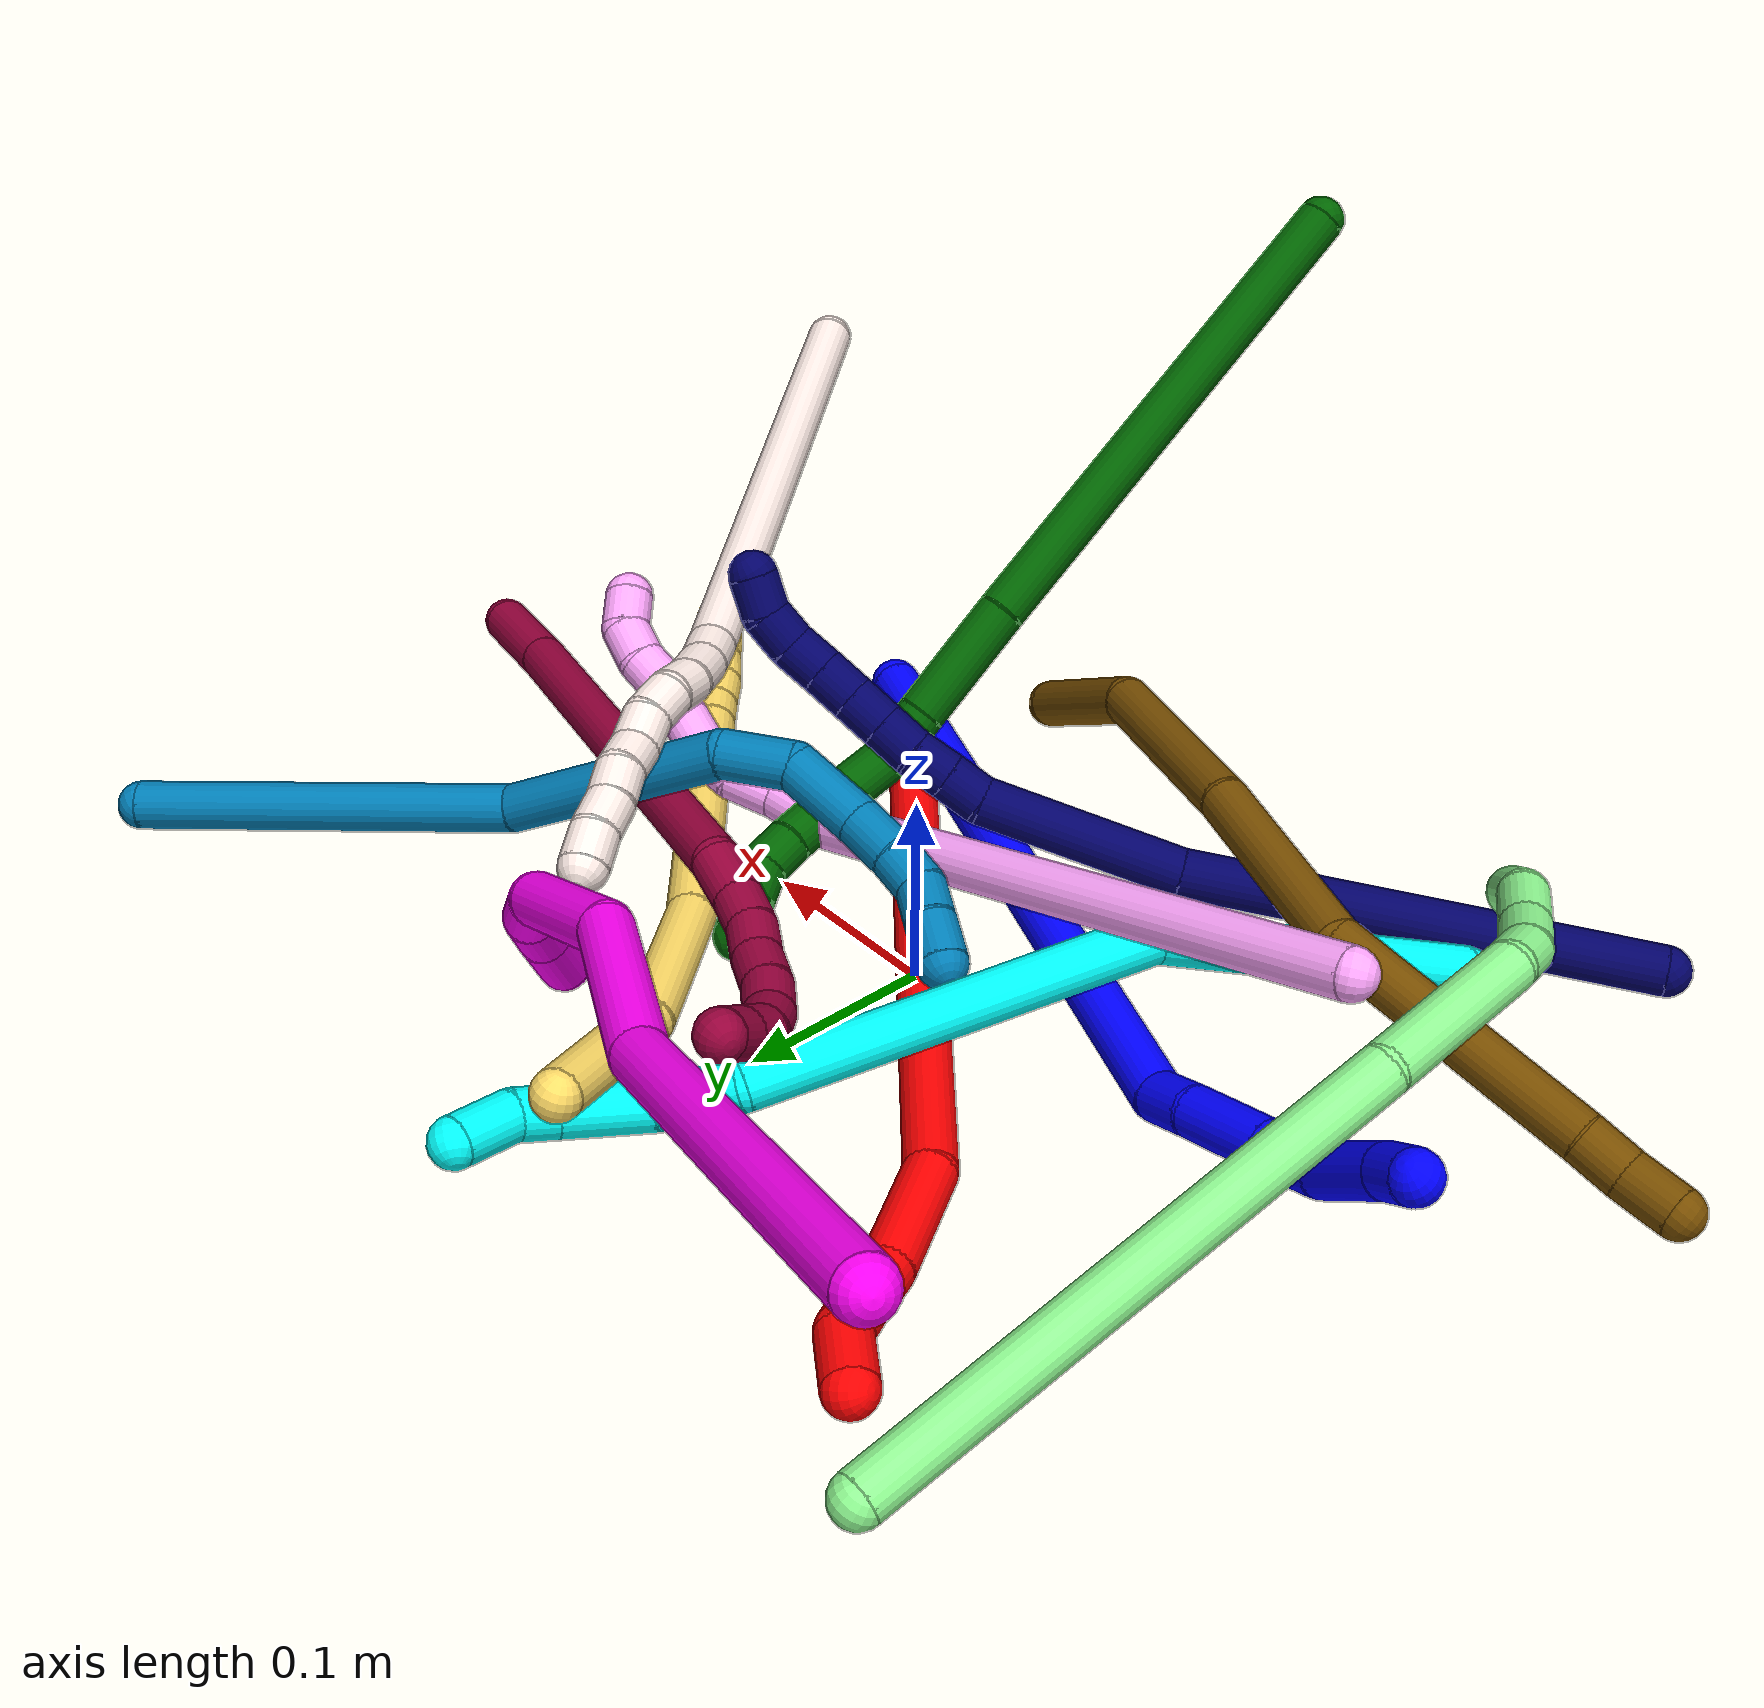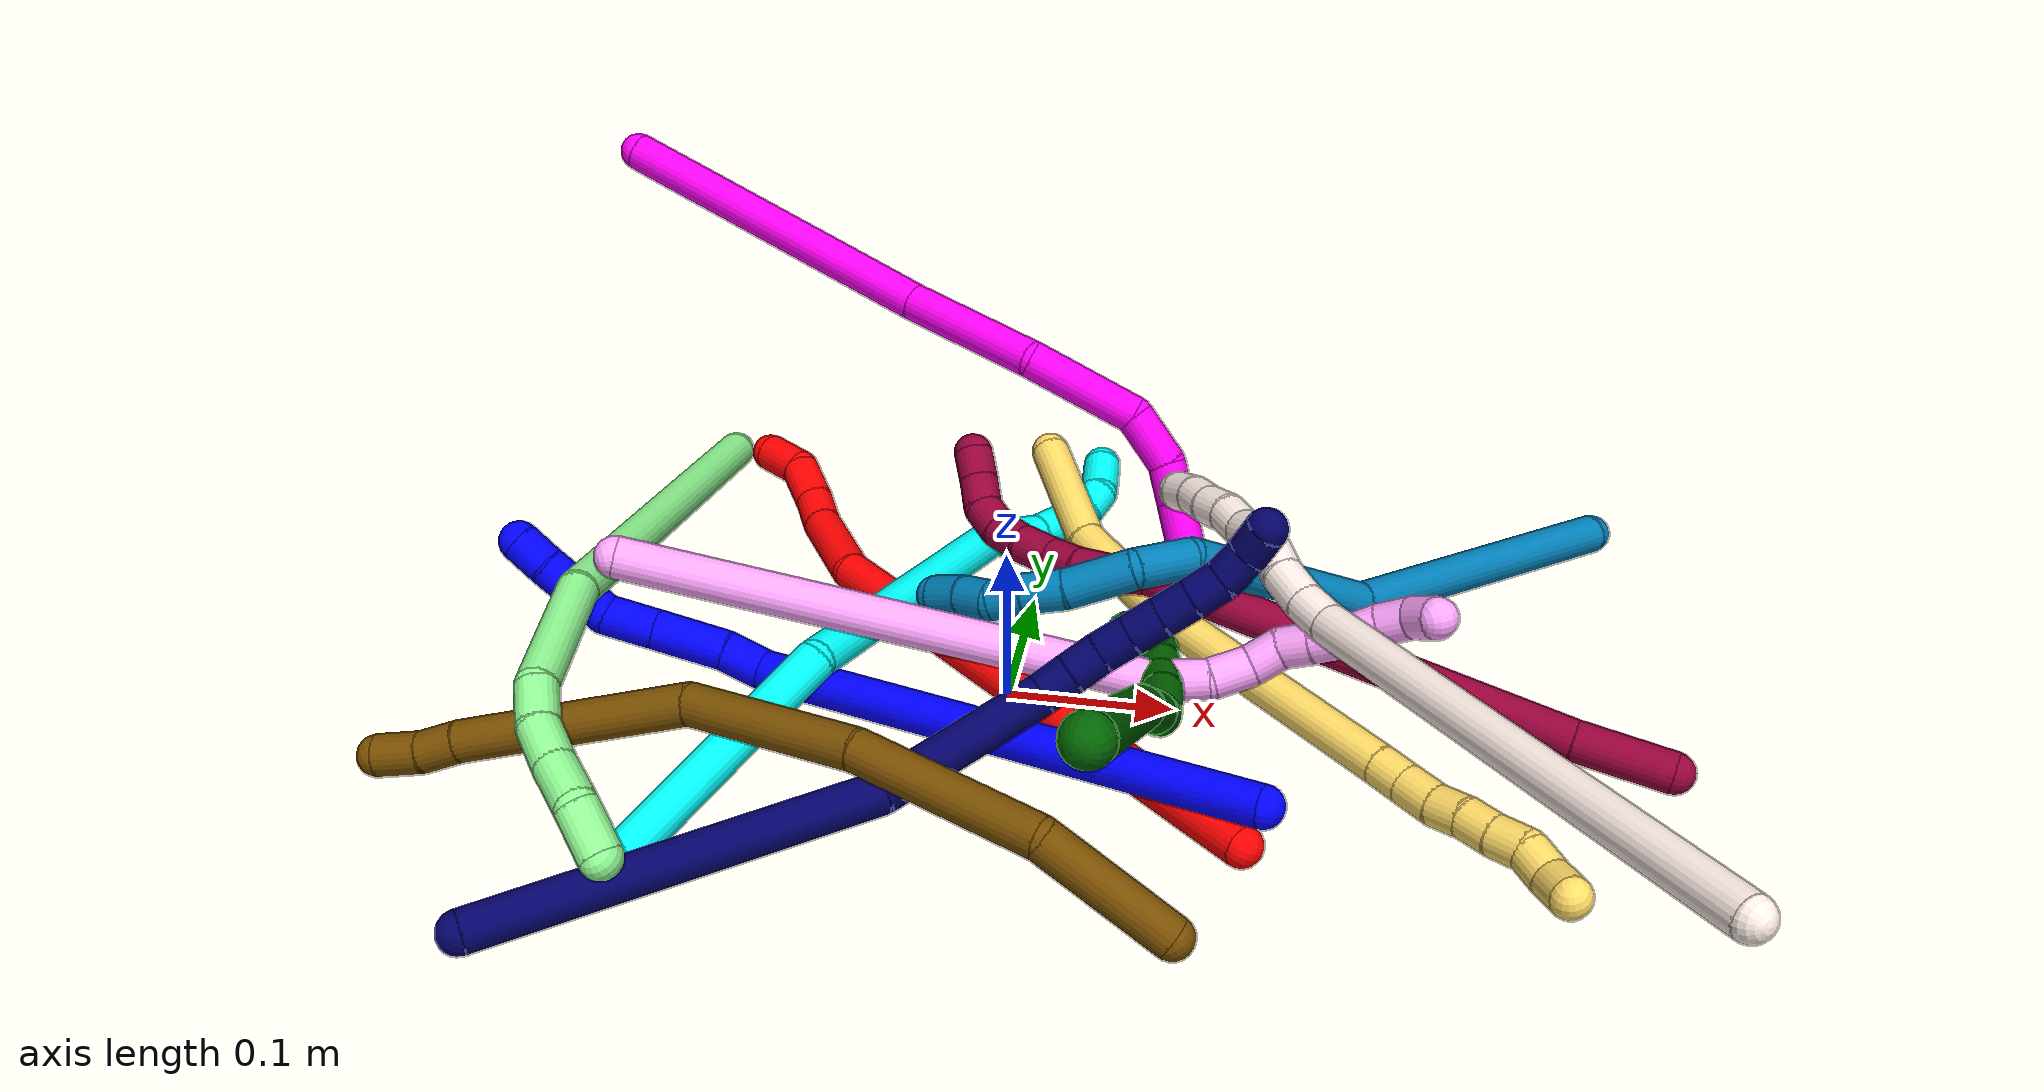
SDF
<sdf version="1.7">
 <world name="default">
  <plugin name="TubeGeneratorPlugin" filename="libtube_generator_plugin.so"/>
  <model name="photoneo_s_sensor">
   <static>1</static>
   <pose>0 0 2 1.57079 1.57079 3.14159</pose>
   <link name="link">
    <inertial><mass>0.1</mass></inertial>
    <sensor name="sensor" type="depth">
     <update_rate>30</update_rate>
     <camera>
      <horizontal_fov>1.22</horizontal_fov>
      <image><width>1920</width><height>1200</height><format>B8G8R8</format></image>
      <clip><near>0.1</near><far>4</far></clip>
      <depth_camera><output>points</output></depth_camera>
     </camera>
     <plugin name="camera_plugin" filename="libgazebo_ros_depth_camera.so">
      <baseline>0.2</baseline>
      <alwaysOn>1</alwaysOn>
      <updateRate>0.0</updateRate>
      <cameraName>camera_ir</cameraName>
      <imageTopicName>/camera/color/image_raw</imageTopicName>
      <cameraInfoTopicName>/camera/color/camera_info</cameraInfoTopicName>
      <depthImageTopicName>/camera/depth/image_raw</depthImageTopicName>
      <depthImageCameraInfoTopicName>/camera/depth/camera_info</depthImageCameraInfoTopicName>
      <pointCloudTopicName>/camera/depth/points</pointCloudTopicName>
      <frameName>fr_optical</frameName>
      <pointCloudCutoff>0.1</pointCloudCutoff>
      <pointCloudCutoffMax>2.0</pointCloudCutoffMax>
      <distortionK1>0</distortionK1>
      <distortionK2>0</distortionK2>
      <distortionK3>0</distortionK3>
      <distortionT1>0</distortionT1>
      <distortionT2>0</distortionT2>
      <CxPrime>0</CxPrime>
      <Cx>0</Cx>
      <Cy>0</Cy>
      <focalLength>0</focalLength>
      <hackBaseline>0</hackBaseline>
     </plugin>
    </sensor>
   </link>
  </model>
  <gravity>0 0 -9.8</gravity>
  <magnetic_field>6e-06 2.3e-05 -4.2e-05</magnetic_field>
  <atmosphere type="adiabatic"/>
  <physics name="default_physics" default="0" type="ode">
   <max_step_size>0.003</max_step_size>
   <real_time_factor>1</real_time_factor>
   <real_time_update_rate>1000</real_time_update_rate>
   <max_contacts>10000</max_contacts>
   <ode>
    <solver>
     <type>quick</type>
     <iters>100</iters>
     <sor>1.3</sor>
     <use_dynamic_moi_rescaling>0</use_dynamic_moi_rescaling>
    </solver>
    <constraints>
     <contact_max_correcting_vel>0</contact_max_correcting_vel>
     <contact_surface_layer>0.001</contact_surface_layer>
     <cfm>0</cfm>
     <erp>0.2</erp>
    </constraints>
   </ode>
  </physics>
  <scene><ambient>0.4 0.4 0.4 1</ambient><background>0.7 0.7 0.7 1</background><shadows>0</shadows></scene>
  <audio><device>default</device></audio>
  <spherical_coordinates>
   <surface_model>EARTH_WGS84</surface_model>
   <latitude_deg>0</latitude_deg>
   <longitude_deg>0</longitude_deg>
   <elevation>0</elevation>
   <heading_deg>0</heading_deg>
  </spherical_coordinates>
  <model name="bin">
   <static>1</static>
   <link name="bottom">
    <collision name="collision-bottom">
     <pose>0 0 -0.01 0 -0 0</pose>
     <geometry><box><size>0.8 0.6 0.02</size></box></geometry>
     <surface>
      <friction><ode><mu>100</mu><mu2>100</mu2></ode></friction>
      <contact><collide_bitmask>65535</collide_bitmask></contact>
     </surface>
    </collision>
   </link>
   <link name="west_wall">
    <collision name="collision-west_wall">
     <pose>-0.41 0 0.1 0 -0 0</pose>
     <geometry><box><size>0.02 0.6 0.2</size></box></geometry>
     <surface>
      <friction><ode><mu>100</mu><mu2>100</mu2></ode></friction>
      <contact><collide_bitmask>65535</collide_bitmask></contact>
     </surface>
    </collision>
   </link>
   <link name="east_wall">
    <collision name="collision-east_wall">
     <pose>0.41 0 0.1 0 -0 0</pose>
     <geometry><box><size>0.02 0.6 0.2</size></box></geometry>
     <surface>
      <friction><ode><mu>100</mu><mu2>100</mu2></ode></friction>
      <contact><collide_bitmask>65535</collide_bitmask></contact>
     </surface>
    </collision>
   </link>
   <link name="south_wall">
    <collision name="collision-south_wall">
     <pose>0 -0.31 0.1 0 -0 0</pose>
     <geometry><box><size>0.8 0.02 0.2</size></box></geometry>
     <surface>
      <friction><ode><mu>100</mu><mu2>100</mu2></ode></friction>
      <contact><collide_bitmask>65535</collide_bitmask></contact>
     </surface>
    </collision>
   </link>
   <link name="north_wall">
    <collision name="collision-north_wall">
     <pose>0 0.31 0.1 0 -0 0</pose>
     <geometry><box><size>0.8 0.02 0.2</size></box></geometry>
     <surface>
      <friction><ode><mu>100</mu><mu2>100</mu2></ode></friction>
      <contact><collide_bitmask>65535</collide_bitmask></contact>
     </surface>
    </collision>
   </link>
  </model>
  <model name="1">
   <static>0</static>
   <link name="1">
    <collision name="collision-cylinder-e_1_1_4">
     <pose>-0.116605 0.11567 -0.006835 -1.62982 -0.788554 0.831316</pose>
     <geometry><cylinder><radius>0.0125</radius><length>0.328773</length></cylinder></geometry>
     <surface>
      <friction><ode><mu>1.16</mu><mu2>1.16</mu2><slip1>0</slip1><slip2>0</slip2></ode></friction>
      <contact><ode><kp>1e+06</kp><kd>1</kd><max_vel>0</max_vel><min_depth>0.001</min_depth></ode></contact>
     </surface>
    </collision>
    <visual name="visual-cylinder-e_1_1_4">
     <pose>-0.116605 0.11567 -0.006835 -1.62982 -0.788554 0.831316</pose>
     <geometry><cylinder><radius>0.0125</radius><length>0.328773</length></cylinder></geometry>
     <material><ambient>0 0 1 1</ambient></material>
    </visual>
    <collision name="collision-cylinder-e_2_4_5">
     <pose>-0.237903 0.243126 -0.017513 -1.88598 -0.361883 0.493853</pose>
     <geometry><cylinder><radius>0.0125</radius><length>0.026513</length></cylinder></geometry>
     <surface>
      <friction><ode><mu>1.16</mu><mu2>1.16</mu2><slip1>0</slip1><slip2>0</slip2></ode></friction>
      <contact><ode><kp>1e+06</kp><kd>1</kd><max_vel>0</max_vel><min_depth>0.001</min_depth></ode></contact>
     </surface>
    </collision>
    <visual name="visual-cylinder-e_2_4_5">
     <pose>-0.237903 0.243126 -0.017513 -1.88598 -0.361883 0.493853</pose>
     <geometry><cylinder><radius>0.0125</radius><length>0.026513</length></cylinder></geometry>
     <material><ambient>0 0 1 1</ambient></material>
    </visual>
    <collision name="collision-cylinder-e_3_5_6">
     <pose>-0.250327 0.275685 -0.02414 -1.70403 -0.35338 0.40263</pose>
     <geometry><cylinder><radius>0.0125</radius><length>0.044674</length></cylinder></geometry>
     <surface>
      <friction><ode><mu>1.16</mu><mu2>1.16</mu2><slip1>0</slip1><slip2>0</slip2></ode></friction>
      <contact><ode><kp>1e+06</kp><kd>1</kd><max_vel>0</max_vel><min_depth>0.001</min_depth></ode></contact>
     </surface>
    </collision>
    <visual name="visual-cylinder-e_3_5_6">
     <pose>-0.250327 0.275685 -0.02414 -1.70403 -0.35338 0.40263</pose>
     <geometry><cylinder><radius>0.0125</radius><length>0.044674</length></cylinder></geometry>
     <material><ambient>0 0 1 1</ambient></material>
    </visual>
    <collision name="collision-cylinder-e_4_6_7">
     <pose>-0.263223 0.311221 -0.028839 -1.69976 -0.334001 0.37908</pose>
     <geometry><cylinder><radius>0.0125</radius><length>0.031519</length></cylinder></geometry>
     <surface>
      <friction><ode><mu>1.16</mu><mu2>1.16</mu2><slip1>0</slip1><slip2>0</slip2></ode></friction>
      <contact><ode><kp>1e+06</kp><kd>1</kd><max_vel>0</max_vel><min_depth>0.001</min_depth></ode></contact>
     </surface>
    </collision>
    <visual name="visual-cylinder-e_4_6_7">
     <pose>-0.263223 0.311221 -0.028839 -1.69976 -0.334001 0.37908</pose>
     <geometry><cylinder><radius>0.0125</radius><length>0.031519</length></cylinder></geometry>
     <material><ambient>0 0 1 1</ambient></material>
    </visual>
    <collision name="collision-cylinder-e_5_7_8">
     <pose>-0.272053 0.345593 -0.042657 -2.11641 -0.158368 0.280154</pose>
     <geometry><cylinder><radius>0.0125</radius><length>0.046455</length></cylinder></geometry>
     <surface>
      <friction><ode><mu>1.16</mu><mu2>1.16</mu2><slip1>0</slip1><slip2>0</slip2></ode></friction>
      <contact><ode><kp>1e+06</kp><kd>1</kd><max_vel>0</max_vel><min_depth>0.001</min_depth></ode></contact>
     </surface>
    </collision>
    <visual name="visual-cylinder-e_5_7_8">
     <pose>-0.272053 0.345593 -0.042657 -2.11641 -0.158368 0.280154</pose>
     <geometry><cylinder><radius>0.0125</radius><length>0.046455</length></cylinder></geometry>
     <material><ambient>0 0 1 1</ambient></material>
    </visual>
    <collision name="collision-cylinder-e_6_8_2">
     <pose>-0.278929 0.373953 -0.060456 -2.16356 -0.295454 0.545374</pose>
     <geometry><cylinder><radius>0.0125</radius><length>0.022065</length></cylinder></geometry>
     <surface>
      <friction><ode><mu>1.16</mu><mu2>1.16</mu2><slip1>0</slip1><slip2>0</slip2></ode></friction>
      <contact><ode><kp>1e+06</kp><kd>1</kd><max_vel>0</max_vel><min_depth>0.001</min_depth></ode></contact>
     </surface>
    </collision>
    <visual name="visual-cylinder-e_6_8_2">
     <pose>-0.278929 0.373953 -0.060456 -2.16356 -0.295454 0.545374</pose>
     <geometry><cylinder><radius>0.0125</radius><length>0.022065</length></cylinder></geometry>
     <material><ambient>0 0 1 1</ambient></material>
    </visual>
    <collision name="collision-sphere-2">
     <pose>-0.282141 0.382708 -0.066353 0 -0 0</pose>
     <geometry><sphere><radius>0.0125</radius></sphere></geometry>
     <surface>
      <friction><ode><mu>1.16</mu><mu2>1.16</mu2><slip1>0</slip1><slip2>0</slip2></ode></friction>
      <contact><ode><kp>1e+06</kp><kd>1</kd><max_vel>0</max_vel><min_depth>0.001</min_depth></ode></contact>
     </surface>
    </collision>
    <visual name="visual-sphere-2">
     <pose>-0.282141 0.382708 -0.066353 0 -0 0</pose>
     <geometry><sphere><radius>0.0125</radius></sphere></geometry>
     <material><ambient>0 0 1 1</ambient></material>
    </visual>
    <collision name="collision-sphere-4">
     <pose>-0.23321 0.231339 -0.01367 0 -0 0</pose>
     <geometry><sphere><radius>0.0125</radius></sphere></geometry>
     <surface>
      <friction><ode><mu>1.16</mu><mu2>1.16</mu2><slip1>0</slip1><slip2>0</slip2></ode></friction>
      <contact><ode><kp>1e+06</kp><kd>1</kd><max_vel>0</max_vel><min_depth>0.001</min_depth></ode></contact>
     </surface>
    </collision>
    <visual name="visual-sphere-4">
     <pose>-0.23321 0.231339 -0.01367 0 -0 0</pose>
     <geometry><sphere><radius>0.0125</radius></sphere></geometry>
     <material><ambient>0 0 1 1</ambient></material>
    </visual>
    <collision name="collision-sphere-1">
     <geometry><sphere><radius>0.0125</radius></sphere></geometry>
     <surface>
      <friction><ode><mu>1.16</mu><mu2>1.16</mu2><slip1>0</slip1><slip2>0</slip2></ode></friction>
      <contact><ode><kp>1e+06</kp><kd>1</kd><max_vel>0</max_vel><min_depth>0.001</min_depth></ode></contact>
     </surface>
    </collision>
    <visual name="visual-sphere-1">
     <geometry><sphere><radius>0.0125</radius></sphere></geometry>
     <material><ambient>0 0 1 1</ambient></material>
    </visual>
    <collision name="collision-sphere-8">
     <pose>-0.275716 0.365199 -0.05456 0 -0 0</pose>
     <geometry><sphere><radius>0.0125</radius></sphere></geometry>
     <surface>
      <friction><ode><mu>1.16</mu><mu2>1.16</mu2><slip1>0</slip1><slip2>0</slip2></ode></friction>
      <contact><ode><kp>1e+06</kp><kd>1</kd><max_vel>0</max_vel><min_depth>0.001</min_depth></ode></contact>
     </surface>
    </collision>
    <visual name="visual-sphere-8">
     <pose>-0.275716 0.365199 -0.05456 0 -0 0</pose>
     <geometry><sphere><radius>0.0125</radius></sphere></geometry>
     <material><ambient>0 0 1 1</ambient></material>
    </visual>
    <collision name="collision-sphere-5">
     <pose>-0.242596 0.254913 -0.021357 0 -0 0</pose>
     <geometry><sphere><radius>0.0125</radius></sphere></geometry>
     <surface>
      <friction><ode><mu>1.16</mu><mu2>1.16</mu2><slip1>0</slip1><slip2>0</slip2></ode></friction>
      <contact><ode><kp>1e+06</kp><kd>1</kd><max_vel>0</max_vel><min_depth>0.001</min_depth></ode></contact>
     </surface>
    </collision>
    <visual name="visual-sphere-5">
     <pose>-0.242596 0.254913 -0.021357 0 -0 0</pose>
     <geometry><sphere><radius>0.0125</radius></sphere></geometry>
     <material><ambient>0 0 1 1</ambient></material>
    </visual>
    <collision name="collision-sphere-6">
     <pose>-0.258057 0.296456 -0.026924 0 -0 0</pose>
     <geometry><sphere><radius>0.0125</radius></sphere></geometry>
     <surface>
      <friction><ode><mu>1.16</mu><mu2>1.16</mu2><slip1>0</slip1><slip2>0</slip2></ode></friction>
      <contact><ode><kp>1e+06</kp><kd>1</kd><max_vel>0</max_vel><min_depth>0.001</min_depth></ode></contact>
     </surface>
    </collision>
    <visual name="visual-sphere-6">
     <pose>-0.258057 0.296456 -0.026924 0 -0 0</pose>
     <geometry><sphere><radius>0.0125</radius></sphere></geometry>
     <material><ambient>0 0 1 1</ambient></material>
    </visual>
    <collision name="collision-sphere-7">
     <pose>-0.26839 0.325986 -0.030754 0 -0 0</pose>
     <geometry><sphere><radius>0.0125</radius></sphere></geometry>
     <surface>
      <friction><ode><mu>1.16</mu><mu2>1.16</mu2><slip1>0</slip1><slip2>0</slip2></ode></friction>
      <contact><ode><kp>1e+06</kp><kd>1</kd><max_vel>0</max_vel><min_depth>0.001</min_depth></ode></contact>
     </surface>
    </collision>
    <visual name="visual-sphere-7">
     <pose>-0.26839 0.325986 -0.030754 0 -0 0</pose>
     <geometry><sphere><radius>0.0125</radius></sphere></geometry>
     <material><ambient>0 0 1 1</ambient></material>
    </visual>
    <inertial>
     <pose>-0.165834 0.181813 -0.016029 0 -0 0</pose>
     <mass>0.5</mass>
     <inertia><ixx>0.002974</ixx><ixy>0</ixy><ixz>0</ixz><iyy>0.003021</iyy><iyz>0</iyz><izz>-5e-06</izz></inertia>
    </inertial>
   </link>
   <pose>0.160929 -0.127151 0.038296 2.80182 -0.475556 -1.05682</pose>
  </model>
  <model name="2">
   <static>0</static>
   <link name="2">
    <collision name="collision-cylinder-e_1_1_4">
     <pose>-0.114372 0.101103 0.087935 -0.854943 -0.706559 0.33287</pose>
     <geometry><cylinder><radius>0.0125</radius><length>0.352337</length></cylinder></geometry>
     <surface>
      <friction><ode><mu>1.16</mu><mu2>1.16</mu2><slip1>0</slip1><slip2>0</slip2></ode></friction>
      <contact><ode><kp>1e+06</kp><kd>1</kd><max_vel>0</max_vel><min_depth>0.001</min_depth></ode></contact>
     </surface>
    </collision>
    <visual name="visual-cylinder-e_1_1_4">
     <pose>-0.114372 0.101103 0.087935 -0.854943 -0.706559 0.33287</pose>
     <geometry><cylinder><radius>0.0125</radius><length>0.352337</length></cylinder></geometry>
     <material><ambient>1 0 0 1</ambient></material>
    </visual>
    <collision name="collision-cylinder-e_2_4_5">
     <pose>-0.24839 0.225212 0.18261 -1.2858 -0.6865 0.523157</pose>
     <geometry><cylinder><radius>0.0125</radius><length>0.061989</length></cylinder></geometry>
     <surface>
      <friction><ode><mu>1.16</mu><mu2>1.16</mu2><slip1>0</slip1><slip2>0</slip2></ode></friction>
      <contact><ode><kp>1e+06</kp><kd>1</kd><max_vel>0</max_vel><min_depth>0.001</min_depth></ode></contact>
     </surface>
    </collision>
    <visual name="visual-cylinder-e_2_4_5">
     <pose>-0.24839 0.225212 0.18261 -1.2858 -0.6865 0.523157</pose>
     <geometry><cylinder><radius>0.0125</radius><length>0.061989</length></cylinder></geometry>
     <material><ambient>1 0 0 1</ambient></material>
    </visual>
    <collision name="collision-cylinder-e_3_5_6">
     <pose>-0.274199 0.259123 0.191899 -1.34125 -0.50312 0.402236</pose>
     <geometry><cylinder><radius>0.0125</radius><length>0.025566</length></cylinder></geometry>
     <surface>
      <friction><ode><mu>1.16</mu><mu2>1.16</mu2><slip1>0</slip1><slip2>0</slip2></ode></friction>
      <contact><ode><kp>1e+06</kp><kd>1</kd><max_vel>0</max_vel><min_depth>0.001</min_depth></ode></contact>
     </surface>
    </collision>
    <visual name="visual-cylinder-e_3_5_6">
     <pose>-0.274199 0.259123 0.191899 -1.34125 -0.50312 0.402236</pose>
     <geometry><cylinder><radius>0.0125</radius><length>0.025566</length></cylinder></geometry>
     <material><ambient>1 0 0 1</ambient></material>
    </visual>
    <collision name="collision-cylinder-e_4_6_7">
     <pose>-0.28513 0.282797 0.200347 -1.13798 -0.326823 0.210121</pose>
     <geometry><cylinder><radius>0.0125</radius><length>0.029703</length></cylinder></geometry>
     <surface>
      <friction><ode><mu>1.16</mu><mu2>1.16</mu2><slip1>0</slip1><slip2>0</slip2></ode></friction>
      <contact><ode><kp>1e+06</kp><kd>1</kd><max_vel>0</max_vel><min_depth>0.001</min_depth></ode></contact>
     </surface>
    </collision>
    <visual name="visual-cylinder-e_4_6_7">
     <pose>-0.28513 0.282797 0.200347 -1.13798 -0.326823 0.210121</pose>
     <geometry><cylinder><radius>0.0125</radius><length>0.029703</length></cylinder></geometry>
     <material><ambient>1 0 0 1</ambient></material>
    </visual>
    <collision name="collision-cylinder-e_5_7_2">
     <pose>-0.299762 0.303357 0.214796 -0.739018 -0.706107 0.283518</pose>
     <geometry><cylinder><radius>0.0125</radius><length>0.030405</length></cylinder></geometry>
     <surface>
      <friction><ode><mu>1.16</mu><mu2>1.16</mu2><slip1>0</slip1><slip2>0</slip2></ode></friction>
      <contact><ode><kp>1e+06</kp><kd>1</kd><max_vel>0</max_vel><min_depth>0.001</min_depth></ode></contact>
     </surface>
    </collision>
    <visual name="visual-cylinder-e_5_7_2">
     <pose>-0.299762 0.303357 0.214796 -0.739018 -0.706107 0.283518</pose>
     <geometry><cylinder><radius>0.0125</radius><length>0.030405</length></cylinder></geometry>
     <material><ambient>1 0 0 1</ambient></material>
    </visual>
    <collision name="collision-sphere-2">
     <pose>-0.309627 0.311148 0.223346 0 -0 0</pose>
     <geometry><sphere><radius>0.0125</radius></sphere></geometry>
     <surface>
      <friction><ode><mu>1.16</mu><mu2>1.16</mu2><slip1>0</slip1><slip2>0</slip2></ode></friction>
      <contact><ode><kp>1e+06</kp><kd>1</kd><max_vel>0</max_vel><min_depth>0.001</min_depth></ode></contact>
     </surface>
    </collision>
    <visual name="visual-sphere-2">
     <pose>-0.309627 0.311148 0.223346 0 -0 0</pose>
     <geometry><sphere><radius>0.0125</radius></sphere></geometry>
     <material><ambient>1 0 0 1</ambient></material>
    </visual>
    <collision name="collision-sphere-7">
     <pose>-0.289898 0.295566 0.206246 0 -0 0</pose>
     <geometry><sphere><radius>0.0125</radius></sphere></geometry>
     <surface>
      <friction><ode><mu>1.16</mu><mu2>1.16</mu2><slip1>0</slip1><slip2>0</slip2></ode></friction>
      <contact><ode><kp>1e+06</kp><kd>1</kd><max_vel>0</max_vel><min_depth>0.001</min_depth></ode></contact>
     </surface>
    </collision>
    <visual name="visual-sphere-7">
     <pose>-0.289898 0.295566 0.206246 0 -0 0</pose>
     <geometry><sphere><radius>0.0125</radius></sphere></geometry>
     <material><ambient>1 0 0 1</ambient></material>
    </visual>
    <collision name="collision-sphere-6">
     <pose>-0.280362 0.270029 0.194447 0 -0 0</pose>
     <geometry><sphere><radius>0.0125</radius></sphere></geometry>
     <surface>
      <friction><ode><mu>1.16</mu><mu2>1.16</mu2><slip1>0</slip1><slip2>0</slip2></ode></friction>
      <contact><ode><kp>1e+06</kp><kd>1</kd><max_vel>0</max_vel><min_depth>0.001</min_depth></ode></contact>
     </surface>
    </collision>
    <visual name="visual-sphere-6">
     <pose>-0.280362 0.270029 0.194447 0 -0 0</pose>
     <geometry><sphere><radius>0.0125</radius></sphere></geometry>
     <material><ambient>1 0 0 1</ambient></material>
    </visual>
    <collision name="collision-sphere-5">
     <pose>-0.268035 0.248218 0.189351 0 -0 0</pose>
     <geometry><sphere><radius>0.0125</radius></sphere></geometry>
     <surface>
      <friction><ode><mu>1.16</mu><mu2>1.16</mu2><slip1>0</slip1><slip2>0</slip2></ode></friction>
      <contact><ode><kp>1e+06</kp><kd>1</kd><max_vel>0</max_vel><min_depth>0.001</min_depth></ode></contact>
     </surface>
    </collision>
    <visual name="visual-sphere-5">
     <pose>-0.268035 0.248218 0.189351 0 -0 0</pose>
     <geometry><sphere><radius>0.0125</radius></sphere></geometry>
     <material><ambient>1 0 0 1</ambient></material>
    </visual>
    <collision name="collision-sphere-1">
     <geometry><sphere><radius>0.0125</radius></sphere></geometry>
     <surface>
      <friction><ode><mu>1.16</mu><mu2>1.16</mu2><slip1>0</slip1><slip2>0</slip2></ode></friction>
      <contact><ode><kp>1e+06</kp><kd>1</kd><max_vel>0</max_vel><min_depth>0.001</min_depth></ode></contact>
     </surface>
    </collision>
    <visual name="visual-sphere-1">
     <geometry><sphere><radius>0.0125</radius></sphere></geometry>
     <material><ambient>1 0 0 1</ambient></material>
    </visual>
    <collision name="collision-sphere-4">
     <pose>-0.228745 0.202206 0.17587 0 -0 0</pose>
     <geometry><sphere><radius>0.0125</radius></sphere></geometry>
     <surface>
      <friction><ode><mu>1.16</mu><mu2>1.16</mu2><slip1>0</slip1><slip2>0</slip2></ode></friction>
      <contact><ode><kp>1e+06</kp><kd>1</kd><max_vel>0</max_vel><min_depth>0.001</min_depth></ode></contact>
     </surface>
    </collision>
    <visual name="visual-sphere-4">
     <pose>-0.228745 0.202206 0.17587 0 -0 0</pose>
     <geometry><sphere><radius>0.0125</radius></sphere></geometry>
     <material><ambient>1 0 0 1</ambient></material>
    </visual>
    <inertial>
     <pose>-0.160577 0.147662 0.119381 0 -0 0</pose>
     <mass>0.5</mass>
     <inertia>
      <ixx>0.003549</ixx>
      <ixy>0</ixy>
      <ixz>0</ixz>
      <iyy>0.003817</iyy>
      <iyz>0</iyz>
      <izz>0.000288</izz>
     </inertia>
    </inertial>
   </link>
   <pose>0.150884 -0.129428 0.01144 0.880791 -0.858559 -0.714353</pose>
  </model>
  <model name="3">
   <static>0</static>
   <link name="3">
    <collision name="collision-cylinder-e_1_1_4">
     <pose>0.001823 0.079707 0.011138 -1.43196 0.02265 -0.019706</pose>
     <geometry><cylinder><radius>0.0125</radius><length>0.161005</length></cylinder></geometry>
     <surface>
      <friction><ode><mu>1.16</mu><mu2>1.16</mu2><slip1>0</slip1><slip2>0</slip2></ode></friction>
      <contact><ode><kp>1e+06</kp><kd>1</kd><max_vel>0</max_vel><min_depth>0.001</min_depth></ode></contact>
     </surface>
    </collision>
    <visual name="visual-cylinder-e_1_1_4">
     <pose>0.001823 0.079707 0.011138 -1.43196 0.02265 -0.019706</pose>
     <geometry><cylinder><radius>0.0125</radius><length>0.161005</length></cylinder></geometry>
     <material><ambient>0.003922 1 0.996078 1</ambient></material>
    </visual>
    <collision name="collision-cylinder-e_2_4_5">
     <pose>0.03531 0.253431 0.002932 -1.77371 0.318637 -0.389219</pose>
     <geometry><cylinder><radius>0.0125</radius><length>0.202146</length></cylinder></geometry>
     <surface>
      <friction><ode><mu>1.16</mu><mu2>1.16</mu2><slip1>0</slip1><slip2>0</slip2></ode></friction>
      <contact><ode><kp>1e+06</kp><kd>1</kd><max_vel>0</max_vel><min_depth>0.001</min_depth></ode></contact>
     </surface>
    </collision>
    <visual name="visual-cylinder-e_2_4_5">
     <pose>0.03531 0.253431 0.002932 -1.77371 0.318637 -0.389219</pose>
     <geometry><cylinder><radius>0.0125</radius><length>0.202146</length></cylinder></geometry>
     <material><ambient>0.003922 1 0.996078 1</ambient></material>
    </visual>
    <collision name="collision-cylinder-e_3_5_6">
     <pose>0.0789 0.363588 -0.014889 -1.47681 0.634256 -0.580568</pose>
     <geometry><cylinder><radius>0.0125</radius><length>0.040253</length></cylinder></geometry>
     <surface>
      <friction><ode><mu>1.16</mu><mu2>1.16</mu2><slip1>0</slip1><slip2>0</slip2></ode></friction>
      <contact><ode><kp>1e+06</kp><kd>1</kd><max_vel>0</max_vel><min_depth>0.001</min_depth></ode></contact>
     </surface>
    </collision>
    <visual name="visual-cylinder-e_3_5_6">
     <pose>0.0789 0.363588 -0.014889 -1.47681 0.634256 -0.580568</pose>
     <geometry><cylinder><radius>0.0125</radius><length>0.040253</length></cylinder></geometry>
     <material><ambient>0.003922 1 0.996078 1</ambient></material>
    </visual>
    <collision name="collision-cylinder-e_4_6_7">
     <pose>0.098554 0.400028 -0.010831 -1.44645 0.361189 -0.319618</pose>
     <geometry><cylinder><radius>0.0125</radius><length>0.043738</length></cylinder></geometry>
     <surface>
      <friction><ode><mu>1.16</mu><mu2>1.16</mu2><slip1>0</slip1><slip2>0</slip2></ode></friction>
      <contact><ode><kp>1e+06</kp><kd>1</kd><max_vel>0</max_vel><min_depth>0.001</min_depth></ode></contact>
     </surface>
    </collision>
    <visual name="visual-cylinder-e_4_6_7">
     <pose>0.098554 0.400028 -0.010831 -1.44645 0.361189 -0.319618</pose>
     <geometry><cylinder><radius>0.0125</radius><length>0.043738</length></cylinder></geometry>
     <material><ambient>0.003922 1 0.996078 1</ambient></material>
    </visual>
    <collision name="collision-cylinder-e_5_7_8">
     <pose>0.106585 0.430933 -0.008538 -1.59388 0.02849 -0.029155</pose>
     <geometry><cylinder><radius>0.0125</radius><length>0.021225</length></cylinder></geometry>
     <surface>
      <friction><ode><mu>1.16</mu><mu2>1.16</mu2><slip1>0</slip1><slip2>0</slip2></ode></friction>
      <contact><ode><kp>1e+06</kp><kd>1</kd><max_vel>0</max_vel><min_depth>0.001</min_depth></ode></contact>
     </surface>
    </collision>
    <visual name="visual-cylinder-e_5_7_8">
     <pose>0.106585 0.430933 -0.008538 -1.59388 0.02849 -0.029155</pose>
     <geometry><cylinder><radius>0.0125</radius><length>0.021225</length></cylinder></geometry>
     <material><ambient>0.003922 1 0.996078 1</ambient></material>
    </visual>
    <collision name="collision-cylinder-e_6_8_2">
     <pose>0.105081 0.455757 -0.015471 -2.01045 -0.11442 0.179974</pose>
     <geometry><cylinder><radius>0.0125</radius><length>0.031634</length></cylinder></geometry>
     <surface>
      <friction><ode><mu>1.16</mu><mu2>1.16</mu2><slip1>0</slip1><slip2>0</slip2></ode></friction>
      <contact><ode><kp>1e+06</kp><kd>1</kd><max_vel>0</max_vel><min_depth>0.001</min_depth></ode></contact>
     </surface>
    </collision>
    <visual name="visual-cylinder-e_6_8_2">
     <pose>0.105081 0.455757 -0.015471 -2.01045 -0.11442 0.179974</pose>
     <geometry><cylinder><radius>0.0125</radius><length>0.031634</length></cylinder></geometry>
     <material><ambient>0.003922 1 0.996078 1</ambient></material>
    </visual>
    <collision name="collision-sphere-2">
     <pose>0.103275 0.469977 -0.022159 0 -0 0</pose>
     <geometry><sphere><radius>0.0125</radius></sphere></geometry>
     <surface>
      <friction><ode><mu>1.16</mu><mu2>1.16</mu2><slip1>0</slip1><slip2>0</slip2></ode></friction>
      <contact><ode><kp>1e+06</kp><kd>1</kd><max_vel>0</max_vel><min_depth>0.001</min_depth></ode></contact>
     </surface>
    </collision>
    <visual name="visual-sphere-2">
     <pose>0.103275 0.469977 -0.022159 0 -0 0</pose>
     <geometry><sphere><radius>0.0125</radius></sphere></geometry>
     <material><ambient>0.003922 1 0.996078 1</ambient></material>
    </visual>
    <collision name="collision-sphere-4">
     <pose>0.003647 0.159415 0.022275 0 -0 0</pose>
     <geometry><sphere><radius>0.0125</radius></sphere></geometry>
     <surface>
      <friction><ode><mu>1.16</mu><mu2>1.16</mu2><slip1>0</slip1><slip2>0</slip2></ode></friction>
      <contact><ode><kp>1e+06</kp><kd>1</kd><max_vel>0</max_vel><min_depth>0.001</min_depth></ode></contact>
     </surface>
    </collision>
    <visual name="visual-sphere-4">
     <pose>0.003647 0.159415 0.022275 0 -0 0</pose>
     <geometry><sphere><radius>0.0125</radius></sphere></geometry>
     <material><ambient>0.003922 1 0.996078 1</ambient></material>
    </visual>
    <collision name="collision-sphere-1">
     <geometry><sphere><radius>0.0125</radius></sphere></geometry>
     <surface>
      <friction><ode><mu>1.16</mu><mu2>1.16</mu2><slip1>0</slip1><slip2>0</slip2></ode></friction>
      <contact><ode><kp>1e+06</kp><kd>1</kd><max_vel>0</max_vel><min_depth>0.001</min_depth></ode></contact>
     </surface>
    </collision>
    <visual name="visual-sphere-1">
     <geometry><sphere><radius>0.0125</radius></sphere></geometry>
     <material><ambient>0.003922 1 0.996078 1</ambient></material>
    </visual>
    <collision name="collision-sphere-8">
     <pose>0.106887 0.441538 -0.008783 0 -0 0</pose>
     <geometry><sphere><radius>0.0125</radius></sphere></geometry>
     <surface>
      <friction><ode><mu>1.16</mu><mu2>1.16</mu2><slip1>0</slip1><slip2>0</slip2></ode></friction>
      <contact><ode><kp>1e+06</kp><kd>1</kd><max_vel>0</max_vel><min_depth>0.001</min_depth></ode></contact>
     </surface>
    </collision>
    <visual name="visual-sphere-8">
     <pose>0.106887 0.441538 -0.008783 0 -0 0</pose>
     <geometry><sphere><radius>0.0125</radius></sphere></geometry>
     <material><ambient>0.003922 1 0.996078 1</ambient></material>
    </visual>
    <collision name="collision-sphere-5">
     <pose>0.066973 0.347447 -0.016411 0 -0 0</pose>
     <geometry><sphere><radius>0.0125</radius></sphere></geometry>
     <surface>
      <friction><ode><mu>1.16</mu><mu2>1.16</mu2><slip1>0</slip1><slip2>0</slip2></ode></friction>
      <contact><ode><kp>1e+06</kp><kd>1</kd><max_vel>0</max_vel><min_depth>0.001</min_depth></ode></contact>
     </surface>
    </collision>
    <visual name="visual-sphere-5">
     <pose>0.066973 0.347447 -0.016411 0 -0 0</pose>
     <geometry><sphere><radius>0.0125</radius></sphere></geometry>
     <material><ambient>0.003922 1 0.996078 1</ambient></material>
    </visual>
    <collision name="collision-sphere-6">
     <pose>0.090826 0.379728 -0.013368 0 -0 0</pose>
     <geometry><sphere><radius>0.0125</radius></sphere></geometry>
     <surface>
      <friction><ode><mu>1.16</mu><mu2>1.16</mu2><slip1>0</slip1><slip2>0</slip2></ode></friction>
      <contact><ode><kp>1e+06</kp><kd>1</kd><max_vel>0</max_vel><min_depth>0.001</min_depth></ode></contact>
     </surface>
    </collision>
    <visual name="visual-sphere-6">
     <pose>0.090826 0.379728 -0.013368 0 -0 0</pose>
     <geometry><sphere><radius>0.0125</radius></sphere></geometry>
     <material><ambient>0.003922 1 0.996078 1</ambient></material>
    </visual>
    <collision name="collision-sphere-7">
     <pose>0.106283 0.420328 -0.008293 0 -0 0</pose>
     <geometry><sphere><radius>0.0125</radius></sphere></geometry>
     <surface>
      <friction><ode><mu>1.16</mu><mu2>1.16</mu2><slip1>0</slip1><slip2>0</slip2></ode></friction>
      <contact><ode><kp>1e+06</kp><kd>1</kd><max_vel>0</max_vel><min_depth>0.001</min_depth></ode></contact>
     </surface>
    </collision>
    <visual name="visual-sphere-7">
     <pose>0.106283 0.420328 -0.008293 0 -0 0</pose>
     <geometry><sphere><radius>0.0125</radius></sphere></geometry>
     <material><ambient>0.003922 1 0.996078 1</ambient></material>
    </visual>
    <inertial>
     <pose>0.041008 0.239518 0.001284 0 -0 0</pose>
     <mass>0.5</mass>
     <inertia>
      <ixx>0.000729</ixx>
      <ixy>0</ixy>
      <ixz>0</ixz>
      <iyy>-0.000223</iyy>
      <iyz>0</iyz>
      <izz>-0.001252</izz>
     </inertia>
    </inertial>
   </link>
   <pose>-0.17849 -0.191599 0.011336 0.470115 1.0446 0.038012</pose>
  </model>
  <model name="4">
   <static>0</static>
   <link name="4">
    <collision name="collision-cylinder-e_1_1_4">
     <pose>0.07566 0.028278 0.136966 -0.2036 0.495897 -0.05171</pose>
     <geometry><cylinder><radius>0.0125</radius><length>0.318017</length></cylinder></geometry>
     <surface>
      <friction><ode><mu>1.16</mu><mu2>1.16</mu2><slip1>0</slip1><slip2>0</slip2></ode></friction>
      <contact><ode><kp>1e+06</kp><kd>1</kd><max_vel>0</max_vel><min_depth>0.001</min_depth></ode></contact>
     </surface>
    </collision>
    <visual name="visual-cylinder-e_1_1_4">
     <pose>0.07566 0.028278 0.136966 -0.2036 0.495897 -0.05171</pose>
     <geometry><cylinder><radius>0.0125</radius><length>0.318017</length></cylinder></geometry>
     <material><ambient>1 0.65098 0.996078 1</ambient></material>
    </visual>
    <collision name="collision-cylinder-e_2_4_5">
     <pose>0.158236 0.054716 0.289413 0.1183 0.417614 0.025095</pose>
     <geometry><cylinder><radius>0.0125</radius><length>0.034111</length></cylinder></geometry>
     <surface>
      <friction><ode><mu>1.16</mu><mu2>1.16</mu2><slip1>0</slip1><slip2>0</slip2></ode></friction>
      <contact><ode><kp>1e+06</kp><kd>1</kd><max_vel>0</max_vel><min_depth>0.001</min_depth></ode></contact>
     </surface>
    </collision>
    <visual name="visual-cylinder-e_2_4_5">
     <pose>0.158236 0.054716 0.289413 0.1183 0.417614 0.025095</pose>
     <geometry><cylinder><radius>0.0125</radius><length>0.034111</length></cylinder></geometry>
     <material><ambient>1 0.65098 0.996078 1</ambient></material>
    </visual>
    <collision name="collision-cylinder-e_3_5_6">
     <pose>0.166234 0.050766 0.317627 0.164205 0.083484 0.006874</pose>
     <geometry><cylinder><radius>0.0125</radius><length>0.025905</length></cylinder></geometry>
     <surface>
      <friction><ode><mu>1.16</mu><mu2>1.16</mu2><slip1>0</slip1><slip2>0</slip2></ode></friction>
      <contact><ode><kp>1e+06</kp><kd>1</kd><max_vel>0</max_vel><min_depth>0.001</min_depth></ode></contact>
     </surface>
    </collision>
    <visual name="visual-cylinder-e_3_5_6">
     <pose>0.166234 0.050766 0.317627 0.164205 0.083484 0.006874</pose>
     <geometry><cylinder><radius>0.0125</radius><length>0.025905</length></cylinder></geometry>
     <material><ambient>1 0.65098 0.996078 1</ambient></material>
    </visual>
    <collision name="collision-cylinder-e_4_6_7">
     <pose>0.168313 0.043429 0.339307 0.528767 0.096082 0.02603</pose>
     <geometry><cylinder><radius>0.0125</radius><length>0.02082</length></cylinder></geometry>
     <surface>
      <friction><ode><mu>1.16</mu><mu2>1.16</mu2><slip1>0</slip1><slip2>0</slip2></ode></friction>
      <contact><ode><kp>1e+06</kp><kd>1</kd><max_vel>0</max_vel><min_depth>0.001</min_depth></ode></contact>
     </surface>
    </collision>
    <visual name="visual-cylinder-e_4_6_7">
     <pose>0.168313 0.043429 0.339307 0.528767 0.096082 0.02603</pose>
     <geometry><cylinder><radius>0.0125</radius><length>0.02082</length></cylinder></geometry>
     <material><ambient>1 0.65098 0.996078 1</ambient></material>
    </visual>
    <collision name="collision-cylinder-e_5_7_8">
     <pose>0.17466 0.033517 0.355298 0.586943 0.563807 0.174598</pose>
     <geometry><cylinder><radius>0.0125</radius><length>0.020017</length></cylinder></geometry>
     <surface>
      <friction><ode><mu>1.16</mu><mu2>1.16</mu2><slip1>0</slip1><slip2>0</slip2></ode></friction>
      <contact><ode><kp>1e+06</kp><kd>1</kd><max_vel>0</max_vel><min_depth>0.001</min_depth></ode></contact>
     </surface>
    </collision>
    <visual name="visual-cylinder-e_5_7_8">
     <pose>0.17466 0.033517 0.355298 0.586943 0.563807 0.174598</pose>
     <geometry><cylinder><radius>0.0125</radius><length>0.020017</length></cylinder></geometry>
     <material><ambient>1 0.65098 0.996078 1</ambient></material>
    </visual>
    <collision name="collision-cylinder-e_6_8_9">
     <pose>0.184926 0.023934 0.369592 0.59412 0.511995 0.159905</pose>
     <geometry><cylinder><radius>0.0125</radius><length>0.020075</length></cylinder></geometry>
     <surface>
      <friction><ode><mu>1.16</mu><mu2>1.16</mu2><slip1>0</slip1><slip2>0</slip2></ode></friction>
      <contact><ode><kp>1e+06</kp><kd>1</kd><max_vel>0</max_vel><min_depth>0.001</min_depth></ode></contact>
     </surface>
    </collision>
    <visual name="visual-cylinder-e_6_8_9">
     <pose>0.184926 0.023934 0.369592 0.59412 0.511995 0.159905</pose>
     <geometry><cylinder><radius>0.0125</radius><length>0.020075</length></cylinder></geometry>
     <material><ambient>1 0.65098 0.996078 1</ambient></material>
    </visual>
    <collision name="collision-cylinder-e_7_9_10">
     <pose>0.192937 0.014001 0.385527 0.52541 0.298948 0.080953</pose>
     <geometry><cylinder><radius>0.0125</radius><length>0.021008</length></cylinder></geometry>
     <surface>
      <friction><ode><mu>1.16</mu><mu2>1.16</mu2><slip1>0</slip1><slip2>0</slip2></ode></friction>
      <contact><ode><kp>1e+06</kp><kd>1</kd><max_vel>0</max_vel><min_depth>0.001</min_depth></ode></contact>
     </surface>
    </collision>
    <visual name="visual-cylinder-e_7_9_10">
     <pose>0.192937 0.014001 0.385527 0.52541 0.298948 0.080953</pose>
     <geometry><cylinder><radius>0.0125</radius><length>0.021008</length></cylinder></geometry>
     <material><ambient>1 0.65098 0.996078 1</ambient></material>
    </visual>
    <collision name="collision-cylinder-e_8_10_11">
     <pose>0.201074 0.003534 0.400956 0.677976 0.527406 0.189825</pose>
     <geometry><cylinder><radius>0.0125</radius><length>0.020042</length></cylinder></geometry>
     <surface>
      <friction><ode><mu>1.16</mu><mu2>1.16</mu2><slip1>0</slip1><slip2>0</slip2></ode></friction>
      <contact><ode><kp>1e+06</kp><kd>1</kd><max_vel>0</max_vel><min_depth>0.001</min_depth></ode></contact>
     </surface>
    </collision>
    <visual name="visual-cylinder-e_8_10_11">
     <pose>0.201074 0.003534 0.400956 0.677976 0.527406 0.189825</pose>
     <geometry><cylinder><radius>0.0125</radius><length>0.020042</length></cylinder></geometry>
     <material><ambient>1 0.65098 0.996078 1</ambient></material>
    </visual>
    <collision name="collision-cylinder-e_9_11_2">
     <pose>0.213541 -0.008182 0.410036 1.21499 0.83619 0.599149</pose>
     <geometry><cylinder><radius>0.0125</radius><length>0.020006</length></cylinder></geometry>
     <surface>
      <friction><ode><mu>1.16</mu><mu2>1.16</mu2><slip1>0</slip1><slip2>0</slip2></ode></friction>
      <contact><ode><kp>1e+06</kp><kd>1</kd><max_vel>0</max_vel><min_depth>0.001</min_depth></ode></contact>
     </surface>
    </collision>
    <visual name="visual-cylinder-e_9_11_2">
     <pose>0.213541 -0.008182 0.410036 1.21499 0.83619 0.599149</pose>
     <geometry><cylinder><radius>0.0125</radius><length>0.020006</length></cylinder></geometry>
     <material><ambient>1 0.65098 0.996078 1</ambient></material>
    </visual>
    <collision name="collision-sphere-2">
     <pose>0.220964 -0.014467 0.412371 0 -0 0</pose>
     <geometry><sphere><radius>0.0125</radius></sphere></geometry>
     <surface>
      <friction><ode><mu>1.16</mu><mu2>1.16</mu2><slip1>0</slip1><slip2>0</slip2></ode></friction>
      <contact><ode><kp>1e+06</kp><kd>1</kd><max_vel>0</max_vel><min_depth>0.001</min_depth></ode></contact>
     </surface>
    </collision>
    <visual name="visual-sphere-2">
     <pose>0.220964 -0.014467 0.412371 0 -0 0</pose>
     <geometry><sphere><radius>0.0125</radius></sphere></geometry>
     <material><ambient>1 0.65098 0.996078 1</ambient></material>
    </visual>
    <collision name="collision-sphere-11">
     <pose>0.206118 -0.001897 0.4077 0 -0 0</pose>
     <geometry><sphere><radius>0.0125</radius></sphere></geometry>
     <surface>
      <friction><ode><mu>1.16</mu><mu2>1.16</mu2><slip1>0</slip1><slip2>0</slip2></ode></friction>
      <contact><ode><kp>1e+06</kp><kd>1</kd><max_vel>0</max_vel><min_depth>0.001</min_depth></ode></contact>
     </surface>
    </collision>
    <visual name="visual-sphere-11">
     <pose>0.206118 -0.001897 0.4077 0 -0 0</pose>
     <geometry><sphere><radius>0.0125</radius></sphere></geometry>
     <material><ambient>1 0.65098 0.996078 1</ambient></material>
    </visual>
    <collision name="collision-sphere-10">
     <pose>0.196031 0.008966 0.394212 0 -0 0</pose>
     <geometry><sphere><radius>0.0125</radius></sphere></geometry>
     <surface>
      <friction><ode><mu>1.16</mu><mu2>1.16</mu2><slip1>0</slip1><slip2>0</slip2></ode></friction>
      <contact><ode><kp>1e+06</kp><kd>1</kd><max_vel>0</max_vel><min_depth>0.001</min_depth></ode></contact>
     </surface>
    </collision>
    <visual name="visual-sphere-10">
     <pose>0.196031 0.008966 0.394212 0 -0 0</pose>
     <geometry><sphere><radius>0.0125</radius></sphere></geometry>
     <material><ambient>1 0.65098 0.996078 1</ambient></material>
    </visual>
    <collision name="collision-sphere-9">
     <pose>0.189843 0.019035 0.376843 0 -0 0</pose>
     <geometry><sphere><radius>0.0125</radius></sphere></geometry>
     <surface>
      <friction><ode><mu>1.16</mu><mu2>1.16</mu2><slip1>0</slip1><slip2>0</slip2></ode></friction>
      <contact><ode><kp>1e+06</kp><kd>1</kd><max_vel>0</max_vel><min_depth>0.001</min_depth></ode></contact>
     </surface>
    </collision>
    <visual name="visual-sphere-9">
     <pose>0.189843 0.019035 0.376843 0 -0 0</pose>
     <geometry><sphere><radius>0.0125</radius></sphere></geometry>
     <material><ambient>1 0.65098 0.996078 1</ambient></material>
    </visual>
    <collision name="collision-sphere-4">
     <pose>0.151319 0.056556 0.273932 0 -0 0</pose>
     <geometry><sphere><radius>0.0125</radius></sphere></geometry>
     <surface>
      <friction><ode><mu>1.16</mu><mu2>1.16</mu2><slip1>0</slip1><slip2>0</slip2></ode></friction>
      <contact><ode><kp>1e+06</kp><kd>1</kd><max_vel>0</max_vel><min_depth>0.001</min_depth></ode></contact>
     </surface>
    </collision>
    <visual name="visual-sphere-4">
     <pose>0.151319 0.056556 0.273932 0 -0 0</pose>
     <geometry><sphere><radius>0.0125</radius></sphere></geometry>
     <material><ambient>1 0.65098 0.996078 1</ambient></material>
    </visual>
    <collision name="collision-sphere-1">
     <geometry><sphere><radius>0.0125</radius></sphere></geometry>
     <surface>
      <friction><ode><mu>1.16</mu><mu2>1.16</mu2><slip1>0</slip1><slip2>0</slip2></ode></friction>
      <contact><ode><kp>1e+06</kp><kd>1</kd><max_vel>0</max_vel><min_depth>0.001</min_depth></ode></contact>
     </surface>
    </collision>
    <visual name="visual-sphere-1">
     <geometry><sphere><radius>0.0125</radius></sphere></geometry>
     <material><ambient>1 0.65098 0.996078 1</ambient></material>
    </visual>
    <collision name="collision-sphere-8">
     <pose>0.180008 0.028832 0.362341 0 -0 0</pose>
     <geometry><sphere><radius>0.0125</radius></sphere></geometry>
     <surface>
      <friction><ode><mu>1.16</mu><mu2>1.16</mu2><slip1>0</slip1><slip2>0</slip2></ode></friction>
      <contact><ode><kp>1e+06</kp><kd>1</kd><max_vel>0</max_vel><min_depth>0.001</min_depth></ode></contact>
     </surface>
    </collision>
    <visual name="visual-sphere-8">
     <pose>0.180008 0.028832 0.362341 0 -0 0</pose>
     <geometry><sphere><radius>0.0125</radius></sphere></geometry>
     <material><ambient>1 0.65098 0.996078 1</ambient></material>
    </visual>
    <collision name="collision-sphere-5">
     <pose>0.165154 0.052876 0.304893 0 -0 0</pose>
     <geometry><sphere><radius>0.0125</radius></sphere></geometry>
     <surface>
      <friction><ode><mu>1.16</mu><mu2>1.16</mu2><slip1>0</slip1><slip2>0</slip2></ode></friction>
      <contact><ode><kp>1e+06</kp><kd>1</kd><max_vel>0</max_vel><min_depth>0.001</min_depth></ode></contact>
     </surface>
    </collision>
    <visual name="visual-sphere-5">
     <pose>0.165154 0.052876 0.304893 0 -0 0</pose>
     <geometry><sphere><radius>0.0125</radius></sphere></geometry>
     <material><ambient>1 0.65098 0.996078 1</ambient></material>
    </visual>
    <collision name="collision-sphere-6">
     <pose>0.167314 0.048656 0.33036 0 -0 0</pose>
     <geometry><sphere><radius>0.0125</radius></sphere></geometry>
     <surface>
      <friction><ode><mu>1.16</mu><mu2>1.16</mu2><slip1>0</slip1><slip2>0</slip2></ode></friction>
      <contact><ode><kp>1e+06</kp><kd>1</kd><max_vel>0</max_vel><min_depth>0.001</min_depth></ode></contact>
     </surface>
    </collision>
    <visual name="visual-sphere-6">
     <pose>0.167314 0.048656 0.33036 0 -0 0</pose>
     <geometry><sphere><radius>0.0125</radius></sphere></geometry>
     <material><ambient>1 0.65098 0.996078 1</ambient></material>
    </visual>
    <collision name="collision-sphere-7">
     <pose>0.169311 0.038202 0.348254 0 -0 0</pose>
     <geometry><sphere><radius>0.0125</radius></sphere></geometry>
     <surface>
      <friction><ode><mu>1.16</mu><mu2>1.16</mu2><slip1>0</slip1><slip2>0</slip2></ode></friction>
      <contact><ode><kp>1e+06</kp><kd>1</kd><max_vel>0</max_vel><min_depth>0.001</min_depth></ode></contact>
     </surface>
    </collision>
    <visual name="visual-sphere-7">
     <pose>0.169311 0.038202 0.348254 0 -0 0</pose>
     <geometry><sphere><radius>0.0125</radius></sphere></geometry>
     <material><ambient>1 0.65098 0.996078 1</ambient></material>
    </visual>
    <inertial>
     <pose>0.113666 0.028862 0.215183 0 -0 0</pose>
     <mass>0.5</mass>
     <inertia>
      <ixx>0.002276</ixx>
      <ixy>0</ixy>
      <ixz>0</ixz>
      <iyy>0.002539</iyy>
      <iyz>0</iyz>
      <izz>-0.001728</izz>
     </inertia>
    </inertial>
   </link>
   <pose>-0.219901 -0.048855 0.107281 -1.52403 0.205253 -1.0053</pose>
  </model>
  <model name="5">
   <static>0</static>
   <link name="5">
    <collision name="collision-cylinder-e_1_1_4">
     <pose>0.041446 -0.006188 0.002234 1.22437 1.41338 1.08012</pose>
     <geometry><cylinder><radius>0.0125</radius><length>0.08393</length></cylinder></geometry>
     <surface>
      <friction><ode><mu>1.16</mu><mu2>1.16</mu2><slip1>0</slip1><slip2>0</slip2></ode></friction>
      <contact><ode><kp>1e+06</kp><kd>1</kd><max_vel>0</max_vel><min_depth>0.001</min_depth></ode></contact>
     </surface>
    </collision>
    <visual name="visual-cylinder-e_1_1_4">
     <pose>0.041446 -0.006188 0.002234 1.22437 1.41338 1.08012</pose>
     <geometry><cylinder><radius>0.0125</radius><length>0.08393</length></cylinder></geometry>
     <material><ambient>1 0.858824 0.4 1</ambient></material>
    </visual>
    <collision name="collision-cylinder-e_2_4_5">
     <pose>0.123958 -0.031607 0.0029 1.65214 1.13154 1.20646</pose>
     <geometry><cylinder><radius>0.0125</radius><length>0.090744</length></cylinder></geometry>
     <surface>
      <friction><ode><mu>1.16</mu><mu2>1.16</mu2><slip1>0</slip1><slip2>0</slip2></ode></friction>
      <contact><ode><kp>1e+06</kp><kd>1</kd><max_vel>0</max_vel><min_depth>0.001</min_depth></ode></contact>
     </surface>
    </collision>
    <visual name="visual-cylinder-e_2_4_5">
     <pose>0.123958 -0.031607 0.0029 1.65214 1.13154 1.20646</pose>
     <geometry><cylinder><radius>0.0125</radius><length>0.090744</length></cylinder></geometry>
     <material><ambient>1 0.858824 0.4 1</ambient></material>
    </visual>
    <collision name="collision-cylinder-e_3_5_6">
     <pose>0.239596 -0.101417 -0.000949 1.61586 0.974359 1.01212</pose>
     <geometry><cylinder><radius>0.0125</radius><length>0.180274</length></cylinder></geometry>
     <surface>
      <friction><ode><mu>1.16</mu><mu2>1.16</mu2><slip1>0</slip1><slip2>0</slip2></ode></friction>
      <contact><ode><kp>1e+06</kp><kd>1</kd><max_vel>0</max_vel><min_depth>0.001</min_depth></ode></contact>
     </surface>
    </collision>
    <visual name="visual-cylinder-e_3_5_6">
     <pose>0.239596 -0.101417 -0.000949 1.61586 0.974359 1.01212</pose>
     <geometry><cylinder><radius>0.0125</radius><length>0.180274</length></cylinder></geometry>
     <material><ambient>1 0.858824 0.4 1</ambient></material>
    </visual>
    <collision name="collision-cylinder-e_4_6_7">
     <pose>0.322702 -0.157588 -0.003372 1.59619 0.990437 1.01182</pose>
     <geometry><cylinder><radius>0.0125</radius><length>0.020404</length></cylinder></geometry>
     <surface>
      <friction><ode><mu>1.16</mu><mu2>1.16</mu2><slip1>0</slip1><slip2>0</slip2></ode></friction>
      <contact><ode><kp>1e+06</kp><kd>1</kd><max_vel>0</max_vel><min_depth>0.001</min_depth></ode></contact>
     </surface>
    </collision>
    <visual name="visual-cylinder-e_4_6_7">
     <pose>0.322702 -0.157588 -0.003372 1.59619 0.990437 1.01182</pose>
     <geometry><cylinder><radius>0.0125</radius><length>0.020404</length></cylinder></geometry>
     <material><ambient>1 0.858824 0.4 1</ambient></material>
    </visual>
    <collision name="collision-cylinder-e_5_7_8">
     <pose>0.340955 -0.169265 -0.004506 1.73251 1.0056 1.14844</pose>
     <geometry><cylinder><radius>0.0125</radius><length>0.023024</length></cylinder></geometry>
     <surface>
      <friction><ode><mu>1.16</mu><mu2>1.16</mu2><slip1>0</slip1><slip2>0</slip2></ode></friction>
      <contact><ode><kp>1e+06</kp><kd>1</kd><max_vel>0</max_vel><min_depth>0.001</min_depth></ode></contact>
     </surface>
    </collision>
    <visual name="visual-cylinder-e_5_7_8">
     <pose>0.340955 -0.169265 -0.004506 1.73251 1.0056 1.14844</pose>
     <geometry><cylinder><radius>0.0125</radius><length>0.023024</length></cylinder></geometry>
     <material><ambient>1 0.858824 0.4 1</ambient></material>
    </visual>
    <collision name="collision-cylinder-e_6_8_9">
     <pose>0.358252 -0.181845 -0.007608 1.88471 0.837173 1.09863</pose>
     <geometry><cylinder><radius>0.0125</radius><length>0.020398</length></cylinder></geometry>
     <surface>
      <friction><ode><mu>1.16</mu><mu2>1.16</mu2><slip1>0</slip1><slip2>0</slip2></ode></friction>
      <contact><ode><kp>1e+06</kp><kd>1</kd><max_vel>0</max_vel><min_depth>0.001</min_depth></ode></contact>
     </surface>
    </collision>
    <visual name="visual-cylinder-e_6_8_9">
     <pose>0.358252 -0.181845 -0.007608 1.88471 0.837173 1.09863</pose>
     <geometry><cylinder><radius>0.0125</radius><length>0.020398</length></cylinder></geometry>
     <material><ambient>1 0.858824 0.4 1</ambient></material>
    </visual>
    <collision name="collision-cylinder-e_7_9_10">
     <pose>0.373953 -0.194112 -0.010615 1.72521 0.947523 1.0789</pose>
     <geometry><cylinder><radius>0.0125</radius><length>0.020015</length></cylinder></geometry>
     <surface>
      <friction><ode><mu>1.16</mu><mu2>1.16</mu2><slip1>0</slip1><slip2>0</slip2></ode></friction>
      <contact><ode><kp>1e+06</kp><kd>1</kd><max_vel>0</max_vel><min_depth>0.001</min_depth></ode></contact>
     </surface>
    </collision>
    <visual name="visual-cylinder-e_7_9_10">
     <pose>0.373953 -0.194112 -0.010615 1.72521 0.947523 1.0789</pose>
     <geometry><cylinder><radius>0.0125</radius><length>0.020015</length></cylinder></geometry>
     <material><ambient>1 0.858824 0.4 1</ambient></material>
    </visual>
    <collision name="collision-cylinder-e_8_10_11">
     <pose>0.389785 -0.206754 -0.012829 1.76011 0.833778 0.983685</pose>
     <geometry><cylinder><radius>0.0125</radius><length>0.020815</length></cylinder></geometry>
     <surface>
      <friction><ode><mu>1.16</mu><mu2>1.16</mu2><slip1>0</slip1><slip2>0</slip2></ode></friction>
      <contact><ode><kp>1e+06</kp><kd>1</kd><max_vel>0</max_vel><min_depth>0.001</min_depth></ode></contact>
     </surface>
    </collision>
    <visual name="visual-cylinder-e_8_10_11">
     <pose>0.389785 -0.206754 -0.012829 1.76011 0.833778 0.983685</pose>
     <geometry><cylinder><radius>0.0125</radius><length>0.020815</length></cylinder></geometry>
     <material><ambient>1 0.858824 0.4 1</ambient></material>
    </visual>
    <collision name="collision-cylinder-e_9_11_12">
     <pose>0.407048 -0.217066 -0.013552 1.39998 1.2203 1.06439</pose>
     <geometry><cylinder><radius>0.0125</radius><length>0.020349</length></cylinder></geometry>
     <surface>
      <friction><ode><mu>1.16</mu><mu2>1.16</mu2><slip1>0</slip1><slip2>0</slip2></ode></friction>
      <contact><ode><kp>1e+06</kp><kd>1</kd><max_vel>0</max_vel><min_depth>0.001</min_depth></ode></contact>
     </surface>
    </collision>
    <visual name="visual-cylinder-e_9_11_12">
     <pose>0.407048 -0.217066 -0.013552 1.39998 1.2203 1.06439</pose>
     <geometry><cylinder><radius>0.0125</radius><length>0.020349</length></cylinder></geometry>
     <material><ambient>1 0.858824 0.4 1</ambient></material>
    </visual>
    <collision name="collision-cylinder-e_10_12_2">
     <pose>0.425629 -0.223038 -0.016512 2.52316 1.1206 2.19961</pose>
     <geometry><cylinder><radius>0.0125</radius><length>0.020047</length></cylinder></geometry>
     <surface>
      <friction><ode><mu>1.16</mu><mu2>1.16</mu2><slip1>0</slip1><slip2>0</slip2></ode></friction>
      <contact><ode><kp>1e+06</kp><kd>1</kd><max_vel>0</max_vel><min_depth>0.001</min_depth></ode></contact>
     </surface>
    </collision>
    <visual name="visual-cylinder-e_10_12_2">
     <pose>0.425629 -0.223038 -0.016512 2.52316 1.1206 2.19961</pose>
     <geometry><cylinder><radius>0.0125</radius><length>0.020047</length></cylinder></geometry>
     <material><ambient>1 0.858824 0.4 1</ambient></material>
    </visual>
    <collision name="collision-sphere-2">
     <pose>0.434653 -0.225566 -0.020066 0 -0 0</pose>
     <geometry><sphere><radius>0.0125</radius></sphere></geometry>
     <surface>
      <friction><ode><mu>1.16</mu><mu2>1.16</mu2><slip1>0</slip1><slip2>0</slip2></ode></friction>
      <contact><ode><kp>1e+06</kp><kd>1</kd><max_vel>0</max_vel><min_depth>0.001</min_depth></ode></contact>
     </surface>
    </collision>
    <visual name="visual-sphere-2">
     <pose>0.434653 -0.225566 -0.020066 0 -0 0</pose>
     <geometry><sphere><radius>0.0125</radius></sphere></geometry>
     <material><ambient>1 0.858824 0.4 1</ambient></material>
    </visual>
    <collision name="collision-sphere-12">
     <pose>0.416604 -0.220509 -0.012958 0 -0 0</pose>
     <geometry><sphere><radius>0.0125</radius></sphere></geometry>
     <surface>
      <friction><ode><mu>1.16</mu><mu2>1.16</mu2><slip1>0</slip1><slip2>0</slip2></ode></friction>
      <contact><ode><kp>1e+06</kp><kd>1</kd><max_vel>0</max_vel><min_depth>0.001</min_depth></ode></contact>
     </surface>
    </collision>
    <visual name="visual-sphere-12">
     <pose>0.416604 -0.220509 -0.012958 0 -0 0</pose>
     <geometry><sphere><radius>0.0125</radius></sphere></geometry>
     <material><ambient>1 0.858824 0.4 1</ambient></material>
    </visual>
    <collision name="collision-sphere-11">
     <pose>0.397492 -0.213623 -0.014146 0 -0 0</pose>
     <geometry><sphere><radius>0.0125</radius></sphere></geometry>
     <surface>
      <friction><ode><mu>1.16</mu><mu2>1.16</mu2><slip1>0</slip1><slip2>0</slip2></ode></friction>
      <contact><ode><kp>1e+06</kp><kd>1</kd><max_vel>0</max_vel><min_depth>0.001</min_depth></ode></contact>
     </surface>
    </collision>
    <visual name="visual-sphere-11">
     <pose>0.397492 -0.213623 -0.014146 0 -0 0</pose>
     <geometry><sphere><radius>0.0125</radius></sphere></geometry>
     <material><ambient>1 0.858824 0.4 1</ambient></material>
    </visual>
    <collision name="collision-sphere-10">
     <pose>0.382079 -0.199884 -0.011513 0 -0 0</pose>
     <geometry><sphere><radius>0.0125</radius></sphere></geometry>
     <surface>
      <friction><ode><mu>1.16</mu><mu2>1.16</mu2><slip1>0</slip1><slip2>0</slip2></ode></friction>
      <contact><ode><kp>1e+06</kp><kd>1</kd><max_vel>0</max_vel><min_depth>0.001</min_depth></ode></contact>
     </surface>
    </collision>
    <visual name="visual-sphere-10">
     <pose>0.382079 -0.199884 -0.011513 0 -0 0</pose>
     <geometry><sphere><radius>0.0125</radius></sphere></geometry>
     <material><ambient>1 0.858824 0.4 1</ambient></material>
    </visual>
    <collision name="collision-sphere-9">
     <pose>0.365827 -0.18834 -0.009716 0 -0 0</pose>
     <geometry><sphere><radius>0.0125</radius></sphere></geometry>
     <surface>
      <friction><ode><mu>1.16</mu><mu2>1.16</mu2><slip1>0</slip1><slip2>0</slip2></ode></friction>
      <contact><ode><kp>1e+06</kp><kd>1</kd><max_vel>0</max_vel><min_depth>0.001</min_depth></ode></contact>
     </surface>
    </collision>
    <visual name="visual-sphere-9">
     <pose>0.365827 -0.18834 -0.009716 0 -0 0</pose>
     <geometry><sphere><radius>0.0125</radius></sphere></geometry>
     <material><ambient>1 0.858824 0.4 1</ambient></material>
    </visual>
    <collision name="collision-sphere-4">
     <pose>0.082893 -0.012376 0.004467 0 -0 0</pose>
     <geometry><sphere><radius>0.0125</radius></sphere></geometry>
     <surface>
      <friction><ode><mu>1.16</mu><mu2>1.16</mu2><slip1>0</slip1><slip2>0</slip2></ode></friction>
      <contact><ode><kp>1e+06</kp><kd>1</kd><max_vel>0</max_vel><min_depth>0.001</min_depth></ode></contact>
     </surface>
    </collision>
    <visual name="visual-sphere-4">
     <pose>0.082893 -0.012376 0.004467 0 -0 0</pose>
     <geometry><sphere><radius>0.0125</radius></sphere></geometry>
     <material><ambient>1 0.858824 0.4 1</ambient></material>
    </visual>
    <collision name="collision-sphere-1">
     <geometry><sphere><radius>0.0125</radius></sphere></geometry>
     <surface>
      <friction><ode><mu>1.16</mu><mu2>1.16</mu2><slip1>0</slip1><slip2>0</slip2></ode></friction>
      <contact><ode><kp>1e+06</kp><kd>1</kd><max_vel>0</max_vel><min_depth>0.001</min_depth></ode></contact>
     </surface>
    </collision>
    <visual name="visual-sphere-1">
     <geometry><sphere><radius>0.0125</radius></sphere></geometry>
     <material><ambient>1 0.858824 0.4 1</ambient></material>
    </visual>
    <collision name="collision-sphere-8">
     <pose>0.350677 -0.17535 -0.005499 0 -0 0</pose>
     <geometry><sphere><radius>0.0125</radius></sphere></geometry>
     <surface>
      <friction><ode><mu>1.16</mu><mu2>1.16</mu2><slip1>0</slip1><slip2>0</slip2></ode></friction>
      <contact><ode><kp>1e+06</kp><kd>1</kd><max_vel>0</max_vel><min_depth>0.001</min_depth></ode></contact>
     </surface>
    </collision>
    <visual name="visual-sphere-8">
     <pose>0.350677 -0.17535 -0.005499 0 -0 0</pose>
     <geometry><sphere><radius>0.0125</radius></sphere></geometry>
     <material><ambient>1 0.858824 0.4 1</ambient></material>
    </visual>
    <collision name="collision-sphere-5">
     <pose>0.165022 -0.050839 0.001332 0 -0 0</pose>
     <geometry><sphere><radius>0.0125</radius></sphere></geometry>
     <surface>
      <friction><ode><mu>1.16</mu><mu2>1.16</mu2><slip1>0</slip1><slip2>0</slip2></ode></friction>
      <contact><ode><kp>1e+06</kp><kd>1</kd><max_vel>0</max_vel><min_depth>0.001</min_depth></ode></contact>
     </surface>
    </collision>
    <visual name="visual-sphere-5">
     <pose>0.165022 -0.050839 0.001332 0 -0 0</pose>
     <geometry><sphere><radius>0.0125</radius></sphere></geometry>
     <material><ambient>1 0.858824 0.4 1</ambient></material>
    </visual>
    <collision name="collision-sphere-6">
     <pose>0.31417 -0.151996 -0.00323 0 -0 0</pose>
     <geometry><sphere><radius>0.0125</radius></sphere></geometry>
     <surface>
      <friction><ode><mu>1.16</mu><mu2>1.16</mu2><slip1>0</slip1><slip2>0</slip2></ode></friction>
      <contact><ode><kp>1e+06</kp><kd>1</kd><max_vel>0</max_vel><min_depth>0.001</min_depth></ode></contact>
     </surface>
    </collision>
    <visual name="visual-sphere-6">
     <pose>0.31417 -0.151996 -0.00323 0 -0 0</pose>
     <geometry><sphere><radius>0.0125</radius></sphere></geometry>
     <material><ambient>1 0.858824 0.4 1</ambient></material>
    </visual>
    <collision name="collision-sphere-7">
     <pose>0.331234 -0.16318 -0.003514 0 -0 0</pose>
     <geometry><sphere><radius>0.0125</radius></sphere></geometry>
     <surface>
      <friction><ode><mu>1.16</mu><mu2>1.16</mu2><slip1>0</slip1><slip2>0</slip2></ode></friction>
      <contact><ode><kp>1e+06</kp><kd>1</kd><max_vel>0</max_vel><min_depth>0.001</min_depth></ode></contact>
     </surface>
    </collision>
    <visual name="visual-sphere-7">
     <pose>0.331234 -0.16318 -0.003514 0 -0 0</pose>
     <geometry><sphere><radius>0.0125</radius></sphere></geometry>
     <material><ambient>1 0.858824 0.4 1</ambient></material>
    </visual>
    <inertial>
     <pose>0.224151 -0.099139 -0.002269 0 -0 0</pose>
     <mass>0.5</mass>
     <inertia>
      <ixx>0.000472</ixx>
      <ixy>0</ixy>
      <ixz>0</ixz>
      <iyy>0.000705</iyy>
      <iyz>0</iyz>
      <izz>-0.000213</izz>
     </inertia>
    </inertial>
   </link>
   <pose>-0.007108 0.210838 0.047135 -2.92119 0.221707 -1.28641</pose>
  </model>
  <model name="6">
   <static>0</static>
   <link name="6">
    <collision name="collision-cylinder-e_1_1_4">
     <pose>0.045755 0.05452 -0.114457 -2.69705 0.346357 -1.31739</pose>
     <geometry><cylinder><radius>0.0125</radius><length>0.269566</length></cylinder></geometry>
     <surface>
      <friction><ode><mu>1.16</mu><mu2>1.16</mu2><slip1>0</slip1><slip2>0</slip2></ode></friction>
      <contact><ode><kp>1e+06</kp><kd>1</kd><max_vel>0</max_vel><min_depth>0.001</min_depth></ode></contact>
     </surface>
    </collision>
    <visual name="visual-cylinder-e_1_1_4">
     <pose>0.045755 0.05452 -0.114457 -2.69705 0.346357 -1.31739</pose>
     <geometry><cylinder><radius>0.0125</radius><length>0.269566</length></cylinder></geometry>
     <material><ambient>0 0.392157 0.003922 1</ambient></material>
    </visual>
    <collision name="collision-cylinder-e_2_4_5">
     <pose>0.101264 0.124661 -0.256332 -2.62373 0.29977 -1.03636</pose>
     <geometry><cylinder><radius>0.0125</radius><length>0.066055</length></cylinder></geometry>
     <surface>
      <friction><ode><mu>1.16</mu><mu2>1.16</mu2><slip1>0</slip1><slip2>0</slip2></ode></friction>
      <contact><ode><kp>1e+06</kp><kd>1</kd><max_vel>0</max_vel><min_depth>0.001</min_depth></ode></contact>
     </surface>
    </collision>
    <visual name="visual-cylinder-e_2_4_5">
     <pose>0.101264 0.124661 -0.256332 -2.62373 0.29977 -1.03636</pose>
     <geometry><cylinder><radius>0.0125</radius><length>0.066055</length></cylinder></geometry>
     <material><ambient>0 0.392157 0.003922 1</ambient></material>
    </visual>
    <collision name="collision-cylinder-e_3_5_6">
     <pose>0.115183 0.147477 -0.295336 -2.58581 0.296487 -0.964534</pose>
     <geometry><cylinder><radius>0.0125</radius><length>0.028523</length></cylinder></geometry>
     <surface>
      <friction><ode><mu>1.16</mu><mu2>1.16</mu2><slip1>0</slip1><slip2>0</slip2></ode></friction>
      <contact><ode><kp>1e+06</kp><kd>1</kd><max_vel>0</max_vel><min_depth>0.001</min_depth></ode></contact>
     </surface>
    </collision>
    <visual name="visual-cylinder-e_3_5_6">
     <pose>0.115183 0.147477 -0.295336 -2.58581 0.296487 -0.964534</pose>
     <geometry><cylinder><radius>0.0125</radius><length>0.028523</length></cylinder></geometry>
     <material><ambient>0 0.392157 0.003922 1</ambient></material>
    </visual>
    <collision name="collision-cylinder-e_4_6_7">
     <pose>0.125493 0.15517 -0.32133 -3.10717 0.402814 -2.97339</pose>
     <geometry><cylinder><radius>0.0125</radius><length>0.031341</length></cylinder></geometry>
     <surface>
      <friction><ode><mu>1.16</mu><mu2>1.16</mu2><slip1>0</slip1><slip2>0</slip2></ode></friction>
      <contact><ode><kp>1e+06</kp><kd>1</kd><max_vel>0</max_vel><min_depth>0.001</min_depth></ode></contact>
     </surface>
    </collision>
    <visual name="visual-cylinder-e_4_6_7">
     <pose>0.125493 0.15517 -0.32133 -3.10717 0.402814 -2.97339</pose>
     <geometry><cylinder><radius>0.0125</radius><length>0.031341</length></cylinder></geometry>
     <material><ambient>0 0.392157 0.003922 1</ambient></material>
    </visual>
    <collision name="collision-cylinder-e_5_7_8">
     <pose>0.136616 0.156085 -0.344762 -3.09518 0.503747 -2.9617</pose>
     <geometry><cylinder><radius>0.0125</radius><length>0.020631</length></cylinder></geometry>
     <surface>
      <friction><ode><mu>1.16</mu><mu2>1.16</mu2><slip1>0</slip1><slip2>0</slip2></ode></friction>
      <contact><ode><kp>1e+06</kp><kd>1</kd><max_vel>0</max_vel><min_depth>0.001</min_depth></ode></contact>
     </surface>
    </collision>
    <visual name="visual-cylinder-e_5_7_8">
     <pose>0.136616 0.156085 -0.344762 -3.09518 0.503747 -2.9617</pose>
     <geometry><cylinder><radius>0.0125</radius><length>0.020631</length></cylinder></geometry>
     <material><ambient>0 0.392157 0.003922 1</ambient></material>
    </visual>
    <collision name="collision-cylinder-e_6_8_9">
     <pose>0.146455 0.156569 -0.363136 -3.13472 0.479372 -3.11345</pose>
     <geometry><cylinder><radius>0.0125</radius><length>0.021075</length></cylinder></geometry>
     <surface>
      <friction><ode><mu>1.16</mu><mu2>1.16</mu2><slip1>0</slip1><slip2>0</slip2></ode></friction>
      <contact><ode><kp>1e+06</kp><kd>1</kd><max_vel>0</max_vel><min_depth>0.001</min_depth></ode></contact>
     </surface>
    </collision>
    <visual name="visual-cylinder-e_6_8_9">
     <pose>0.146455 0.156569 -0.363136 -3.13472 0.479372 -3.11345</pose>
     <geometry><cylinder><radius>0.0125</radius><length>0.021075</length></cylinder></geometry>
     <material><ambient>0 0.392157 0.003922 1</ambient></material>
    </visual>
    <collision name="collision-cylinder-e_7_9_10">
     <pose>0.156285 0.157547 -0.381482 -3.04029 0.502519 -2.7516</pose>
     <geometry><cylinder><radius>0.0125</radius><length>0.020637</length></cylinder></geometry>
     <surface>
      <friction><ode><mu>1.16</mu><mu2>1.16</mu2><slip1>0</slip1><slip2>0</slip2></ode></friction>
      <contact><ode><kp>1e+06</kp><kd>1</kd><max_vel>0</max_vel><min_depth>0.001</min_depth></ode></contact>
     </surface>
    </collision>
    <visual name="visual-cylinder-e_7_9_10">
     <pose>0.156285 0.157547 -0.381482 -3.04029 0.502519 -2.7516</pose>
     <geometry><cylinder><radius>0.0125</radius><length>0.020637</length></cylinder></geometry>
     <material><ambient>0 0.392157 0.003922 1</ambient></material>
    </visual>
    <collision name="collision-cylinder-e_8_10_11">
     <pose>0.169825 0.159643 -0.397018 -2.96291 0.911291 -2.77997</pose>
     <geometry><cylinder><radius>0.0125</radius><length>0.021689</length></cylinder></geometry>
     <surface>
      <friction><ode><mu>1.16</mu><mu2>1.16</mu2><slip1>0</slip1><slip2>0</slip2></ode></friction>
      <contact><ode><kp>1e+06</kp><kd>1</kd><max_vel>0</max_vel><min_depth>0.001</min_depth></ode></contact>
     </surface>
    </collision>
    <visual name="visual-cylinder-e_8_10_11">
     <pose>0.169825 0.159643 -0.397018 -2.96291 0.911291 -2.77997</pose>
     <geometry><cylinder><radius>0.0125</radius><length>0.021689</length></cylinder></geometry>
     <material><ambient>0 0.392157 0.003922 1</ambient></material>
    </visual>
    <collision name="collision-cylinder-e_9_11_2">
     <pose>0.186703 0.161976 -0.409434 -2.948 0.946156 -2.76664</pose>
     <geometry><cylinder><radius>0.0125</radius><length>0.020482</length></cylinder></geometry>
     <surface>
      <friction><ode><mu>1.16</mu><mu2>1.16</mu2><slip1>0</slip1><slip2>0</slip2></ode></friction>
      <contact><ode><kp>1e+06</kp><kd>1</kd><max_vel>0</max_vel><min_depth>0.001</min_depth></ode></contact>
     </surface>
    </collision>
    <visual name="visual-cylinder-e_9_11_2">
     <pose>0.186703 0.161976 -0.409434 -2.948 0.946156 -2.76664</pose>
     <geometry><cylinder><radius>0.0125</radius><length>0.020482</length></cylinder></geometry>
     <material><ambient>0 0.392157 0.003922 1</ambient></material>
    </visual>
    <collision name="collision-sphere-2">
     <pose>0.19501 0.163128 -0.415311 0 -0 0</pose>
     <geometry><sphere><radius>0.0125</radius></sphere></geometry>
     <surface>
      <friction><ode><mu>1.16</mu><mu2>1.16</mu2><slip1>0</slip1><slip2>0</slip2></ode></friction>
      <contact><ode><kp>1e+06</kp><kd>1</kd><max_vel>0</max_vel><min_depth>0.001</min_depth></ode></contact>
     </surface>
    </collision>
    <visual name="visual-sphere-2">
     <pose>0.19501 0.163128 -0.415311 0 -0 0</pose>
     <geometry><sphere><radius>0.0125</radius></sphere></geometry>
     <material><ambient>0 0.392157 0.003922 1</ambient></material>
    </visual>
    <collision name="collision-sphere-11">
     <pose>0.178396 0.160824 -0.403557 0 -0 0</pose>
     <geometry><sphere><radius>0.0125</radius></sphere></geometry>
     <surface>
      <friction><ode><mu>1.16</mu><mu2>1.16</mu2><slip1>0</slip1><slip2>0</slip2></ode></friction>
      <contact><ode><kp>1e+06</kp><kd>1</kd><max_vel>0</max_vel><min_depth>0.001</min_depth></ode></contact>
     </surface>
    </collision>
    <visual name="visual-sphere-11">
     <pose>0.178396 0.160824 -0.403557 0 -0 0</pose>
     <geometry><sphere><radius>0.0125</radius></sphere></geometry>
     <material><ambient>0 0.392157 0.003922 1</ambient></material>
    </visual>
    <collision name="collision-sphere-10">
     <pose>0.161255 0.158462 -0.390479 0 -0 0</pose>
     <geometry><sphere><radius>0.0125</radius></sphere></geometry>
     <surface>
      <friction><ode><mu>1.16</mu><mu2>1.16</mu2><slip1>0</slip1><slip2>0</slip2></ode></friction>
      <contact><ode><kp>1e+06</kp><kd>1</kd><max_vel>0</max_vel><min_depth>0.001</min_depth></ode></contact>
     </surface>
    </collision>
    <visual name="visual-sphere-10">
     <pose>0.161255 0.158462 -0.390479 0 -0 0</pose>
     <geometry><sphere><radius>0.0125</radius></sphere></geometry>
     <material><ambient>0 0.392157 0.003922 1</ambient></material>
    </visual>
    <collision name="collision-sphere-9">
     <pose>0.151315 0.156633 -0.372486 0 -0 0</pose>
     <geometry><sphere><radius>0.0125</radius></sphere></geometry>
     <surface>
      <friction><ode><mu>1.16</mu><mu2>1.16</mu2><slip1>0</slip1><slip2>0</slip2></ode></friction>
      <contact><ode><kp>1e+06</kp><kd>1</kd><max_vel>0</max_vel><min_depth>0.001</min_depth></ode></contact>
     </surface>
    </collision>
    <visual name="visual-sphere-9">
     <pose>0.151315 0.156633 -0.372486 0 -0 0</pose>
     <geometry><sphere><radius>0.0125</radius></sphere></geometry>
     <material><ambient>0 0.392157 0.003922 1</ambient></material>
    </visual>
    <collision name="collision-sphere-4">
     <pose>0.091511 0.109041 -0.228915 0 -0 0</pose>
     <geometry><sphere><radius>0.0125</radius></sphere></geometry>
     <surface>
      <friction><ode><mu>1.16</mu><mu2>1.16</mu2><slip1>0</slip1><slip2>0</slip2></ode></friction>
      <contact><ode><kp>1e+06</kp><kd>1</kd><max_vel>0</max_vel><min_depth>0.001</min_depth></ode></contact>
     </surface>
    </collision>
    <visual name="visual-sphere-4">
     <pose>0.091511 0.109041 -0.228915 0 -0 0</pose>
     <geometry><sphere><radius>0.0125</radius></sphere></geometry>
     <material><ambient>0 0.392157 0.003922 1</ambient></material>
    </visual>
    <collision name="collision-sphere-1">
     <geometry><sphere><radius>0.0125</radius></sphere></geometry>
     <surface>
      <friction><ode><mu>1.16</mu><mu2>1.16</mu2><slip1>0</slip1><slip2>0</slip2></ode></friction>
      <contact><ode><kp>1e+06</kp><kd>1</kd><max_vel>0</max_vel><min_depth>0.001</min_depth></ode></contact>
     </surface>
    </collision>
    <visual name="visual-sphere-1">
     <geometry><sphere><radius>0.0125</radius></sphere></geometry>
     <material><ambient>0 0.392157 0.003922 1</ambient></material>
    </visual>
    <collision name="collision-sphere-8">
     <pose>0.141595 0.156504 -0.353787 0 -0 0</pose>
     <geometry><sphere><radius>0.0125</radius></sphere></geometry>
     <surface>
      <friction><ode><mu>1.16</mu><mu2>1.16</mu2><slip1>0</slip1><slip2>0</slip2></ode></friction>
      <contact><ode><kp>1e+06</kp><kd>1</kd><max_vel>0</max_vel><min_depth>0.001</min_depth></ode></contact>
     </surface>
    </collision>
    <visual name="visual-sphere-8">
     <pose>0.141595 0.156504 -0.353787 0 -0 0</pose>
     <geometry><sphere><radius>0.0125</radius></sphere></geometry>
     <material><ambient>0 0.392157 0.003922 1</ambient></material>
    </visual>
    <collision name="collision-sphere-5">
     <pose>0.111017 0.140281 -0.283749 0 -0 0</pose>
     <geometry><sphere><radius>0.0125</radius></sphere></geometry>
     <surface>
      <friction><ode><mu>1.16</mu><mu2>1.16</mu2><slip1>0</slip1><slip2>0</slip2></ode></friction>
      <contact><ode><kp>1e+06</kp><kd>1</kd><max_vel>0</max_vel><min_depth>0.001</min_depth></ode></contact>
     </surface>
    </collision>
    <visual name="visual-sphere-5">
     <pose>0.111017 0.140281 -0.283749 0 -0 0</pose>
     <geometry><sphere><radius>0.0125</radius></sphere></geometry>
     <material><ambient>0 0.392157 0.003922 1</ambient></material>
    </visual>
    <collision name="collision-sphere-6">
     <pose>0.11935 0.154674 -0.306922 0 -0 0</pose>
     <geometry><sphere><radius>0.0125</radius></sphere></geometry>
     <surface>
      <friction><ode><mu>1.16</mu><mu2>1.16</mu2><slip1>0</slip1><slip2>0</slip2></ode></friction>
      <contact><ode><kp>1e+06</kp><kd>1</kd><max_vel>0</max_vel><min_depth>0.001</min_depth></ode></contact>
     </surface>
    </collision>
    <visual name="visual-sphere-6">
     <pose>0.11935 0.154674 -0.306922 0 -0 0</pose>
     <geometry><sphere><radius>0.0125</radius></sphere></geometry>
     <material><ambient>0 0.392157 0.003922 1</ambient></material>
    </visual>
    <collision name="collision-sphere-7">
     <pose>0.131636 0.155666 -0.335738 0 -0 0</pose>
     <geometry><sphere><radius>0.0125</radius></sphere></geometry>
     <surface>
      <friction><ode><mu>1.16</mu><mu2>1.16</mu2><slip1>0</slip1><slip2>0</slip2></ode></friction>
      <contact><ode><kp>1e+06</kp><kd>1</kd><max_vel>0</max_vel><min_depth>0.001</min_depth></ode></contact>
     </surface>
    </collision>
    <visual name="visual-sphere-7">
     <pose>0.131636 0.155666 -0.335738 0 -0 0</pose>
     <geometry><sphere><radius>0.0125</radius></sphere></geometry>
     <material><ambient>0 0.392157 0.003922 1</ambient></material>
    </visual>
    <inertial>
     <pose>0.085759 0.097105 -0.211832 0 -0 0</pose>
     <mass>0.5</mass>
     <inertia>
      <ixx>-0.001114</ixx>
      <ixy>0</ixy>
      <ixz>0</ixz>
      <iyy>-0.001647</iyy>
      <iyz>0</iyz>
      <izz>-0.001285</izz>
     </inertia>
    </inertial>
   </link>
   <pose>0.095877 -0.363521 0.258541 -1.41943 0.112625 2.80318</pose>
  </model>
  <model name="7">
   <static>0</static>
   <link name="7">
    <collision name="collision-cylinder-e_1_1_4">
     <pose>0.024224 0.093249 0.066481 -0.951439 0.208448 -0.107675</pose>
     <geometry><cylinder><radius>0.0125</radius><length>0.23411</length></cylinder></geometry>
     <surface>
      <friction><ode><mu>1.16</mu><mu2>1.16</mu2><slip1>0</slip1><slip2>0</slip2></ode></friction>
      <contact><ode><kp>1e+06</kp><kd>1</kd><max_vel>0</max_vel><min_depth>0.001</min_depth></ode></contact>
     </surface>
    </collision>
    <visual name="visual-cylinder-e_1_1_4">
     <pose>0.024224 0.093249 0.066481 -0.951439 0.208448 -0.107675</pose>
     <geometry><cylinder><radius>0.0125</radius><length>0.23411</length></cylinder></geometry>
     <material><ambient>0.003922 0 0.403922 1</ambient></material>
    </visual>
    <collision name="collision-cylinder-e_2_4_5">
     <pose>0.052253 0.221552 0.171845 -0.73366 0.072576 -0.027896</pose>
     <geometry><cylinder><radius>0.0125</radius><length>0.104979</length></cylinder></geometry>
     <surface>
      <friction><ode><mu>1.16</mu><mu2>1.16</mu2><slip1>0</slip1><slip2>0</slip2></ode></friction>
      <contact><ode><kp>1e+06</kp><kd>1</kd><max_vel>0</max_vel><min_depth>0.001</min_depth></ode></contact>
     </surface>
    </collision>
    <visual name="visual-cylinder-e_2_4_5">
     <pose>0.052253 0.221552 0.171845 -0.73366 0.072576 -0.027896</pose>
     <geometry><cylinder><radius>0.0125</radius><length>0.104979</length></cylinder></geometry>
     <material><ambient>0.003922 0 0.403922 1</ambient></material>
    </visual>
    <collision name="collision-cylinder-e_3_5_6">
     <pose>0.057667 0.261098 0.21977 -0.461039 0.157863 -0.037122</pose>
     <geometry><cylinder><radius>0.0125</radius><length>0.020447</length></cylinder></geometry>
     <surface>
      <friction><ode><mu>1.16</mu><mu2>1.16</mu2><slip1>0</slip1><slip2>0</slip2></ode></friction>
      <contact><ode><kp>1e+06</kp><kd>1</kd><max_vel>0</max_vel><min_depth>0.001</min_depth></ode></contact>
     </surface>
    </collision>
    <visual name="visual-cylinder-e_3_5_6">
     <pose>0.057667 0.261098 0.21977 -0.461039 0.157863 -0.037122</pose>
     <geometry><cylinder><radius>0.0125</radius><length>0.020447</length></cylinder></geometry>
     <material><ambient>0.003922 0 0.403922 1</ambient></material>
    </visual>
    <collision name="collision-cylinder-e_4_6_7">
     <pose>0.060779 0.270292 0.237664 -0.488342 0.149044 -0.037198</pose>
     <geometry><cylinder><radius>0.0125</radius><length>0.020271</length></cylinder></geometry>
     <surface>
      <friction><ode><mu>1.16</mu><mu2>1.16</mu2><slip1>0</slip1><slip2>0</slip2></ode></friction>
      <contact><ode><kp>1e+06</kp><kd>1</kd><max_vel>0</max_vel><min_depth>0.001</min_depth></ode></contact>
     </surface>
    </collision>
    <visual name="visual-cylinder-e_4_6_7">
     <pose>0.060779 0.270292 0.237664 -0.488342 0.149044 -0.037198</pose>
     <geometry><cylinder><radius>0.0125</radius><length>0.020271</length></cylinder></geometry>
     <material><ambient>0.003922 0 0.403922 1</ambient></material>
    </visual>
    <collision name="collision-cylinder-e_5_7_8">
     <pose>0.065147 0.278701 0.255423 -0.394259 0.288452 -0.057997</pose>
     <geometry><cylinder><radius>0.0125</radius><length>0.020127</length></cylinder></geometry>
     <surface>
      <friction><ode><mu>1.16</mu><mu2>1.16</mu2><slip1>0</slip1><slip2>0</slip2></ode></friction>
      <contact><ode><kp>1e+06</kp><kd>1</kd><max_vel>0</max_vel><min_depth>0.001</min_depth></ode></contact>
     </surface>
    </collision>
    <visual name="visual-cylinder-e_5_7_8">
     <pose>0.065147 0.278701 0.255423 -0.394259 0.288452 -0.057997</pose>
     <geometry><cylinder><radius>0.0125</radius><length>0.020127</length></cylinder></geometry>
     <material><ambient>0.003922 0 0.403922 1</ambient></material>
    </visual>
    <collision name="collision-cylinder-e_6_8_9">
     <pose>0.070851 0.286087 0.273187 -0.393813 0.288054 -0.057849</pose>
     <geometry><cylinder><radius>0.0125</radius><length>0.020005</length></cylinder></geometry>
     <surface>
      <friction><ode><mu>1.16</mu><mu2>1.16</mu2><slip1>0</slip1><slip2>0</slip2></ode></friction>
      <contact><ode><kp>1e+06</kp><kd>1</kd><max_vel>0</max_vel><min_depth>0.001</min_depth></ode></contact>
     </surface>
    </collision>
    <visual name="visual-cylinder-e_6_8_9">
     <pose>0.070851 0.286087 0.273187 -0.393813 0.288054 -0.057849</pose>
     <geometry><cylinder><radius>0.0125</radius><length>0.020005</length></cylinder></geometry>
     <material><ambient>0.003922 0 0.403922 1</ambient></material>
    </visual>
    <collision name="collision-cylinder-e_7_9_10">
     <pose>0.076474 0.293499 0.290896 -0.39897 0.281824 -0.057342</pose>
     <geometry><cylinder><radius>0.0125</radius><length>0.020004</length></cylinder></geometry>
     <surface>
      <friction><ode><mu>1.16</mu><mu2>1.16</mu2><slip1>0</slip1><slip2>0</slip2></ode></friction>
      <contact><ode><kp>1e+06</kp><kd>1</kd><max_vel>0</max_vel><min_depth>0.001</min_depth></ode></contact>
     </surface>
    </collision>
    <visual name="visual-cylinder-e_7_9_10">
     <pose>0.076474 0.293499 0.290896 -0.39897 0.281824 -0.057342</pose>
     <geometry><cylinder><radius>0.0125</radius><length>0.020004</length></cylinder></geometry>
     <material><ambient>0.003922 0 0.403922 1</ambient></material>
    </visual>
    <collision name="collision-cylinder-e_8_10_11">
     <pose>0.081753 0.301106 0.308651 -0.410503 0.251717 -0.05267</pose>
     <geometry><cylinder><radius>0.0125</radius><length>0.020049</length></cylinder></geometry>
     <surface>
      <friction><ode><mu>1.16</mu><mu2>1.16</mu2><slip1>0</slip1><slip2>0</slip2></ode></friction>
      <contact><ode><kp>1e+06</kp><kd>1</kd><max_vel>0</max_vel><min_depth>0.001</min_depth></ode></contact>
     </surface>
    </collision>
    <visual name="visual-cylinder-e_8_10_11">
     <pose>0.081753 0.301106 0.308651 -0.410503 0.251717 -0.05267</pose>
     <geometry><cylinder><radius>0.0125</radius><length>0.020049</length></cylinder></geometry>
     <material><ambient>0.003922 0 0.403922 1</ambient></material>
    </visual>
    <collision name="collision-cylinder-e_9_11_12">
     <pose>0.085228 0.306852 0.32733 -0.189161 0.098012 -0.009305</pose>
     <geometry><cylinder><radius>0.0125</radius><length>0.020004</length></cylinder></geometry>
     <surface>
      <friction><ode><mu>1.16</mu><mu2>1.16</mu2><slip1>0</slip1><slip2>0</slip2></ode></friction>
      <contact><ode><kp>1e+06</kp><kd>1</kd><max_vel>0</max_vel><min_depth>0.001</min_depth></ode></contact>
     </surface>
    </collision>
    <visual name="visual-cylinder-e_9_11_12">
     <pose>0.085228 0.306852 0.32733 -0.189161 0.098012 -0.009305</pose>
     <geometry><cylinder><radius>0.0125</radius><length>0.020004</length></cylinder></geometry>
     <material><ambient>0.003922 0 0.403922 1</ambient></material>
    </visual>
    <collision name="collision-cylinder-e_10_12_2">
     <pose>0.087963 0.306852 0.346773 0.191233 0.176465 0.016968</pose>
     <geometry><cylinder><radius>0.0125</radius><length>0.020003</length></cylinder></geometry>
     <surface>
      <friction><ode><mu>1.16</mu><mu2>1.16</mu2><slip1>0</slip1><slip2>0</slip2></ode></friction>
      <contact><ode><kp>1e+06</kp><kd>1</kd><max_vel>0</max_vel><min_depth>0.001</min_depth></ode></contact>
     </surface>
    </collision>
    <visual name="visual-cylinder-e_10_12_2">
     <pose>0.087963 0.306852 0.346773 0.191233 0.176465 0.016968</pose>
     <geometry><cylinder><radius>0.0125</radius><length>0.020003</length></cylinder></geometry>
     <material><ambient>0.003922 0 0.403922 1</ambient></material>
    </visual>
    <collision name="collision-sphere-2">
     <pose>0.089719 0.304981 0.356439 0 -0 0</pose>
     <geometry><sphere><radius>0.0125</radius></sphere></geometry>
     <surface>
      <friction><ode><mu>1.16</mu><mu2>1.16</mu2><slip1>0</slip1><slip2>0</slip2></ode></friction>
      <contact><ode><kp>1e+06</kp><kd>1</kd><max_vel>0</max_vel><min_depth>0.001</min_depth></ode></contact>
     </surface>
    </collision>
    <visual name="visual-sphere-2">
     <pose>0.089719 0.304981 0.356439 0 -0 0</pose>
     <geometry><sphere><radius>0.0125</radius></sphere></geometry>
     <material><ambient>0.003922 0 0.403922 1</ambient></material>
    </visual>
    <collision name="collision-sphere-12">
     <pose>0.086207 0.308723 0.337106 0 -0 0</pose>
     <geometry><sphere><radius>0.0125</radius></sphere></geometry>
     <surface>
      <friction><ode><mu>1.16</mu><mu2>1.16</mu2><slip1>0</slip1><slip2>0</slip2></ode></friction>
      <contact><ode><kp>1e+06</kp><kd>1</kd><max_vel>0</max_vel><min_depth>0.001</min_depth></ode></contact>
     </surface>
    </collision>
    <visual name="visual-sphere-12">
     <pose>0.086207 0.308723 0.337106 0 -0 0</pose>
     <geometry><sphere><radius>0.0125</radius></sphere></geometry>
     <material><ambient>0.003922 0 0.403922 1</ambient></material>
    </visual>
    <collision name="collision-sphere-11">
     <pose>0.08425 0.30498 0.317553 0 -0 0</pose>
     <geometry><sphere><radius>0.0125</radius></sphere></geometry>
     <surface>
      <friction><ode><mu>1.16</mu><mu2>1.16</mu2><slip1>0</slip1><slip2>0</slip2></ode></friction>
      <contact><ode><kp>1e+06</kp><kd>1</kd><max_vel>0</max_vel><min_depth>0.001</min_depth></ode></contact>
     </surface>
    </collision>
    <visual name="visual-sphere-11">
     <pose>0.08425 0.30498 0.317553 0 -0 0</pose>
     <geometry><sphere><radius>0.0125</radius></sphere></geometry>
     <material><ambient>0.003922 0 0.403922 1</ambient></material>
    </visual>
    <collision name="collision-sphere-10">
     <pose>0.079256 0.297231 0.299749 0 -0 0</pose>
     <geometry><sphere><radius>0.0125</radius></sphere></geometry>
     <surface>
      <friction><ode><mu>1.16</mu><mu2>1.16</mu2><slip1>0</slip1><slip2>0</slip2></ode></friction>
      <contact><ode><kp>1e+06</kp><kd>1</kd><max_vel>0</max_vel><min_depth>0.001</min_depth></ode></contact>
     </surface>
    </collision>
    <visual name="visual-sphere-10">
     <pose>0.079256 0.297231 0.299749 0 -0 0</pose>
     <geometry><sphere><radius>0.0125</radius></sphere></geometry>
     <material><ambient>0.003922 0 0.403922 1</ambient></material>
    </visual>
    <collision name="collision-sphere-9">
     <pose>0.073693 0.289767 0.282043 0 -0 0</pose>
     <geometry><sphere><radius>0.0125</radius></sphere></geometry>
     <surface>
      <friction><ode><mu>1.16</mu><mu2>1.16</mu2><slip1>0</slip1><slip2>0</slip2></ode></friction>
      <contact><ode><kp>1e+06</kp><kd>1</kd><max_vel>0</max_vel><min_depth>0.001</min_depth></ode></contact>
     </surface>
    </collision>
    <visual name="visual-sphere-9">
     <pose>0.073693 0.289767 0.282043 0 -0 0</pose>
     <geometry><sphere><radius>0.0125</radius></sphere></geometry>
     <material><ambient>0.003922 0 0.403922 1</ambient></material>
    </visual>
    <collision name="collision-sphere-4">
     <pose>0.048447 0.186498 0.132962 0 -0 0</pose>
     <geometry><sphere><radius>0.0125</radius></sphere></geometry>
     <surface>
      <friction><ode><mu>1.16</mu><mu2>1.16</mu2><slip1>0</slip1><slip2>0</slip2></ode></friction>
      <contact><ode><kp>1e+06</kp><kd>1</kd><max_vel>0</max_vel><min_depth>0.001</min_depth></ode></contact>
     </surface>
    </collision>
    <visual name="visual-sphere-4">
     <pose>0.048447 0.186498 0.132962 0 -0 0</pose>
     <geometry><sphere><radius>0.0125</radius></sphere></geometry>
     <material><ambient>0.003922 0 0.403922 1</ambient></material>
    </visual>
    <collision name="collision-sphere-1">
     <geometry><sphere><radius>0.0125</radius></sphere></geometry>
     <surface>
      <friction><ode><mu>1.16</mu><mu2>1.16</mu2><slip1>0</slip1><slip2>0</slip2></ode></friction>
      <contact><ode><kp>1e+06</kp><kd>1</kd><max_vel>0</max_vel><min_depth>0.001</min_depth></ode></contact>
     </surface>
    </collision>
    <visual name="visual-sphere-1">
     <geometry><sphere><radius>0.0125</radius></sphere></geometry>
     <material><ambient>0.003922 0 0.403922 1</ambient></material>
    </visual>
    <collision name="collision-sphere-8">
     <pose>0.06801 0.282407 0.264331 0 -0 0</pose>
     <geometry><sphere><radius>0.0125</radius></sphere></geometry>
     <surface>
      <friction><ode><mu>1.16</mu><mu2>1.16</mu2><slip1>0</slip1><slip2>0</slip2></ode></friction>
      <contact><ode><kp>1e+06</kp><kd>1</kd><max_vel>0</max_vel><min_depth>0.001</min_depth></ode></contact>
     </surface>
    </collision>
    <visual name="visual-sphere-8">
     <pose>0.06801 0.282407 0.264331 0 -0 0</pose>
     <geometry><sphere><radius>0.0125</radius></sphere></geometry>
     <material><ambient>0.003922 0 0.403922 1</ambient></material>
    </visual>
    <collision name="collision-sphere-5">
     <pose>0.056059 0.256607 0.210728 0 -0 0</pose>
     <geometry><sphere><radius>0.0125</radius></sphere></geometry>
     <surface>
      <friction><ode><mu>1.16</mu><mu2>1.16</mu2><slip1>0</slip1><slip2>0</slip2></ode></friction>
      <contact><ode><kp>1e+06</kp><kd>1</kd><max_vel>0</max_vel><min_depth>0.001</min_depth></ode></contact>
     </surface>
    </collision>
    <visual name="visual-sphere-5">
     <pose>0.056059 0.256607 0.210728 0 -0 0</pose>
     <geometry><sphere><radius>0.0125</radius></sphere></geometry>
     <material><ambient>0.003922 0 0.403922 1</ambient></material>
    </visual>
    <collision name="collision-sphere-6">
     <pose>0.059274 0.26559 0.228812 0 -0 0</pose>
     <geometry><sphere><radius>0.0125</radius></sphere></geometry>
     <surface>
      <friction><ode><mu>1.16</mu><mu2>1.16</mu2><slip1>0</slip1><slip2>0</slip2></ode></friction>
      <contact><ode><kp>1e+06</kp><kd>1</kd><max_vel>0</max_vel><min_depth>0.001</min_depth></ode></contact>
     </surface>
    </collision>
    <visual name="visual-sphere-6">
     <pose>0.059274 0.26559 0.228812 0 -0 0</pose>
     <geometry><sphere><radius>0.0125</radius></sphere></geometry>
     <material><ambient>0.003922 0 0.403922 1</ambient></material>
    </visual>
    <collision name="collision-sphere-7">
     <pose>0.062284 0.274995 0.246515 0 -0 0</pose>
     <geometry><sphere><radius>0.0125</radius></sphere></geometry>
     <surface>
      <friction><ode><mu>1.16</mu><mu2>1.16</mu2><slip1>0</slip1><slip2>0</slip2></ode></friction>
      <contact><ode><kp>1e+06</kp><kd>1</kd><max_vel>0</max_vel><min_depth>0.001</min_depth></ode></contact>
     </surface>
    </collision>
    <visual name="visual-sphere-7">
     <pose>0.062284 0.274995 0.246515 0 -0 0</pose>
     <geometry><sphere><radius>0.0125</radius></sphere></geometry>
     <material><ambient>0.003922 0 0.403922 1</ambient></material>
    </visual>
    <inertial>
     <pose>0.045859 0.182847 0.158026 0 -0 0</pose>
     <mass>0.5</mass>
     <inertia>
      <ixx>0.001051</ixx>
      <ixy>0</ixy>
      <ixz>0</ixz>
      <iyy>0.000635</iyy>
      <iyz>0</iyz>
      <izz>-0.001135</izz>
     </inertia>
    </inertial>
   </link>
   <pose>-0.241215 -0.263002 0.01252 -0.520156 0.210626 -0.753891</pose>
  </model>
  <model name="8">
   <static>0</static>
   <link name="8">
    <collision name="collision-cylinder-e_1_1_4">
     <pose>0.000263 0.000225 -0.028866 -3.13379 0.009096 -1.72331</pose>
     <geometry><cylinder><radius>0.0125</radius><length>0.057735</length></cylinder></geometry>
     <surface>
      <friction><ode><mu>1.16</mu><mu2>1.16</mu2><slip1>0</slip1><slip2>0</slip2></ode></friction>
      <contact><ode><kp>1e+06</kp><kd>1</kd><max_vel>0</max_vel><min_depth>0.001</min_depth></ode></contact>
     </surface>
    </collision>
    <visual name="visual-cylinder-e_1_1_4">
     <pose>0.000263 0.000225 -0.028866 -3.13379 0.009096 -1.72331</pose>
     <geometry><cylinder><radius>0.0125</radius><length>0.057735</length></cylinder></geometry>
     <material><ambient>0.584314 0 0.227451 1</ambient></material>
    </visual>
    <collision name="collision-cylinder-e_2_4_5">
     <pose>-0.007061 0.002062 -0.191911 -3.12959 -0.056473 2.7227</pose>
     <geometry><cylinder><radius>0.0125</radius><length>0.268808</length></cylinder></geometry>
     <surface>
      <friction><ode><mu>1.16</mu><mu2>1.16</mu2><slip1>0</slip1><slip2>0</slip2></ode></friction>
      <contact><ode><kp>1e+06</kp><kd>1</kd><max_vel>0</max_vel><min_depth>0.001</min_depth></ode></contact>
     </surface>
    </collision>
    <visual name="visual-cylinder-e_2_4_5">
     <pose>-0.007061 0.002062 -0.191911 -3.12959 -0.056473 2.7227</pose>
     <geometry><cylinder><radius>0.0125</radius><length>0.268808</length></cylinder></geometry>
     <material><ambient>0.584314 0 0.227451 1</ambient></material>
    </visual>
    <collision name="collision-cylinder-e_3_5_6">
     <pose>-0.012601 0.007465 -0.338766 -2.85086 0.153469 -0.967175</pose>
     <geometry><cylinder><radius>0.0125</radius><length>0.026775</length></cylinder></geometry>
     <surface>
      <friction><ode><mu>1.16</mu><mu2>1.16</mu2><slip1>0</slip1><slip2>0</slip2></ode></friction>
      <contact><ode><kp>1e+06</kp><kd>1</kd><max_vel>0</max_vel><min_depth>0.001</min_depth></ode></contact>
     </surface>
    </collision>
    <visual name="visual-cylinder-e_3_5_6">
     <pose>-0.012601 0.007465 -0.338766 -2.85086 0.153469 -0.967175</pose>
     <geometry><cylinder><radius>0.0125</radius><length>0.026775</length></cylinder></geometry>
     <material><ambient>0.584314 0 0.227451 1</ambient></material>
    </visual>
    <collision name="collision-cylinder-e_4_6_7">
     <pose>-0.010535 0.013882 -0.361636 -2.88968 0.001827 -0.014428</pose>
     <geometry><cylinder><radius>0.0125</radius><length>0.021055</length></cylinder></geometry>
     <surface>
      <friction><ode><mu>1.16</mu><mu2>1.16</mu2><slip1>0</slip1><slip2>0</slip2></ode></friction>
      <contact><ode><kp>1e+06</kp><kd>1</kd><max_vel>0</max_vel><min_depth>0.001</min_depth></ode></contact>
     </surface>
    </collision>
    <visual name="visual-cylinder-e_4_6_7">
     <pose>-0.010535 0.013882 -0.361636 -2.88968 0.001827 -0.014428</pose>
     <geometry><cylinder><radius>0.0125</radius><length>0.021055</length></cylinder></geometry>
     <material><ambient>0.584314 0 0.227451 1</ambient></material>
    </visual>
    <collision name="collision-cylinder-e_5_7_8">
     <pose>-0.012371 0.020019 -0.381709 -2.79984 -0.175127 0.941227</pose>
     <geometry><cylinder><radius>0.0125</radius><length>0.021294</length></cylinder></geometry>
     <surface>
      <friction><ode><mu>1.16</mu><mu2>1.16</mu2><slip1>0</slip1><slip2>0</slip2></ode></friction>
      <contact><ode><kp>1e+06</kp><kd>1</kd><max_vel>0</max_vel><min_depth>0.001</min_depth></ode></contact>
     </surface>
    </collision>
    <visual name="visual-cylinder-e_5_7_8">
     <pose>-0.012371 0.020019 -0.381709 -2.79984 -0.175127 0.941227</pose>
     <geometry><cylinder><radius>0.0125</radius><length>0.021294</length></cylinder></geometry>
     <material><ambient>0.584314 0 0.227451 1</ambient></material>
    </visual>
    <collision name="collision-cylinder-e_6_8_9">
     <pose>-0.01622 0.025452 -0.402811 -2.97231 -0.173403 1.59495</pose>
     <geometry><cylinder><radius>0.0125</radius><length>0.023119</length></cylinder></geometry>
     <surface>
      <friction><ode><mu>1.16</mu><mu2>1.16</mu2><slip1>0</slip1><slip2>0</slip2></ode></friction>
      <contact><ode><kp>1e+06</kp><kd>1</kd><max_vel>0</max_vel><min_depth>0.001</min_depth></ode></contact>
     </surface>
    </collision>
    <visual name="visual-cylinder-e_6_8_9">
     <pose>-0.01622 0.025452 -0.402811 -2.97231 -0.173403 1.59495</pose>
     <geometry><cylinder><radius>0.0125</radius><length>0.023119</length></cylinder></geometry>
     <material><ambient>0.584314 0 0.227451 1</ambient></material>
    </visual>
    <collision name="collision-cylinder-e_7_9_10">
     <pose>-0.021412 0.030101 -0.423733 -2.86712 -0.307269 1.68504</pose>
     <geometry><cylinder><radius>0.0125</radius><length>0.021142</length></cylinder></geometry>
     <surface>
      <friction><ode><mu>1.16</mu><mu2>1.16</mu2><slip1>0</slip1><slip2>0</slip2></ode></friction>
      <contact><ode><kp>1e+06</kp><kd>1</kd><max_vel>0</max_vel><min_depth>0.001</min_depth></ode></contact>
     </surface>
    </collision>
    <visual name="visual-cylinder-e_7_9_10">
     <pose>-0.021412 0.030101 -0.423733 -2.86712 -0.307269 1.68504</pose>
     <geometry><cylinder><radius>0.0125</radius><length>0.021142</length></cylinder></geometry>
     <material><ambient>0.584314 0 0.227451 1</ambient></material>
    </visual>
    <collision name="collision-cylinder-e_8_10_11">
     <pose>-0.030355 0.033776 -0.441568 -3.02611 -0.611745 2.7795</pose>
     <geometry><cylinder><radius>0.0125</radius><length>0.02001</length></cylinder></geometry>
     <surface>
      <friction><ode><mu>1.16</mu><mu2>1.16</mu2><slip1>0</slip1><slip2>0</slip2></ode></friction>
      <contact><ode><kp>1e+06</kp><kd>1</kd><max_vel>0</max_vel><min_depth>0.001</min_depth></ode></contact>
     </surface>
    </collision>
    <visual name="visual-cylinder-e_8_10_11">
     <pose>-0.030355 0.033776 -0.441568 -3.02611 -0.611745 2.7795</pose>
     <geometry><cylinder><radius>0.0125</radius><length>0.02001</length></cylinder></geometry>
     <material><ambient>0.584314 0 0.227451 1</ambient></material>
    </visual>
    <collision name="collision-cylinder-e_9_11_12">
     <pose>-0.044681 0.034311 -0.454845 3.0623 -1.02951 -3.00156</pose>
     <geometry><cylinder><radius>0.0125</radius><length>0.020021</length></cylinder></geometry>
     <surface>
      <friction><ode><mu>1.16</mu><mu2>1.16</mu2><slip1>0</slip1><slip2>0</slip2></ode></friction>
      <contact><ode><kp>1e+06</kp><kd>1</kd><max_vel>0</max_vel><min_depth>0.001</min_depth></ode></contact>
     </surface>
    </collision>
    <visual name="visual-cylinder-e_9_11_12">
     <pose>-0.044681 0.034311 -0.454845 3.0623 -1.02951 -3.00156</pose>
     <geometry><cylinder><radius>0.0125</radius><length>0.020021</length></cylinder></geometry>
     <material><ambient>0.584314 0 0.227451 1</ambient></material>
    </visual>
    <collision name="collision-cylinder-e_10_12_2">
     <pose>-0.061573 0.03298 -0.465506 2.97611 -0.978342 -2.8325</pose>
     <geometry><cylinder><radius>0.0125</radius><length>0.02004</length></cylinder></geometry>
     <surface>
      <friction><ode><mu>1.16</mu><mu2>1.16</mu2><slip1>0</slip1><slip2>0</slip2></ode></friction>
      <contact><ode><kp>1e+06</kp><kd>1</kd><max_vel>0</max_vel><min_depth>0.001</min_depth></ode></contact>
     </surface>
    </collision>
    <visual name="visual-cylinder-e_10_12_2">
     <pose>-0.061573 0.03298 -0.465506 2.97611 -0.978342 -2.8325</pose>
     <geometry><cylinder><radius>0.0125</radius><length>0.02004</length></cylinder></geometry>
     <material><ambient>0.584314 0 0.227451 1</ambient></material>
    </visual>
    <collision name="collision-sphere-2">
     <pose>-0.069885 0.032059 -0.471025 0 -0 0</pose>
     <geometry><sphere><radius>0.0125</radius></sphere></geometry>
     <surface>
      <friction><ode><mu>1.16</mu><mu2>1.16</mu2><slip1>0</slip1><slip2>0</slip2></ode></friction>
      <contact><ode><kp>1e+06</kp><kd>1</kd><max_vel>0</max_vel><min_depth>0.001</min_depth></ode></contact>
     </surface>
    </collision>
    <visual name="visual-sphere-2">
     <pose>-0.069885 0.032059 -0.471025 0 -0 0</pose>
     <geometry><sphere><radius>0.0125</radius></sphere></geometry>
     <material><ambient>0.584314 0 0.227451 1</ambient></material>
    </visual>
    <collision name="collision-sphere-12">
     <pose>-0.05326 0.033902 -0.459987 0 -0 0</pose>
     <geometry><sphere><radius>0.0125</radius></sphere></geometry>
     <surface>
      <friction><ode><mu>1.16</mu><mu2>1.16</mu2><slip1>0</slip1><slip2>0</slip2></ode></friction>
      <contact><ode><kp>1e+06</kp><kd>1</kd><max_vel>0</max_vel><min_depth>0.001</min_depth></ode></contact>
     </surface>
    </collision>
    <visual name="visual-sphere-12">
     <pose>-0.05326 0.033902 -0.459987 0 -0 0</pose>
     <geometry><sphere><radius>0.0125</radius></sphere></geometry>
     <material><ambient>0.584314 0 0.227451 1</ambient></material>
    </visual>
    <collision name="collision-sphere-11">
     <pose>-0.036101 0.034719 -0.449704 0 -0 0</pose>
     <geometry><sphere><radius>0.0125</radius></sphere></geometry>
     <surface>
      <friction><ode><mu>1.16</mu><mu2>1.16</mu2><slip1>0</slip1><slip2>0</slip2></ode></friction>
      <contact><ode><kp>1e+06</kp><kd>1</kd><max_vel>0</max_vel><min_depth>0.001</min_depth></ode></contact>
     </surface>
    </collision>
    <visual name="visual-sphere-11">
     <pose>-0.036101 0.034719 -0.449704 0 -0 0</pose>
     <geometry><sphere><radius>0.0125</radius></sphere></geometry>
     <material><ambient>0.584314 0 0.227451 1</ambient></material>
    </visual>
    <collision name="collision-sphere-10">
     <pose>-0.024609 0.032832 -0.433432 0 -0 0</pose>
     <geometry><sphere><radius>0.0125</radius></sphere></geometry>
     <surface>
      <friction><ode><mu>1.16</mu><mu2>1.16</mu2><slip1>0</slip1><slip2>0</slip2></ode></friction>
      <contact><ode><kp>1e+06</kp><kd>1</kd><max_vel>0</max_vel><min_depth>0.001</min_depth></ode></contact>
     </surface>
    </collision>
    <visual name="visual-sphere-10">
     <pose>-0.024609 0.032832 -0.433432 0 -0 0</pose>
     <geometry><sphere><radius>0.0125</radius></sphere></geometry>
     <material><ambient>0.584314 0 0.227451 1</ambient></material>
    </visual>
    <collision name="collision-sphere-9">
     <pose>-0.018215 0.02737 -0.414034 0 -0 0</pose>
     <geometry><sphere><radius>0.0125</radius></sphere></geometry>
     <surface>
      <friction><ode><mu>1.16</mu><mu2>1.16</mu2><slip1>0</slip1><slip2>0</slip2></ode></friction>
      <contact><ode><kp>1e+06</kp><kd>1</kd><max_vel>0</max_vel><min_depth>0.001</min_depth></ode></contact>
     </surface>
    </collision>
    <visual name="visual-sphere-9">
     <pose>-0.018215 0.02737 -0.414034 0 -0 0</pose>
     <geometry><sphere><radius>0.0125</radius></sphere></geometry>
     <material><ambient>0.584314 0 0.227451 1</ambient></material>
    </visual>
    <collision name="collision-sphere-4">
     <pose>0.000525 0.000451 -0.057731 0 -0 0</pose>
     <geometry><sphere><radius>0.0125</radius></sphere></geometry>
     <surface>
      <friction><ode><mu>1.16</mu><mu2>1.16</mu2><slip1>0</slip1><slip2>0</slip2></ode></friction>
      <contact><ode><kp>1e+06</kp><kd>1</kd><max_vel>0</max_vel><min_depth>0.001</min_depth></ode></contact>
     </surface>
    </collision>
    <visual name="visual-sphere-4">
     <pose>0.000525 0.000451 -0.057731 0 -0 0</pose>
     <geometry><sphere><radius>0.0125</radius></sphere></geometry>
     <material><ambient>0.584314 0 0.227451 1</ambient></material>
    </visual>
    <collision name="collision-sphere-1">
     <geometry><sphere><radius>0.0125</radius></sphere></geometry>
     <surface>
      <friction><ode><mu>1.16</mu><mu2>1.16</mu2><slip1>0</slip1><slip2>0</slip2></ode></friction>
      <contact><ode><kp>1e+06</kp><kd>1</kd><max_vel>0</max_vel><min_depth>0.001</min_depth></ode></contact>
     </surface>
    </collision>
    <visual name="visual-sphere-1">
     <geometry><sphere><radius>0.0125</radius></sphere></geometry>
     <material><ambient>0.584314 0 0.227451 1</ambient></material>
    </visual>
    <collision name="collision-sphere-8">
     <pose>-0.014226 0.023533 -0.391587 0 -0 0</pose>
     <geometry><sphere><radius>0.0125</radius></sphere></geometry>
     <surface>
      <friction><ode><mu>1.16</mu><mu2>1.16</mu2><slip1>0</slip1><slip2>0</slip2></ode></friction>
      <contact><ode><kp>1e+06</kp><kd>1</kd><max_vel>0</max_vel><min_depth>0.001</min_depth></ode></contact>
     </surface>
    </collision>
    <visual name="visual-sphere-8">
     <pose>-0.014226 0.023533 -0.391587 0 -0 0</pose>
     <geometry><sphere><radius>0.0125</radius></sphere></geometry>
     <material><ambient>0.584314 0 0.227451 1</ambient></material>
    </visual>
    <collision name="collision-sphere-5">
     <pose>-0.014647 0.003673 -0.326092 0 -0 0</pose>
     <geometry><sphere><radius>0.0125</radius></sphere></geometry>
     <surface>
      <friction><ode><mu>1.16</mu><mu2>1.16</mu2><slip1>0</slip1><slip2>0</slip2></ode></friction>
      <contact><ode><kp>1e+06</kp><kd>1</kd><max_vel>0</max_vel><min_depth>0.001</min_depth></ode></contact>
     </surface>
    </collision>
    <visual name="visual-sphere-5">
     <pose>-0.014647 0.003673 -0.326092 0 -0 0</pose>
     <geometry><sphere><radius>0.0125</radius></sphere></geometry>
     <material><ambient>0.584314 0 0.227451 1</ambient></material>
    </visual>
    <collision name="collision-sphere-6">
     <pose>-0.010554 0.011258 -0.351441 0 -0 0</pose>
     <geometry><sphere><radius>0.0125</radius></sphere></geometry>
     <surface>
      <friction><ode><mu>1.16</mu><mu2>1.16</mu2><slip1>0</slip1><slip2>0</slip2></ode></friction>
      <contact><ode><kp>1e+06</kp><kd>1</kd><max_vel>0</max_vel><min_depth>0.001</min_depth></ode></contact>
     </surface>
    </collision>
    <visual name="visual-sphere-6">
     <pose>-0.010554 0.011258 -0.351441 0 -0 0</pose>
     <geometry><sphere><radius>0.0125</radius></sphere></geometry>
     <material><ambient>0.584314 0 0.227451 1</ambient></material>
    </visual>
    <collision name="collision-sphere-7">
     <pose>-0.010516 0.016506 -0.371831 0 -0 0</pose>
     <geometry><sphere><radius>0.0125</radius></sphere></geometry>
     <surface>
      <friction><ode><mu>1.16</mu><mu2>1.16</mu2><slip1>0</slip1><slip2>0</slip2></ode></friction>
      <contact><ode><kp>1e+06</kp><kd>1</kd><max_vel>0</max_vel><min_depth>0.001</min_depth></ode></contact>
     </surface>
    </collision>
    <visual name="visual-sphere-7">
     <pose>-0.010516 0.016506 -0.371831 0 -0 0</pose>
     <geometry><sphere><radius>0.0125</radius></sphere></geometry>
     <material><ambient>0.584314 0 0.227451 1</ambient></material>
    </visual>
    <inertial>
     <pose>-0.012538 0.009468 -0.247218 0 -0 0</pose>
     <mass>0.5</mass>
     <inertia>
      <ixx>-0.000847</ixx>
      <ixy>0</ixy>
      <ixz>0</ixz>
      <iyy>0.002141</iyy>
      <iyz>0</iyz>
      <izz>3.7e-05</izz>
     </inertia>
    </inertial>
   </link>
   <pose>0.38759 -0.028647 0.012491 -1.70716 0.525793 -1.87241</pose>
  </model>
  <model name="9">
   <static>0</static>
   <link name="9">
    <collision name="collision-cylinder-e_1_1_4">
     <pose>-0.065441 -0.064912 -0.037392 2.09342 -0.718026 -1.15172</pose>
     <geometry><cylinder><radius>0.0125</radius><length>0.19894</length></cylinder></geometry>
     <surface>
      <friction><ode><mu>1.16</mu><mu2>1.16</mu2><slip1>0</slip1><slip2>0</slip2></ode></friction>
      <contact><ode><kp>1e+06</kp><kd>1</kd><max_vel>0</max_vel><min_depth>0.001</min_depth></ode></contact>
     </surface>
    </collision>
    <visual name="visual-cylinder-e_1_1_4">
     <pose>-0.065441 -0.064912 -0.037392 2.09342 -0.718026 -1.15172</pose>
     <geometry><cylinder><radius>0.0125</radius><length>0.19894</length></cylinder></geometry>
     <material><ambient>0 0.490196 0.709804 1</ambient></material>
    </visual>
    <collision name="collision-cylinder-e_2_4_5">
     <pose>-0.188168 -0.148313 -0.099956 2.50803 -1.07164 -2.13268</pose>
     <geometry><cylinder><radius>0.0125</radius><length>0.130492</length></cylinder></geometry>
     <surface>
      <friction><ode><mu>1.16</mu><mu2>1.16</mu2><slip1>0</slip1><slip2>0</slip2></ode></friction>
      <contact><ode><kp>1e+06</kp><kd>1</kd><max_vel>0</max_vel><min_depth>0.001</min_depth></ode></contact>
     </surface>
    </collision>
    <visual name="visual-cylinder-e_2_4_5">
     <pose>-0.188168 -0.148313 -0.099956 2.50803 -1.07164 -2.13268</pose>
     <geometry><cylinder><radius>0.0125</radius><length>0.130492</length></cylinder></geometry>
     <material><ambient>0 0.490196 0.709804 1</ambient></material>
    </visual>
    <collision name="collision-cylinder-e_3_5_6">
     <pose>-0.256615 -0.177699 -0.135441 2.32878 -0.639623 -1.31177</pose>
     <geometry><cylinder><radius>0.0125</radius><length>0.0374</length></cylinder></geometry>
     <surface>
      <friction><ode><mu>1.16</mu><mu2>1.16</mu2><slip1>0</slip1><slip2>0</slip2></ode></friction>
      <contact><ode><kp>1e+06</kp><kd>1</kd><max_vel>0</max_vel><min_depth>0.001</min_depth></ode></contact>
     </surface>
    </collision>
    <visual name="visual-cylinder-e_3_5_6">
     <pose>-0.256615 -0.177699 -0.135441 2.32878 -0.639623 -1.31177</pose>
     <geometry><cylinder><radius>0.0125</radius><length>0.0374</length></cylinder></geometry>
     <material><ambient>0 0.490196 0.709804 1</ambient></material>
    </visual>
    <collision name="collision-cylinder-e_4_6_7">
     <pose>-0.271848 -0.198998 -0.163744 2.61728 -0.193469 -0.694005</pose>
     <geometry><cylinder><radius>0.0125</radius><length>0.042351</length></cylinder></geometry>
     <surface>
      <friction><ode><mu>1.16</mu><mu2>1.16</mu2><slip1>0</slip1><slip2>0</slip2></ode></friction>
      <contact><ode><kp>1e+06</kp><kd>1</kd><max_vel>0</max_vel><min_depth>0.001</min_depth></ode></contact>
     </surface>
    </collision>
    <visual name="visual-cylinder-e_4_6_7">
     <pose>-0.271848 -0.198998 -0.163744 2.61728 -0.193469 -0.694005</pose>
     <geometry><cylinder><radius>0.0125</radius><length>0.042351</length></cylinder></geometry>
     <material><ambient>0 0.490196 0.709804 1</ambient></material>
    </visual>
    <collision name="collision-cylinder-e_5_7_8">
     <pose>-0.279015 -0.213658 -0.193682 2.79939 -0.239378 -1.21608</pose>
     <geometry><cylinder><radius>0.0125</radius><length>0.026113</length></cylinder></geometry>
     <surface>
      <friction><ode><mu>1.16</mu><mu2>1.16</mu2><slip1>0</slip1><slip2>0</slip2></ode></friction>
      <contact><ode><kp>1e+06</kp><kd>1</kd><max_vel>0</max_vel><min_depth>0.001</min_depth></ode></contact>
     </surface>
    </collision>
    <visual name="visual-cylinder-e_5_7_8">
     <pose>-0.279015 -0.213658 -0.193682 2.79939 -0.239378 -1.21608</pose>
     <geometry><cylinder><radius>0.0125</radius><length>0.026113</length></cylinder></geometry>
     <material><ambient>0 0.490196 0.709804 1</ambient></material>
    </visual>
    <collision name="collision-cylinder-e_6_8_9">
     <pose>-0.283291 -0.221635 -0.21523 2.77185 -0.114082 -0.592716</pose>
     <geometry><cylinder><radius>0.0125</radius><length>0.020726</length></cylinder></geometry>
     <surface>
      <friction><ode><mu>1.16</mu><mu2>1.16</mu2><slip1>0</slip1><slip2>0</slip2></ode></friction>
      <contact><ode><kp>1e+06</kp><kd>1</kd><max_vel>0</max_vel><min_depth>0.001</min_depth></ode></contact>
     </surface>
    </collision>
    <visual name="visual-cylinder-e_6_8_9">
     <pose>-0.283291 -0.221635 -0.21523 2.77185 -0.114082 -0.592716</pose>
     <geometry><cylinder><radius>0.0125</radius><length>0.020726</length></cylinder></geometry>
     <material><ambient>0 0.490196 0.709804 1</ambient></material>
    </visual>
    <collision name="collision-cylinder-e_7_9_10">
     <pose>-0.284382 -0.224423 -0.235342 -3.05317 0.008324 -0.187604</pose>
     <geometry><cylinder><radius>0.0125</radius><length>0.021107</length></cylinder></geometry>
     <surface>
      <friction><ode><mu>1.16</mu><mu2>1.16</mu2><slip1>0</slip1><slip2>0</slip2></ode></friction>
      <contact><ode><kp>1e+06</kp><kd>1</kd><max_vel>0</max_vel><min_depth>0.001</min_depth></ode></contact>
     </surface>
    </collision>
    <visual name="visual-cylinder-e_7_9_10">
     <pose>-0.284382 -0.224423 -0.235342 -3.05317 0.008324 -0.187604</pose>
     <geometry><cylinder><radius>0.0125</radius><length>0.021107</length></cylinder></geometry>
     <material><ambient>0 0.490196 0.709804 1</ambient></material>
    </visual>
    <collision name="collision-cylinder-e_8_10_2">
     <pose>-0.283199 -0.223662 -0.257235 3.12662 0.09596 2.83233</pose>
     <geometry><cylinder><radius>0.0125</radius><length>0.022871</length></cylinder></geometry>
     <surface>
      <friction><ode><mu>1.16</mu><mu2>1.16</mu2><slip1>0</slip1><slip2>0</slip2></ode></friction>
      <contact><ode><kp>1e+06</kp><kd>1</kd><max_vel>0</max_vel><min_depth>0.001</min_depth></ode></contact>
     </surface>
    </collision>
    <visual name="visual-cylinder-e_8_10_2">
     <pose>-0.283199 -0.223662 -0.257235 3.12662 0.09596 2.83233</pose>
     <geometry><cylinder><radius>0.0125</radius><length>0.022871</length></cylinder></geometry>
     <material><ambient>0 0.490196 0.709804 1</ambient></material>
    </visual>
    <collision name="collision-sphere-2">
     <pose>-0.282103 -0.223832 -0.268617 0 -0 0</pose>
     <geometry><sphere><radius>0.0125</radius></sphere></geometry>
     <surface>
      <friction><ode><mu>1.16</mu><mu2>1.16</mu2><slip1>0</slip1><slip2>0</slip2></ode></friction>
      <contact><ode><kp>1e+06</kp><kd>1</kd><max_vel>0</max_vel><min_depth>0.001</min_depth></ode></contact>
     </surface>
    </collision>
    <visual name="visual-sphere-2">
     <pose>-0.282103 -0.223832 -0.268617 0 -0 0</pose>
     <geometry><sphere><radius>0.0125</radius></sphere></geometry>
     <material><ambient>0 0.490196 0.709804 1</ambient></material>
    </visual>
    <collision name="collision-sphere-10">
     <pose>-0.284295 -0.223491 -0.245854 0 -0 0</pose>
     <geometry><sphere><radius>0.0125</radius></sphere></geometry>
     <surface>
      <friction><ode><mu>1.16</mu><mu2>1.16</mu2><slip1>0</slip1><slip2>0</slip2></ode></friction>
      <contact><ode><kp>1e+06</kp><kd>1</kd><max_vel>0</max_vel><min_depth>0.001</min_depth></ode></contact>
     </surface>
    </collision>
    <visual name="visual-sphere-10">
     <pose>-0.284295 -0.223491 -0.245854 0 -0 0</pose>
     <geometry><sphere><radius>0.0125</radius></sphere></geometry>
     <material><ambient>0 0.490196 0.709804 1</ambient></material>
    </visual>
    <collision name="collision-sphere-9">
     <pose>-0.28447 -0.225355 -0.22483 0 -0 0</pose>
     <geometry><sphere><radius>0.0125</radius></sphere></geometry>
     <surface>
      <friction><ode><mu>1.16</mu><mu2>1.16</mu2><slip1>0</slip1><slip2>0</slip2></ode></friction>
      <contact><ode><kp>1e+06</kp><kd>1</kd><max_vel>0</max_vel><min_depth>0.001</min_depth></ode></contact>
     </surface>
    </collision>
    <visual name="visual-sphere-9">
     <pose>-0.28447 -0.225355 -0.22483 0 -0 0</pose>
     <geometry><sphere><radius>0.0125</radius></sphere></geometry>
     <material><ambient>0 0.490196 0.709804 1</ambient></material>
    </visual>
    <collision name="collision-sphere-4">
     <pose>-0.130883 -0.129824 -0.074785 0 -0 0</pose>
     <geometry><sphere><radius>0.0125</radius></sphere></geometry>
     <surface>
      <friction><ode><mu>1.16</mu><mu2>1.16</mu2><slip1>0</slip1><slip2>0</slip2></ode></friction>
      <contact><ode><kp>1e+06</kp><kd>1</kd><max_vel>0</max_vel><min_depth>0.001</min_depth></ode></contact>
     </surface>
    </collision>
    <visual name="visual-sphere-4">
     <pose>-0.130883 -0.129824 -0.074785 0 -0 0</pose>
     <geometry><sphere><radius>0.0125</radius></sphere></geometry>
     <material><ambient>0 0.490196 0.709804 1</ambient></material>
    </visual>
    <collision name="collision-sphere-1">
     <geometry><sphere><radius>0.0125</radius></sphere></geometry>
     <surface>
      <friction><ode><mu>1.16</mu><mu2>1.16</mu2><slip1>0</slip1><slip2>0</slip2></ode></friction>
      <contact><ode><kp>1e+06</kp><kd>1</kd><max_vel>0</max_vel><min_depth>0.001</min_depth></ode></contact>
     </surface>
    </collision>
    <visual name="visual-sphere-1">
     <geometry><sphere><radius>0.0125</radius></sphere></geometry>
     <material><ambient>0 0.490196 0.709804 1</ambient></material>
    </visual>
    <collision name="collision-sphere-8">
     <pose>-0.282111 -0.217914 -0.205631 0 -0 0</pose>
     <geometry><sphere><radius>0.0125</radius></sphere></geometry>
     <surface>
      <friction><ode><mu>1.16</mu><mu2>1.16</mu2><slip1>0</slip1><slip2>0</slip2></ode></friction>
      <contact><ode><kp>1e+06</kp><kd>1</kd><max_vel>0</max_vel><min_depth>0.001</min_depth></ode></contact>
     </surface>
    </collision>
    <visual name="visual-sphere-8">
     <pose>-0.282111 -0.217914 -0.205631 0 -0 0</pose>
     <geometry><sphere><radius>0.0125</radius></sphere></geometry>
     <material><ambient>0 0.490196 0.709804 1</ambient></material>
    </visual>
    <collision name="collision-sphere-5">
     <pose>-0.245453 -0.166803 -0.125126 0 -0 0</pose>
     <geometry><sphere><radius>0.0125</radius></sphere></geometry>
     <surface>
      <friction><ode><mu>1.16</mu><mu2>1.16</mu2><slip1>0</slip1><slip2>0</slip2></ode></friction>
      <contact><ode><kp>1e+06</kp><kd>1</kd><max_vel>0</max_vel><min_depth>0.001</min_depth></ode></contact>
     </surface>
    </collision>
    <visual name="visual-sphere-5">
     <pose>-0.245453 -0.166803 -0.125126 0 -0 0</pose>
     <geometry><sphere><radius>0.0125</radius></sphere></geometry>
     <material><ambient>0 0.490196 0.709804 1</ambient></material>
    </visual>
    <collision name="collision-sphere-6">
     <pose>-0.267777 -0.188595 -0.145755 0 -0 0</pose>
     <geometry><sphere><radius>0.0125</radius></sphere></geometry>
     <surface>
      <friction><ode><mu>1.16</mu><mu2>1.16</mu2><slip1>0</slip1><slip2>0</slip2></ode></friction>
      <contact><ode><kp>1e+06</kp><kd>1</kd><max_vel>0</max_vel><min_depth>0.001</min_depth></ode></contact>
     </surface>
    </collision>
    <visual name="visual-sphere-6">
     <pose>-0.267777 -0.188595 -0.145755 0 -0 0</pose>
     <geometry><sphere><radius>0.0125</radius></sphere></geometry>
     <material><ambient>0 0.490196 0.709804 1</ambient></material>
    </visual>
    <collision name="collision-sphere-7">
     <pose>-0.27592 -0.209401 -0.181733 0 -0 0</pose>
     <geometry><sphere><radius>0.0125</radius></sphere></geometry>
     <surface>
      <friction><ode><mu>1.16</mu><mu2>1.16</mu2><slip1>0</slip1><slip2>0</slip2></ode></friction>
      <contact><ode><kp>1e+06</kp><kd>1</kd><max_vel>0</max_vel><min_depth>0.001</min_depth></ode></contact>
     </surface>
    </collision>
    <visual name="visual-sphere-7">
     <pose>-0.27592 -0.209401 -0.181733 0 -0 0</pose>
     <geometry><sphere><radius>0.0125</radius></sphere></geometry>
     <material><ambient>0 0.490196 0.709804 1</ambient></material>
    </visual>
    <inertial>
     <pose>-0.168641 -0.134732 -0.105703 0 -0 0</pose>
     <mass>0.5</mass>
     <inertia>
      <ixx>-0.000404</ixx>
      <ixy>0</ixy>
      <ixz>0</ixz>
      <iyy>-0.000192</iyy>
      <iyz>0</iyz>
      <izz>0.001084</izz>
     </inertia>
    </inertial>
   </link>
   <pose>0.355207 0.220338 0.012452 1.08691 0.938687 0.751837</pose>
  </model>
  <model name="10">
   <static>0</static>
   <link name="10">
    <collision name="collision-cylinder-e_1_1_4">
     <pose>0.022757 -0.000858 -0.109541 3.13376 0.204832 3.06538</pose>
     <geometry><cylinder><radius>0.0125</radius><length>0.223766</length></cylinder></geometry>
     <surface>
      <friction><ode><mu>1.16</mu><mu2>1.16</mu2><slip1>0</slip1><slip2>0</slip2></ode></friction>
      <contact><ode><kp>1e+06</kp><kd>1</kd><max_vel>0</max_vel><min_depth>0.001</min_depth></ode></contact>
     </surface>
    </collision>
    <visual name="visual-cylinder-e_1_1_4">
     <pose>0.022757 -0.000858 -0.109541 3.13376 0.204832 3.06538</pose>
     <geometry><cylinder><radius>0.0125</radius><length>0.223766</length></cylinder></geometry>
     <material><ambient>1 0 0.964706 1</ambient></material>
    </visual>
    <collision name="collision-cylinder-e_2_4_5">
     <pose>0.055901 -0.015525 -0.265465 2.85225 0.211421 1.25894</pose>
     <geometry><cylinder><radius>0.0125</radius><length>0.098995</length></cylinder></geometry>
     <surface>
      <friction><ode><mu>1.16</mu><mu2>1.16</mu2><slip1>0</slip1><slip2>0</slip2></ode></friction>
      <contact><ode><kp>1e+06</kp><kd>1</kd><max_vel>0</max_vel><min_depth>0.001</min_depth></ode></contact>
     </surface>
    </collision>
    <visual name="visual-cylinder-e_2_4_5">
     <pose>0.055901 -0.015525 -0.265465 2.85225 0.211421 1.25894</pose>
     <geometry><cylinder><radius>0.0125</radius><length>0.098995</length></cylinder></geometry>
     <material><ambient>1 0 0.964706 1</ambient></material>
    </visual>
    <collision name="collision-cylinder-e_3_5_6">
     <pose>0.074536 -0.024002 -0.348588 -2.99748 0.218603 -1.97801</pose>
     <geometry><cylinder><radius>0.0125</radius><length>0.076059</length></cylinder></geometry>
     <surface>
      <friction><ode><mu>1.16</mu><mu2>1.16</mu2><slip1>0</slip1><slip2>0</slip2></ode></friction>
      <contact><ode><kp>1e+06</kp><kd>1</kd><max_vel>0</max_vel><min_depth>0.001</min_depth></ode></contact>
     </surface>
    </collision>
    <visual name="visual-cylinder-e_3_5_6">
     <pose>0.074536 -0.024002 -0.348588 -2.99748 0.218603 -1.97801</pose>
     <geometry><cylinder><radius>0.0125</radius><length>0.076059</length></cylinder></geometry>
     <material><ambient>1 0 0.964706 1</ambient></material>
    </visual>
    <collision name="collision-cylinder-e_4_6_7">
     <pose>0.078202 -0.01387 -0.402734 -2.87248 -0.248485 1.49022</pose>
     <geometry><cylinder><radius>0.0125</radius><length>0.037258</length></cylinder></geometry>
     <surface>
      <friction><ode><mu>1.16</mu><mu2>1.16</mu2><slip1>0</slip1><slip2>0</slip2></ode></friction>
      <contact><ode><kp>1e+06</kp><kd>1</kd><max_vel>0</max_vel><min_depth>0.001</min_depth></ode></contact>
     </surface>
    </collision>
    <visual name="visual-cylinder-e_4_6_7">
     <pose>0.078202 -0.01387 -0.402734 -2.87248 -0.248485 1.49022</pose>
     <geometry><cylinder><radius>0.0125</radius><length>0.037258</length></cylinder></geometry>
     <material><ambient>1 0 0.964706 1</ambient></material>
    </visual>
    <collision name="collision-cylinder-e_5_7_8">
     <pose>0.066085 -0.006733 -0.430447 -2.91876 -0.619431 2.46895</pose>
     <geometry><cylinder><radius>0.0125</radius><length>0.025956</length></cylinder></geometry>
     <surface>
      <friction><ode><mu>1.16</mu><mu2>1.16</mu2><slip1>0</slip1><slip2>0</slip2></ode></friction>
      <contact><ode><kp>1e+06</kp><kd>1</kd><max_vel>0</max_vel><min_depth>0.001</min_depth></ode></contact>
     </surface>
    </collision>
    <visual name="visual-cylinder-e_5_7_8">
     <pose>0.066085 -0.006733 -0.430447 -2.91876 -0.619431 2.46895</pose>
     <geometry><cylinder><radius>0.0125</radius><length>0.025956</length></cylinder></geometry>
     <material><ambient>1 0 0.964706 1</ambient></material>
    </visual>
    <collision name="collision-cylinder-e_6_8_2">
     <pose>0.047379 -0.001342 -0.455793 -2.94111 -0.629186 2.54203</pose>
     <geometry><cylinder><radius>0.0125</radius><length>0.037967</length></cylinder></geometry>
     <surface>
      <friction><ode><mu>1.16</mu><mu2>1.16</mu2><slip1>0</slip1><slip2>0</slip2></ode></friction>
      <contact><ode><kp>1e+06</kp><kd>1</kd><max_vel>0</max_vel><min_depth>0.001</min_depth></ode></contact>
     </surface>
    </collision>
    <visual name="visual-cylinder-e_6_8_2">
     <pose>0.047379 -0.001342 -0.455793 -2.94111 -0.629186 2.54203</pose>
     <geometry><cylinder><radius>0.0125</radius><length>0.037967</length></cylinder></geometry>
     <material><ambient>1 0 0.964706 1</ambient></material>
    </visual>
    <collision name="collision-sphere-2">
     <pose>0.036208 0.001715 -0.470834 0 -0 0</pose>
     <geometry><sphere><radius>0.0125</radius></sphere></geometry>
     <surface>
      <friction><ode><mu>1.16</mu><mu2>1.16</mu2><slip1>0</slip1><slip2>0</slip2></ode></friction>
      <contact><ode><kp>1e+06</kp><kd>1</kd><max_vel>0</max_vel><min_depth>0.001</min_depth></ode></contact>
     </surface>
    </collision>
    <visual name="visual-sphere-2">
     <pose>0.036208 0.001715 -0.470834 0 -0 0</pose>
     <geometry><sphere><radius>0.0125</radius></sphere></geometry>
     <material><ambient>1 0 0.964706 1</ambient></material>
    </visual>
    <collision name="collision-sphere-4">
     <pose>0.045514 -0.001717 -0.219081 0 -0 0</pose>
     <geometry><sphere><radius>0.0125</radius></sphere></geometry>
     <surface>
      <friction><ode><mu>1.16</mu><mu2>1.16</mu2><slip1>0</slip1><slip2>0</slip2></ode></friction>
      <contact><ode><kp>1e+06</kp><kd>1</kd><max_vel>0</max_vel><min_depth>0.001</min_depth></ode></contact>
     </surface>
    </collision>
    <visual name="visual-sphere-4">
     <pose>0.045514 -0.001717 -0.219081 0 -0 0</pose>
     <geometry><sphere><radius>0.0125</radius></sphere></geometry>
     <material><ambient>1 0 0.964706 1</ambient></material>
    </visual>
    <collision name="collision-sphere-1">
     <geometry><sphere><radius>0.0125</radius></sphere></geometry>
     <surface>
      <friction><ode><mu>1.16</mu><mu2>1.16</mu2><slip1>0</slip1><slip2>0</slip2></ode></friction>
      <contact><ode><kp>1e+06</kp><kd>1</kd><max_vel>0</max_vel><min_depth>0.001</min_depth></ode></contact>
     </surface>
    </collision>
    <visual name="visual-sphere-1">
     <geometry><sphere><radius>0.0125</radius></sphere></geometry>
     <material><ambient>1 0 0.964706 1</ambient></material>
    </visual>
    <collision name="collision-sphere-8">
     <pose>0.058551 -0.004398 -0.440752 0 -0 0</pose>
     <geometry><sphere><radius>0.0125</radius></sphere></geometry>
     <surface>
      <friction><ode><mu>1.16</mu><mu2>1.16</mu2><slip1>0</slip1><slip2>0</slip2></ode></friction>
      <contact><ode><kp>1e+06</kp><kd>1</kd><max_vel>0</max_vel><min_depth>0.001</min_depth></ode></contact>
     </surface>
    </collision>
    <visual name="visual-sphere-8">
     <pose>0.058551 -0.004398 -0.440752 0 -0 0</pose>
     <geometry><sphere><radius>0.0125</radius></sphere></geometry>
     <material><ambient>1 0 0.964706 1</ambient></material>
    </visual>
    <collision name="collision-sphere-5">
     <pose>0.066288 -0.029333 -0.311849 0 -0 0</pose>
     <geometry><sphere><radius>0.0125</radius></sphere></geometry>
     <surface>
      <friction><ode><mu>1.16</mu><mu2>1.16</mu2><slip1>0</slip1><slip2>0</slip2></ode></friction>
      <contact><ode><kp>1e+06</kp><kd>1</kd><max_vel>0</max_vel><min_depth>0.001</min_depth></ode></contact>
     </surface>
    </collision>
    <visual name="visual-sphere-5">
     <pose>0.066288 -0.029333 -0.311849 0 -0 0</pose>
     <geometry><sphere><radius>0.0125</radius></sphere></geometry>
     <material><ambient>1 0 0.964706 1</ambient></material>
    </visual>
    <collision name="collision-sphere-6">
     <pose>0.082783 -0.01867 -0.385328 0 -0 0</pose>
     <geometry><sphere><radius>0.0125</radius></sphere></geometry>
     <surface>
      <friction><ode><mu>1.16</mu><mu2>1.16</mu2><slip1>0</slip1><slip2>0</slip2></ode></friction>
      <contact><ode><kp>1e+06</kp><kd>1</kd><max_vel>0</max_vel><min_depth>0.001</min_depth></ode></contact>
     </surface>
    </collision>
    <visual name="visual-sphere-6">
     <pose>0.082783 -0.01867 -0.385328 0 -0 0</pose>
     <geometry><sphere><radius>0.0125</radius></sphere></geometry>
     <material><ambient>1 0 0.964706 1</ambient></material>
    </visual>
    <collision name="collision-sphere-7">
     <pose>0.07362 -0.009069 -0.420141 0 -0 0</pose>
     <geometry><sphere><radius>0.0125</radius></sphere></geometry>
     <surface>
      <friction><ode><mu>1.16</mu><mu2>1.16</mu2><slip1>0</slip1><slip2>0</slip2></ode></friction>
      <contact><ode><kp>1e+06</kp><kd>1</kd><max_vel>0</max_vel><min_depth>0.001</min_depth></ode></contact>
     </surface>
    </collision>
    <visual name="visual-sphere-7">
     <pose>0.07362 -0.009069 -0.420141 0 -0 0</pose>
     <geometry><sphere><radius>0.0125</radius></sphere></geometry>
     <material><ambient>1 0 0.964706 1</ambient></material>
    </visual>
    <inertial>
     <pose>0.045446 -0.008594 -0.241574 0 -0 0</pose>
     <mass>0.5</mass>
     <inertia>
      <ixx>-0.000789</ixx>
      <ixy>0</ixy>
      <ixz>0</ixz>
      <iyy>0.001067</iyy>
      <iyz>0</iyz>
      <izz>-0.000226</izz>
     </inertia>
    </inertial>
   </link>
   <pose>-0.307338 0.293089 0.210321 -0.935819 -0.700886 0.696271</pose>
  </model>
  <model name="11">
   <static>0</static>
   <link name="11">
    <collision name="collision-cylinder-e_1_1_4">
     <pose>-0.018289 0.018216 -0.154237 -3.02403 -0.117222 1.56791</pose>
     <geometry><cylinder><radius>0.0125</radius><length>0.312764</length></cylinder></geometry>
     <surface>
      <friction><ode><mu>1.16</mu><mu2>1.16</mu2><slip1>0</slip1><slip2>0</slip2></ode></friction>
      <contact><ode><kp>1e+06</kp><kd>1</kd><max_vel>0</max_vel><min_depth>0.001</min_depth></ode></contact>
     </surface>
    </collision>
    <visual name="visual-cylinder-e_1_1_4">
     <pose>-0.018289 0.018216 -0.154237 -3.02403 -0.117222 1.56791</pose>
     <geometry><cylinder><radius>0.0125</radius><length>0.312764</length></cylinder></geometry>
     <material><ambient>1 0.933333 0.909804 1</ambient></material>
    </visual>
    <collision name="collision-cylinder-e_2_4_5">
     <pose>-0.039181 0.038991 -0.318856 -2.89988 -0.238672 1.55804</pose>
     <geometry><cylinder><radius>0.0125</radius><length>0.02201</length></cylinder></geometry>
     <surface>
      <friction><ode><mu>1.16</mu><mu2>1.16</mu2><slip1>0</slip1><slip2>0</slip2></ode></friction>
      <contact><ode><kp>1e+06</kp><kd>1</kd><max_vel>0</max_vel><min_depth>0.001</min_depth></ode></contact>
     </surface>
    </collision>
    <visual name="visual-cylinder-e_2_4_5">
     <pose>-0.039181 0.038991 -0.318856 -2.89988 -0.238672 1.55804</pose>
     <geometry><cylinder><radius>0.0125</radius><length>0.02201</length></cylinder></geometry>
     <material><ambient>1 0.933333 0.909804 1</ambient></material>
    </visual>
    <collision name="collision-cylinder-e_3_5_6">
     <pose>-0.044761 0.045998 -0.340385 -2.76203 -0.243239 1.13332</pose>
     <geometry><cylinder><radius>0.0125</radius><length>0.024731</length></cylinder></geometry>
     <surface>
      <friction><ode><mu>1.16</mu><mu2>1.16</mu2><slip1>0</slip1><slip2>0</slip2></ode></friction>
      <contact><ode><kp>1e+06</kp><kd>1</kd><max_vel>0</max_vel><min_depth>0.001</min_depth></ode></contact>
     </surface>
    </collision>
    <visual name="visual-cylinder-e_3_5_6">
     <pose>-0.044761 0.045998 -0.340385 -2.76203 -0.243239 1.13332</pose>
     <geometry><cylinder><radius>0.0125</radius><length>0.024731</length></cylinder></geometry>
     <material><ambient>1 0.933333 0.909804 1</ambient></material>
    </visual>
    <collision name="collision-cylinder-e_4_6_7">
     <pose>-0.048822 0.055317 -0.360269 -2.63288 -0.107912 0.409641</pose>
     <geometry><cylinder><radius>0.0125</radius><length>0.020124</length></cylinder></geometry>
     <surface>
      <friction><ode><mu>1.16</mu><mu2>1.16</mu2><slip1>0</slip1><slip2>0</slip2></ode></friction>
      <contact><ode><kp>1e+06</kp><kd>1</kd><max_vel>0</max_vel><min_depth>0.001</min_depth></ode></contact>
     </surface>
    </collision>
    <visual name="visual-cylinder-e_4_6_7">
     <pose>-0.048822 0.055317 -0.360269 -2.63288 -0.107912 0.409641</pose>
     <geometry><cylinder><radius>0.0125</radius><length>0.020124</length></cylinder></geometry>
     <material><ambient>1 0.933333 0.909804 1</ambient></material>
    </visual>
    <collision name="collision-cylinder-e_5_7_8">
     <pose>-0.048516 0.063077 -0.378661 -2.85094 0.13708 -0.87714</pose>
     <geometry><cylinder><radius>0.0125</radius><length>0.020345</length></cylinder></geometry>
     <surface>
      <friction><ode><mu>1.16</mu><mu2>1.16</mu2><slip1>0</slip1><slip2>0</slip2></ode></friction>
      <contact><ode><kp>1e+06</kp><kd>1</kd><max_vel>0</max_vel><min_depth>0.001</min_depth></ode></contact>
     </surface>
    </collision>
    <visual name="visual-cylinder-e_5_7_8">
     <pose>-0.048516 0.063077 -0.378661 -2.85094 0.13708 -0.87714</pose>
     <geometry><cylinder><radius>0.0125</radius><length>0.020345</length></cylinder></geometry>
     <material><ambient>1 0.933333 0.909804 1</ambient></material>
    </visual>
    <collision name="collision-cylinder-e_6_8_9">
     <pose>-0.046256 0.065968 -0.398289 -3.14123 0.086991 -3.13338</pose>
     <geometry><cylinder><radius>0.0125</radius><length>0.020023</length></cylinder></geometry>
     <surface>
      <friction><ode><mu>1.16</mu><mu2>1.16</mu2><slip1>0</slip1><slip2>0</slip2></ode></friction>
      <contact><ode><kp>1e+06</kp><kd>1</kd><max_vel>0</max_vel><min_depth>0.001</min_depth></ode></contact>
     </surface>
    </collision>
    <visual name="visual-cylinder-e_6_8_9">
     <pose>-0.046256 0.065968 -0.398289 -3.14123 0.086991 -3.13338</pose>
     <geometry><cylinder><radius>0.0125</radius><length>0.020023</length></cylinder></geometry>
     <material><ambient>1 0.933333 0.909804 1</ambient></material>
    </visual>
    <collision name="collision-cylinder-e_7_9_10">
     <pose>-0.046367 0.068406 -0.417913 -2.89449 -0.098264 0.754032</pose>
     <geometry><cylinder><radius>0.0125</radius><length>0.020001</length></cylinder></geometry>
     <surface>
      <friction><ode><mu>1.16</mu><mu2>1.16</mu2><slip1>0</slip1><slip2>0</slip2></ode></friction>
      <contact><ode><kp>1e+06</kp><kd>1</kd><max_vel>0</max_vel><min_depth>0.001</min_depth></ode></contact>
     </surface>
    </collision>
    <visual name="visual-cylinder-e_7_9_10">
     <pose>-0.046367 0.068406 -0.417913 -2.89449 -0.098264 0.754032</pose>
     <geometry><cylinder><radius>0.0125</radius><length>0.020001</length></cylinder></geometry>
     <material><ambient>1 0.933333 0.909804 1</ambient></material>
    </visual>
    <collision name="collision-cylinder-e_8_10_11">
     <pose>-0.047779 0.070866 -0.437554 -3.13906 -0.043038 3.02426</pose>
     <geometry><cylinder><radius>0.0125</radius><length>0.020002</length></cylinder></geometry>
     <surface>
      <friction><ode><mu>1.16</mu><mu2>1.16</mu2><slip1>0</slip1><slip2>0</slip2></ode></friction>
      <contact><ode><kp>1e+06</kp><kd>1</kd><max_vel>0</max_vel><min_depth>0.001</min_depth></ode></contact>
     </surface>
    </collision>
    <visual name="visual-cylinder-e_8_10_11">
     <pose>-0.047779 0.070866 -0.437554 -3.13906 -0.043038 3.02426</pose>
     <geometry><cylinder><radius>0.0125</radius><length>0.020002</length></cylinder></geometry>
     <material><ambient>1 0.933333 0.909804 1</ambient></material>
    </visual>
    <collision name="collision-cylinder-e_9_11_12">
     <pose>-0.047659 0.07201 -0.457467 -3.02923 0.055046 -0.910408</pose>
     <geometry><cylinder><radius>0.0125</radius><length>0.02</length></cylinder></geometry>
     <surface>
      <friction><ode><mu>1.16</mu><mu2>1.16</mu2><slip1>0</slip1><slip2>0</slip2></ode></friction>
      <contact><ode><kp>1e+06</kp><kd>1</kd><max_vel>0</max_vel><min_depth>0.001</min_depth></ode></contact>
     </surface>
    </collision>
    <visual name="visual-cylinder-e_9_11_12">
     <pose>-0.047659 0.07201 -0.457467 -3.02923 0.055046 -0.910408</pose>
     <geometry><cylinder><radius>0.0125</radius><length>0.02</length></cylinder></geometry>
     <material><ambient>1 0.933333 0.909804 1</ambient></material>
    </visual>
    <collision name="collision-cylinder-e_10_12_2">
     <pose>-0.046327 0.07247 -0.477337 3.07534 0.078239 1.7365</pose>
     <geometry><cylinder><radius>0.0125</radius><length>0.02</length></cylinder></geometry>
     <surface>
      <friction><ode><mu>1.16</mu><mu2>1.16</mu2><slip1>0</slip1><slip2>0</slip2></ode></friction>
      <contact><ode><kp>1e+06</kp><kd>1</kd><max_vel>0</max_vel><min_depth>0.001</min_depth></ode></contact>
     </surface>
    </collision>
    <visual name="visual-cylinder-e_10_12_2">
     <pose>-0.046327 0.07247 -0.477337 3.07534 0.078239 1.7365</pose>
     <geometry><cylinder><radius>0.0125</radius><length>0.02</length></cylinder></geometry>
     <material><ambient>1 0.933333 0.909804 1</ambient></material>
    </visual>
    <collision name="collision-sphere-2">
     <pose>-0.045545 0.07181 -0.487284 0 -0 0</pose>
     <geometry><sphere><radius>0.0125</radius></sphere></geometry>
     <surface>
      <friction><ode><mu>1.16</mu><mu2>1.16</mu2><slip1>0</slip1><slip2>0</slip2></ode></friction>
      <contact><ode><kp>1e+06</kp><kd>1</kd><max_vel>0</max_vel><min_depth>0.001</min_depth></ode></contact>
     </surface>
    </collision>
    <visual name="visual-sphere-2">
     <pose>-0.045545 0.07181 -0.487284 0 -0 0</pose>
     <geometry><sphere><radius>0.0125</radius></sphere></geometry>
     <material><ambient>1 0.933333 0.909804 1</ambient></material>
    </visual>
    <collision name="collision-sphere-12">
     <pose>-0.047109 0.07313 -0.467389 0 -0 0</pose>
     <geometry><sphere><radius>0.0125</radius></sphere></geometry>
     <surface>
      <friction><ode><mu>1.16</mu><mu2>1.16</mu2><slip1>0</slip1><slip2>0</slip2></ode></friction>
      <contact><ode><kp>1e+06</kp><kd>1</kd><max_vel>0</max_vel><min_depth>0.001</min_depth></ode></contact>
     </surface>
    </collision>
    <visual name="visual-sphere-12">
     <pose>-0.047109 0.07313 -0.467389 0 -0 0</pose>
     <geometry><sphere><radius>0.0125</radius></sphere></geometry>
     <material><ambient>1 0.933333 0.909804 1</ambient></material>
    </visual>
    <collision name="collision-sphere-11">
     <pose>-0.048209 0.070891 -0.447546 0 -0 0</pose>
     <geometry><sphere><radius>0.0125</radius></sphere></geometry>
     <surface>
      <friction><ode><mu>1.16</mu><mu2>1.16</mu2><slip1>0</slip1><slip2>0</slip2></ode></friction>
      <contact><ode><kp>1e+06</kp><kd>1</kd><max_vel>0</max_vel><min_depth>0.001</min_depth></ode></contact>
     </surface>
    </collision>
    <visual name="visual-sphere-11">
     <pose>-0.048209 0.070891 -0.447546 0 -0 0</pose>
     <geometry><sphere><radius>0.0125</radius></sphere></geometry>
     <material><ambient>1 0.933333 0.909804 1</ambient></material>
    </visual>
    <collision name="collision-sphere-10">
     <pose>-0.047348 0.07084 -0.427563 0 -0 0</pose>
     <geometry><sphere><radius>0.0125</radius></sphere></geometry>
     <surface>
      <friction><ode><mu>1.16</mu><mu2>1.16</mu2><slip1>0</slip1><slip2>0</slip2></ode></friction>
      <contact><ode><kp>1e+06</kp><kd>1</kd><max_vel>0</max_vel><min_depth>0.001</min_depth></ode></contact>
     </surface>
    </collision>
    <visual name="visual-sphere-10">
     <pose>-0.047348 0.07084 -0.427563 0 -0 0</pose>
     <geometry><sphere><radius>0.0125</radius></sphere></geometry>
     <material><ambient>1 0.933333 0.909804 1</ambient></material>
    </visual>
    <collision name="collision-sphere-9">
     <pose>-0.045386 0.065972 -0.408263 0 -0 0</pose>
     <geometry><sphere><radius>0.0125</radius></sphere></geometry>
     <surface>
      <friction><ode><mu>1.16</mu><mu2>1.16</mu2><slip1>0</slip1><slip2>0</slip2></ode></friction>
      <contact><ode><kp>1e+06</kp><kd>1</kd><max_vel>0</max_vel><min_depth>0.001</min_depth></ode></contact>
     </surface>
    </collision>
    <visual name="visual-sphere-9">
     <pose>-0.045386 0.065972 -0.408263 0 -0 0</pose>
     <geometry><sphere><radius>0.0125</radius></sphere></geometry>
     <material><ambient>1 0.933333 0.909804 1</ambient></material>
    </visual>
    <collision name="collision-sphere-4">
     <pose>-0.036579 0.036432 -0.308474 0 -0 0</pose>
     <geometry><sphere><radius>0.0125</radius></sphere></geometry>
     <surface>
      <friction><ode><mu>1.16</mu><mu2>1.16</mu2><slip1>0</slip1><slip2>0</slip2></ode></friction>
      <contact><ode><kp>1e+06</kp><kd>1</kd><max_vel>0</max_vel><min_depth>0.001</min_depth></ode></contact>
     </surface>
    </collision>
    <visual name="visual-sphere-4">
     <pose>-0.036579 0.036432 -0.308474 0 -0 0</pose>
     <geometry><sphere><radius>0.0125</radius></sphere></geometry>
     <material><ambient>1 0.933333 0.909804 1</ambient></material>
    </visual>
    <collision name="collision-sphere-1">
     <geometry><sphere><radius>0.0125</radius></sphere></geometry>
     <surface>
      <friction><ode><mu>1.16</mu><mu2>1.16</mu2><slip1>0</slip1><slip2>0</slip2></ode></friction>
      <contact><ode><kp>1e+06</kp><kd>1</kd><max_vel>0</max_vel><min_depth>0.001</min_depth></ode></contact>
     </surface>
    </collision>
    <visual name="visual-sphere-1">
     <geometry><sphere><radius>0.0125</radius></sphere></geometry>
     <material><ambient>1 0.933333 0.909804 1</ambient></material>
    </visual>
    <collision name="collision-sphere-8">
     <pose>-0.047126 0.065965 -0.388315 0 -0 0</pose>
     <geometry><sphere><radius>0.0125</radius></sphere></geometry>
     <surface>
      <friction><ode><mu>1.16</mu><mu2>1.16</mu2><slip1>0</slip1><slip2>0</slip2></ode></friction>
      <contact><ode><kp>1e+06</kp><kd>1</kd><max_vel>0</max_vel><min_depth>0.001</min_depth></ode></contact>
     </surface>
    </collision>
    <visual name="visual-sphere-8">
     <pose>-0.047126 0.065965 -0.388315 0 -0 0</pose>
     <geometry><sphere><radius>0.0125</radius></sphere></geometry>
     <material><ambient>1 0.933333 0.909804 1</ambient></material>
    </visual>
    <collision name="collision-sphere-5">
     <pose>-0.041782 0.041551 -0.329238 0 -0 0</pose>
     <geometry><sphere><radius>0.0125</radius></sphere></geometry>
     <surface>
      <friction><ode><mu>1.16</mu><mu2>1.16</mu2><slip1>0</slip1><slip2>0</slip2></ode></friction>
      <contact><ode><kp>1e+06</kp><kd>1</kd><max_vel>0</max_vel><min_depth>0.001</min_depth></ode></contact>
     </surface>
    </collision>
    <visual name="visual-sphere-5">
     <pose>-0.041782 0.041551 -0.329238 0 -0 0</pose>
     <geometry><sphere><radius>0.0125</radius></sphere></geometry>
     <material><ambient>1 0.933333 0.909804 1</ambient></material>
    </visual>
    <collision name="collision-sphere-6">
     <pose>-0.047739 0.050444 -0.351533 0 -0 0</pose>
     <geometry><sphere><radius>0.0125</radius></sphere></geometry>
     <surface>
      <friction><ode><mu>1.16</mu><mu2>1.16</mu2><slip1>0</slip1><slip2>0</slip2></ode></friction>
      <contact><ode><kp>1e+06</kp><kd>1</kd><max_vel>0</max_vel><min_depth>0.001</min_depth></ode></contact>
     </surface>
    </collision>
    <visual name="visual-sphere-6">
     <pose>-0.047739 0.050444 -0.351533 0 -0 0</pose>
     <geometry><sphere><radius>0.0125</radius></sphere></geometry>
     <material><ambient>1 0.933333 0.909804 1</ambient></material>
    </visual>
    <collision name="collision-sphere-7">
     <pose>-0.049906 0.060189 -0.369006 0 -0 0</pose>
     <geometry><sphere><radius>0.0125</radius></sphere></geometry>
     <surface>
      <friction><ode><mu>1.16</mu><mu2>1.16</mu2><slip1>0</slip1><slip2>0</slip2></ode></friction>
      <contact><ode><kp>1e+06</kp><kd>1</kd><max_vel>0</max_vel><min_depth>0.001</min_depth></ode></contact>
     </surface>
    </collision>
    <visual name="visual-sphere-7">
     <pose>-0.049906 0.060189 -0.369006 0 -0 0</pose>
     <geometry><sphere><radius>0.0125</radius></sphere></geometry>
     <material><ambient>1 0.933333 0.909804 1</ambient></material>
    </visual>
    <inertial>
     <pose>-0.028696 0.034171 -0.244823 0 -0 0</pose>
     <mass>0.5</mass>
     <inertia>
      <ixx>0.002555</ixx>
      <ixy>0</ixy>
      <ixz>0</ixz>
      <iyy>0.002581</iyy>
      <iyz>0</iyz>
      <izz>-3.9e-05</izz>
     </inertia>
    </inertial>
   </link>
   <pose>0.383141 -0.266834 0.120134 1.23885 0.655266 0.456442</pose>
  </model>
  <model name="12">
   <static>0</static>
   <link name="12">
    <collision name="collision-cylinder-e_1_1_4">
     <pose>-0.036641 0.013438 -0.016564 -2.46001 -1.04363 2.03627</pose>
     <geometry><cylinder><radius>0.0125</radius><length>0.084794</length></cylinder></geometry>
     <surface>
      <friction><ode><mu>1.16</mu><mu2>1.16</mu2><slip1>0</slip1><slip2>0</slip2></ode></friction>
      <contact><ode><kp>1e+06</kp><kd>1</kd><max_vel>0</max_vel><min_depth>0.001</min_depth></ode></contact>
     </surface>
    </collision>
    <visual name="visual-cylinder-e_1_1_4">
     <pose>-0.036641 0.013438 -0.016564 -2.46001 -1.04363 2.03627</pose>
     <geometry><cylinder><radius>0.0125</radius><length>0.084794</length></cylinder></geometry>
     <material><ambient>0.466667 0.301961 0 1</ambient></material>
    </visual>
    <collision name="collision-cylinder-e_2_4_5">
     <pose>-0.105369 0.059336 -0.068239 -2.3954 -0.591028 1.32203</pose>
     <geometry><cylinder><radius>0.0125</radius><length>0.115169</length></cylinder></geometry>
     <surface>
      <friction><ode><mu>1.16</mu><mu2>1.16</mu2><slip1>0</slip1><slip2>0</slip2></ode></friction>
      <contact><ode><kp>1e+06</kp><kd>1</kd><max_vel>0</max_vel><min_depth>0.001</min_depth></ode></contact>
     </surface>
    </collision>
    <visual name="visual-cylinder-e_2_4_5">
     <pose>-0.105369 0.059336 -0.068239 -2.3954 -0.591028 1.32203</pose>
     <geometry><cylinder><radius>0.0125</radius><length>0.115169</length></cylinder></geometry>
     <material><ambient>0.466667 0.301961 0 1</ambient></material>
    </visual>
    <collision name="collision-cylinder-e_3_5_6">
     <pose>-0.160102 0.122118 -0.142675 -2.48476 -0.427867 1.13518</pose>
     <geometry><cylinder><radius>0.0125</radius><length>0.109157</length></cylinder></geometry>
     <surface>
      <friction><ode><mu>1.16</mu><mu2>1.16</mu2><slip1>0</slip1><slip2>0</slip2></ode></friction>
      <contact><ode><kp>1e+06</kp><kd>1</kd><max_vel>0</max_vel><min_depth>0.001</min_depth></ode></contact>
     </surface>
    </collision>
    <visual name="visual-cylinder-e_3_5_6">
     <pose>-0.160102 0.122118 -0.142675 -2.48476 -0.427867 1.13518</pose>
     <geometry><cylinder><radius>0.0125</radius><length>0.109157</length></cylinder></geometry>
     <material><ambient>0.466667 0.301961 0 1</ambient></material>
    </visual>
    <collision name="collision-cylinder-e_4_6_7">
     <pose>-0.202132 0.166631 -0.247834 -2.92928 -0.280247 1.84761</pose>
     <geometry><cylinder><radius>0.0125</radius><length>0.140159</length></cylinder></geometry>
     <surface>
      <friction><ode><mu>1.16</mu><mu2>1.16</mu2><slip1>0</slip1><slip2>0</slip2></ode></friction>
      <contact><ode><kp>1e+06</kp><kd>1</kd><max_vel>0</max_vel><min_depth>0.001</min_depth></ode></contact>
     </surface>
    </collision>
    <visual name="visual-cylinder-e_4_6_7">
     <pose>-0.202132 0.166631 -0.247834 -2.92928 -0.280247 1.84761</pose>
     <geometry><cylinder><radius>0.0125</radius><length>0.140159</length></cylinder></geometry>
     <material><ambient>0.466667 0.301961 0 1</ambient></material>
    </visual>
    <collision name="collision-cylinder-e_5_7_8">
     <pose>-0.223615 0.182665 -0.325195 -2.98312 -0.177914 1.6868</pose>
     <geometry><cylinder><radius>0.0125</radius><length>0.023722</length></cylinder></geometry>
     <surface>
      <friction><ode><mu>1.16</mu><mu2>1.16</mu2><slip1>0</slip1><slip2>0</slip2></ode></friction>
      <contact><ode><kp>1e+06</kp><kd>1</kd><max_vel>0</max_vel><min_depth>0.001</min_depth></ode></contact>
     </surface>
    </collision>
    <visual name="visual-cylinder-e_5_7_8">
     <pose>-0.223615 0.182665 -0.325195 -2.98312 -0.177914 1.6868</pose>
     <geometry><cylinder><radius>0.0125</radius><length>0.023722</length></cylinder></geometry>
     <material><ambient>0.466667 0.301961 0 1</ambient></material>
    </visual>
    <collision name="collision-cylinder-e_6_8_2">
     <pose>-0.230561 0.187508 -0.348959 -2.90105 -0.367255 1.98779</pose>
     <geometry><cylinder><radius>0.0125</radius><length>0.026999</length></cylinder></geometry>
     <surface>
      <friction><ode><mu>1.16</mu><mu2>1.16</mu2><slip1>0</slip1><slip2>0</slip2></ode></friction>
      <contact><ode><kp>1e+06</kp><kd>1</kd><max_vel>0</max_vel><min_depth>0.001</min_depth></ode></contact>
     </surface>
    </collision>
    <visual name="visual-cylinder-e_6_8_2">
     <pose>-0.230561 0.187508 -0.348959 -2.90105 -0.367255 1.98779</pose>
     <geometry><cylinder><radius>0.0125</radius><length>0.026999</length></cylinder></geometry>
     <material><ambient>0.466667 0.301961 0 1</ambient></material>
    </visual>
    <collision name="collision-sphere-2">
     <pose>-0.235408 0.19051 -0.361196 0 -0 0</pose>
     <geometry><sphere><radius>0.0125</radius></sphere></geometry>
     <surface>
      <friction><ode><mu>1.16</mu><mu2>1.16</mu2><slip1>0</slip1><slip2>0</slip2></ode></friction>
      <contact><ode><kp>1e+06</kp><kd>1</kd><max_vel>0</max_vel><min_depth>0.001</min_depth></ode></contact>
     </surface>
    </collision>
    <visual name="visual-sphere-2">
     <pose>-0.235408 0.19051 -0.361196 0 -0 0</pose>
     <geometry><sphere><radius>0.0125</radius></sphere></geometry>
     <material><ambient>0.466667 0.301961 0 1</ambient></material>
    </visual>
    <collision name="collision-sphere-4">
     <pose>-0.073282 0.026876 -0.033128 0 -0 0</pose>
     <geometry><sphere><radius>0.0125</radius></sphere></geometry>
     <surface>
      <friction><ode><mu>1.16</mu><mu2>1.16</mu2><slip1>0</slip1><slip2>0</slip2></ode></friction>
      <contact><ode><kp>1e+06</kp><kd>1</kd><max_vel>0</max_vel><min_depth>0.001</min_depth></ode></contact>
     </surface>
    </collision>
    <visual name="visual-sphere-4">
     <pose>-0.073282 0.026876 -0.033128 0 -0 0</pose>
     <geometry><sphere><radius>0.0125</radius></sphere></geometry>
     <material><ambient>0.466667 0.301961 0 1</ambient></material>
    </visual>
    <collision name="collision-sphere-1">
     <geometry><sphere><radius>0.0125</radius></sphere></geometry>
     <surface>
      <friction><ode><mu>1.16</mu><mu2>1.16</mu2><slip1>0</slip1><slip2>0</slip2></ode></friction>
      <contact><ode><kp>1e+06</kp><kd>1</kd><max_vel>0</max_vel><min_depth>0.001</min_depth></ode></contact>
     </surface>
    </collision>
    <visual name="visual-sphere-1">
     <geometry><sphere><radius>0.0125</radius></sphere></geometry>
     <material><ambient>0.466667 0.301961 0 1</ambient></material>
    </visual>
    <collision name="collision-sphere-8">
     <pose>-0.225714 0.184507 -0.336722 0 -0 0</pose>
     <geometry><sphere><radius>0.0125</radius></sphere></geometry>
     <surface>
      <friction><ode><mu>1.16</mu><mu2>1.16</mu2><slip1>0</slip1><slip2>0</slip2></ode></friction>
      <contact><ode><kp>1e+06</kp><kd>1</kd><max_vel>0</max_vel><min_depth>0.001</min_depth></ode></contact>
     </surface>
    </collision>
    <visual name="visual-sphere-8">
     <pose>-0.225714 0.184507 -0.336722 0 -0 0</pose>
     <geometry><sphere><radius>0.0125</radius></sphere></geometry>
     <material><ambient>0.466667 0.301961 0 1</ambient></material>
    </visual>
    <collision name="collision-sphere-5">
     <pose>-0.137456 0.091796 -0.103349 0 -0 0</pose>
     <geometry><sphere><radius>0.0125</radius></sphere></geometry>
     <surface>
      <friction><ode><mu>1.16</mu><mu2>1.16</mu2><slip1>0</slip1><slip2>0</slip2></ode></friction>
      <contact><ode><kp>1e+06</kp><kd>1</kd><max_vel>0</max_vel><min_depth>0.001</min_depth></ode></contact>
     </surface>
    </collision>
    <visual name="visual-sphere-5">
     <pose>-0.137456 0.091796 -0.103349 0 -0 0</pose>
     <geometry><sphere><radius>0.0125</radius></sphere></geometry>
     <material><ambient>0.466667 0.301961 0 1</ambient></material>
    </visual>
    <collision name="collision-sphere-6">
     <pose>-0.182749 0.15244 -0.182001 0 -0 0</pose>
     <geometry><sphere><radius>0.0125</radius></sphere></geometry>
     <surface>
      <friction><ode><mu>1.16</mu><mu2>1.16</mu2><slip1>0</slip1><slip2>0</slip2></ode></friction>
      <contact><ode><kp>1e+06</kp><kd>1</kd><max_vel>0</max_vel><min_depth>0.001</min_depth></ode></contact>
     </surface>
    </collision>
    <visual name="visual-sphere-6">
     <pose>-0.182749 0.15244 -0.182001 0 -0 0</pose>
     <geometry><sphere><radius>0.0125</radius></sphere></geometry>
     <material><ambient>0.466667 0.301961 0 1</ambient></material>
    </visual>
    <collision name="collision-sphere-7">
     <pose>-0.221516 0.180822 -0.313668 0 -0 0</pose>
     <geometry><sphere><radius>0.0125</radius></sphere></geometry>
     <surface>
      <friction><ode><mu>1.16</mu><mu2>1.16</mu2><slip1>0</slip1><slip2>0</slip2></ode></friction>
      <contact><ode><kp>1e+06</kp><kd>1</kd><max_vel>0</max_vel><min_depth>0.001</min_depth></ode></contact>
     </surface>
    </collision>
    <visual name="visual-sphere-7">
     <pose>-0.221516 0.180822 -0.313668 0 -0 0</pose>
     <geometry><sphere><radius>0.0125</radius></sphere></geometry>
     <material><ambient>0.466667 0.301961 0 1</ambient></material>
    </visual>
    <inertial>
     <pose>-0.145157 0.108107 -0.153419 0 -0 0</pose>
     <mass>0.5</mass>
     <inertia><ixx>0.000421</ixx><ixy>0</ixy><ixz>0</ixz><iyy>0.000595</iyy><iyz>0</iyz><izz>3e-06</izz></inertia>
    </inertial>
   </link>
   <pose>0.121357 -0.206199 0.011415 -0.302615 1.03914 -0.003392</pose>
  </model>
  <model name="13">
   <static>0</static>
   <link name="13">
    <collision name="collision-cylinder-e_1_1_4">
     <pose>-0.033675 -0.114591 0.079102 0.966611 -0.237291 -0.12496</pose>
     <geometry><cylinder><radius>0.0125</radius><length>0.286511</length></cylinder></geometry>
     <surface>
      <friction><ode><mu>1.16</mu><mu2>1.16</mu2><slip1>0</slip1><slip2>0</slip2></ode></friction>
      <contact><ode><kp>1e+06</kp><kd>1</kd><max_vel>0</max_vel><min_depth>0.001</min_depth></ode></contact>
     </surface>
    </collision>
    <visual name="visual-cylinder-e_1_1_4">
     <pose>-0.033675 -0.114591 0.079102 0.966611 -0.237291 -0.12496</pose>
     <geometry><cylinder><radius>0.0125</radius><length>0.286511</length></cylinder></geometry>
     <material><ambient>0.564706 0.984314 0.572549 1</ambient></material>
    </visual>
    <collision name="collision-cylinder-e_2_4_5">
     <pose>-0.076807 -0.273166 0.173426 1.23761 -0.200435 -0.142968</pose>
     <geometry><cylinder><radius>0.0125</radius><length>0.094991</length></cylinder></geometry>
     <surface>
      <friction><ode><mu>1.16</mu><mu2>1.16</mu2><slip1>0</slip1><slip2>0</slip2></ode></friction>
      <contact><ode><kp>1e+06</kp><kd>1</kd><max_vel>0</max_vel><min_depth>0.001</min_depth></ode></contact>
     </surface>
    </collision>
    <visual name="visual-cylinder-e_2_4_5">
     <pose>-0.076807 -0.273166 0.173426 1.23761 -0.200435 -0.142968</pose>
     <geometry><cylinder><radius>0.0125</radius><length>0.094991</length></cylinder></geometry>
     <material><ambient>0.564706 0.984314 0.572549 1</ambient></material>
    </visual>
    <collision name="collision-cylinder-e_3_5_6">
     <pose>-0.087513 -0.330717 0.188074 1.61312 -0.091849 -0.095816</pose>
     <geometry><cylinder><radius>0.0125</radius><length>0.02727</length></cylinder></geometry>
     <surface>
      <friction><ode><mu>1.16</mu><mu2>1.16</mu2><slip1>0</slip1><slip2>0</slip2></ode></friction>
      <contact><ode><kp>1e+06</kp><kd>1</kd><max_vel>0</max_vel><min_depth>0.001</min_depth></ode></contact>
     </surface>
    </collision>
    <visual name="visual-cylinder-e_3_5_6">
     <pose>-0.087513 -0.330717 0.188074 1.61312 -0.091849 -0.095816</pose>
     <geometry><cylinder><radius>0.0125</radius><length>0.02727</length></cylinder></geometry>
     <material><ambient>0.564706 0.984314 0.572549 1</ambient></material>
    </visual>
    <collision name="collision-cylinder-e_4_6_7">
     <pose>-0.086156 -0.358253 0.185717 1.69772 0.183123 0.207808</pose>
     <geometry><cylinder><radius>0.0125</radius><length>0.028647</length></cylinder></geometry>
     <surface>
      <friction><ode><mu>1.16</mu><mu2>1.16</mu2><slip1>0</slip1><slip2>0</slip2></ode></friction>
      <contact><ode><kp>1e+06</kp><kd>1</kd><max_vel>0</max_vel><min_depth>0.001</min_depth></ode></contact>
     </surface>
    </collision>
    <visual name="visual-cylinder-e_4_6_7">
     <pose>-0.086156 -0.358253 0.185717 1.69772 0.183123 0.207808</pose>
     <geometry><cylinder><radius>0.0125</radius><length>0.028647</length></cylinder></geometry>
     <material><ambient>0.564706 0.984314 0.572549 1</ambient></material>
    </visual>
    <collision name="collision-cylinder-e_5_7_8">
     <pose>-0.079389 -0.387371 0.183354 1.60908 0.267731 0.27805</pose>
     <geometry><cylinder><radius>0.0125</radius><length>0.031436</length></cylinder></geometry>
     <surface>
      <friction><ode><mu>1.16</mu><mu2>1.16</mu2><slip1>0</slip1><slip2>0</slip2></ode></friction>
      <contact><ode><kp>1e+06</kp><kd>1</kd><max_vel>0</max_vel><min_depth>0.001</min_depth></ode></contact>
     </surface>
    </collision>
    <visual name="visual-cylinder-e_5_7_8">
     <pose>-0.079389 -0.387371 0.183354 1.60908 0.267731 0.27805</pose>
     <geometry><cylinder><radius>0.0125</radius><length>0.031436</length></cylinder></geometry>
     <material><ambient>0.564706 0.984314 0.572549 1</ambient></material>
    </visual>
    <collision name="collision-cylinder-e_6_8_2">
     <pose>-0.073285 -0.416246 0.175685 2.04743 0.125273 0.205216</pose>
     <geometry><cylinder><radius>0.0125</radius><length>0.031145</length></cylinder></geometry>
     <surface>
      <friction><ode><mu>1.16</mu><mu2>1.16</mu2><slip1>0</slip1><slip2>0</slip2></ode></friction>
      <contact><ode><kp>1e+06</kp><kd>1</kd><max_vel>0</max_vel><min_depth>0.001</min_depth></ode></contact>
     </surface>
    </collision>
    <visual name="visual-cylinder-e_6_8_2">
     <pose>-0.073285 -0.416246 0.175685 2.04743 0.125273 0.205216</pose>
     <geometry><cylinder><radius>0.0125</radius><length>0.031145</length></cylinder></geometry>
     <material><ambient>0.564706 0.984314 0.572549 1</ambient></material>
    </visual>
    <collision name="collision-sphere-2">
     <pose>-0.07134 -0.429974 0.168596 0 -0 0</pose>
     <geometry><sphere><radius>0.0125</radius></sphere></geometry>
     <surface>
      <friction><ode><mu>1.16</mu><mu2>1.16</mu2><slip1>0</slip1><slip2>0</slip2></ode></friction>
      <contact><ode><kp>1e+06</kp><kd>1</kd><max_vel>0</max_vel><min_depth>0.001</min_depth></ode></contact>
     </surface>
    </collision>
    <visual name="visual-sphere-2">
     <pose>-0.07134 -0.429974 0.168596 0 -0 0</pose>
     <geometry><sphere><radius>0.0125</radius></sphere></geometry>
     <material><ambient>0.564706 0.984314 0.572549 1</ambient></material>
    </visual>
    <collision name="collision-sphere-4">
     <pose>-0.06735 -0.229181 0.158204 0 -0 0</pose>
     <geometry><sphere><radius>0.0125</radius></sphere></geometry>
     <surface>
      <friction><ode><mu>1.16</mu><mu2>1.16</mu2><slip1>0</slip1><slip2>0</slip2></ode></friction>
      <contact><ode><kp>1e+06</kp><kd>1</kd><max_vel>0</max_vel><min_depth>0.001</min_depth></ode></contact>
     </surface>
    </collision>
    <visual name="visual-sphere-4">
     <pose>-0.06735 -0.229181 0.158204 0 -0 0</pose>
     <geometry><sphere><radius>0.0125</radius></sphere></geometry>
     <material><ambient>0.564706 0.984314 0.572549 1</ambient></material>
    </visual>
    <collision name="collision-sphere-1">
     <geometry><sphere><radius>0.0125</radius></sphere></geometry>
     <surface>
      <friction><ode><mu>1.16</mu><mu2>1.16</mu2><slip1>0</slip1><slip2>0</slip2></ode></friction>
      <contact><ode><kp>1e+06</kp><kd>1</kd><max_vel>0</max_vel><min_depth>0.001</min_depth></ode></contact>
     </surface>
    </collision>
    <visual name="visual-sphere-1">
     <geometry><sphere><radius>0.0125</radius></sphere></geometry>
     <material><ambient>0.564706 0.984314 0.572549 1</ambient></material>
    </visual>
    <collision name="collision-sphere-8">
     <pose>-0.075231 -0.402517 0.182774 0 -0 0</pose>
     <geometry><sphere><radius>0.0125</radius></sphere></geometry>
     <surface>
      <friction><ode><mu>1.16</mu><mu2>1.16</mu2><slip1>0</slip1><slip2>0</slip2></ode></friction>
      <contact><ode><kp>1e+06</kp><kd>1</kd><max_vel>0</max_vel><min_depth>0.001</min_depth></ode></contact>
     </surface>
    </collision>
    <visual name="visual-sphere-8">
     <pose>-0.075231 -0.402517 0.182774 0 -0 0</pose>
     <geometry><sphere><radius>0.0125</radius></sphere></geometry>
     <material><ambient>0.564706 0.984314 0.572549 1</ambient></material>
    </visual>
    <collision name="collision-sphere-5">
     <pose>-0.086263 -0.317151 0.188648 0 -0 0</pose>
     <geometry><sphere><radius>0.0125</radius></sphere></geometry>
     <surface>
      <friction><ode><mu>1.16</mu><mu2>1.16</mu2><slip1>0</slip1><slip2>0</slip2></ode></friction>
      <contact><ode><kp>1e+06</kp><kd>1</kd><max_vel>0</max_vel><min_depth>0.001</min_depth></ode></contact>
     </surface>
    </collision>
    <visual name="visual-sphere-5">
     <pose>-0.086263 -0.317151 0.188648 0 -0 0</pose>
     <geometry><sphere><radius>0.0125</radius></sphere></geometry>
     <material><ambient>0.564706 0.984314 0.572549 1</ambient></material>
    </visual>
    <collision name="collision-sphere-6">
     <pose>-0.088764 -0.344282 0.187499 0 -0 0</pose>
     <geometry><sphere><radius>0.0125</radius></sphere></geometry>
     <surface>
      <friction><ode><mu>1.16</mu><mu2>1.16</mu2><slip1>0</slip1><slip2>0</slip2></ode></friction>
      <contact><ode><kp>1e+06</kp><kd>1</kd><max_vel>0</max_vel><min_depth>0.001</min_depth></ode></contact>
     </surface>
    </collision>
    <visual name="visual-sphere-6">
     <pose>-0.088764 -0.344282 0.187499 0 -0 0</pose>
     <geometry><sphere><radius>0.0125</radius></sphere></geometry>
     <material><ambient>0.564706 0.984314 0.572549 1</ambient></material>
    </visual>
    <collision name="collision-sphere-7">
     <pose>-0.083547 -0.372224 0.183934 0 -0 0</pose>
     <geometry><sphere><radius>0.0125</radius></sphere></geometry>
     <surface>
      <friction><ode><mu>1.16</mu><mu2>1.16</mu2><slip1>0</slip1><slip2>0</slip2></ode></friction>
      <contact><ode><kp>1e+06</kp><kd>1</kd><max_vel>0</max_vel><min_depth>0.001</min_depth></ode></contact>
     </surface>
    </collision>
    <visual name="visual-sphere-7">
     <pose>-0.083547 -0.372224 0.183934 0 -0 0</pose>
     <geometry><sphere><radius>0.0125</radius></sphere></geometry>
     <material><ambient>0.564706 0.984314 0.572549 1</ambient></material>
    </visual>
    <inertial>
     <pose>-0.053154 -0.206405 0.121644 0 -0 0</pose>
     <mass>0.5</mass>
     <inertia>
      <ixx>0.001734</ixx>
      <ixy>0</ixy>
      <ixz>0</ixz>
      <iyy>0.000902</iyy>
      <iyz>0</iyz>
      <izz>0.002149</izz>
     </inertia>
    </inertial>
   </link>
   <pose>-0.236827 0.236639 0.011497 0.242947 -0.388971 0.324601</pose>
  </model>
 </world>
</sdf>
